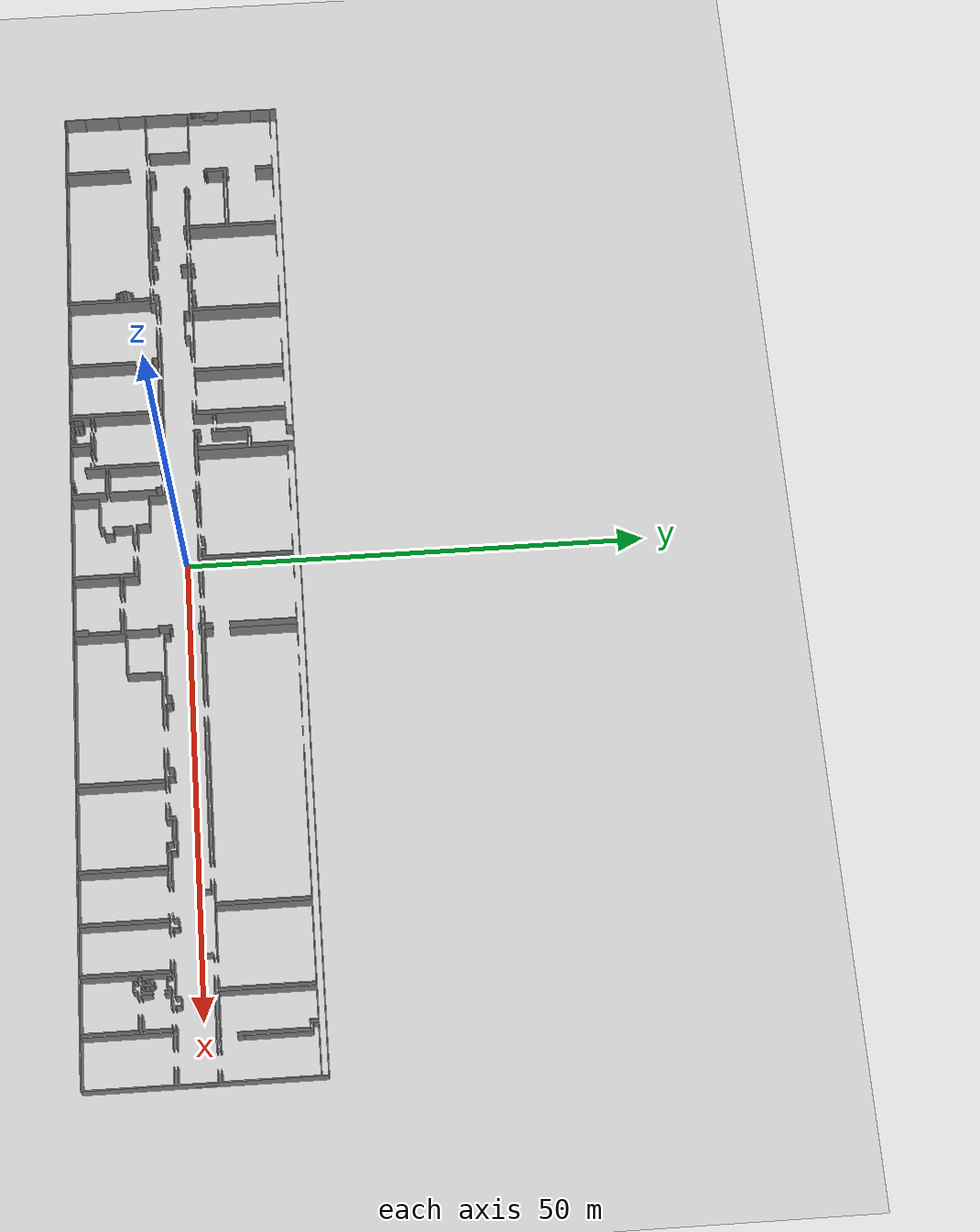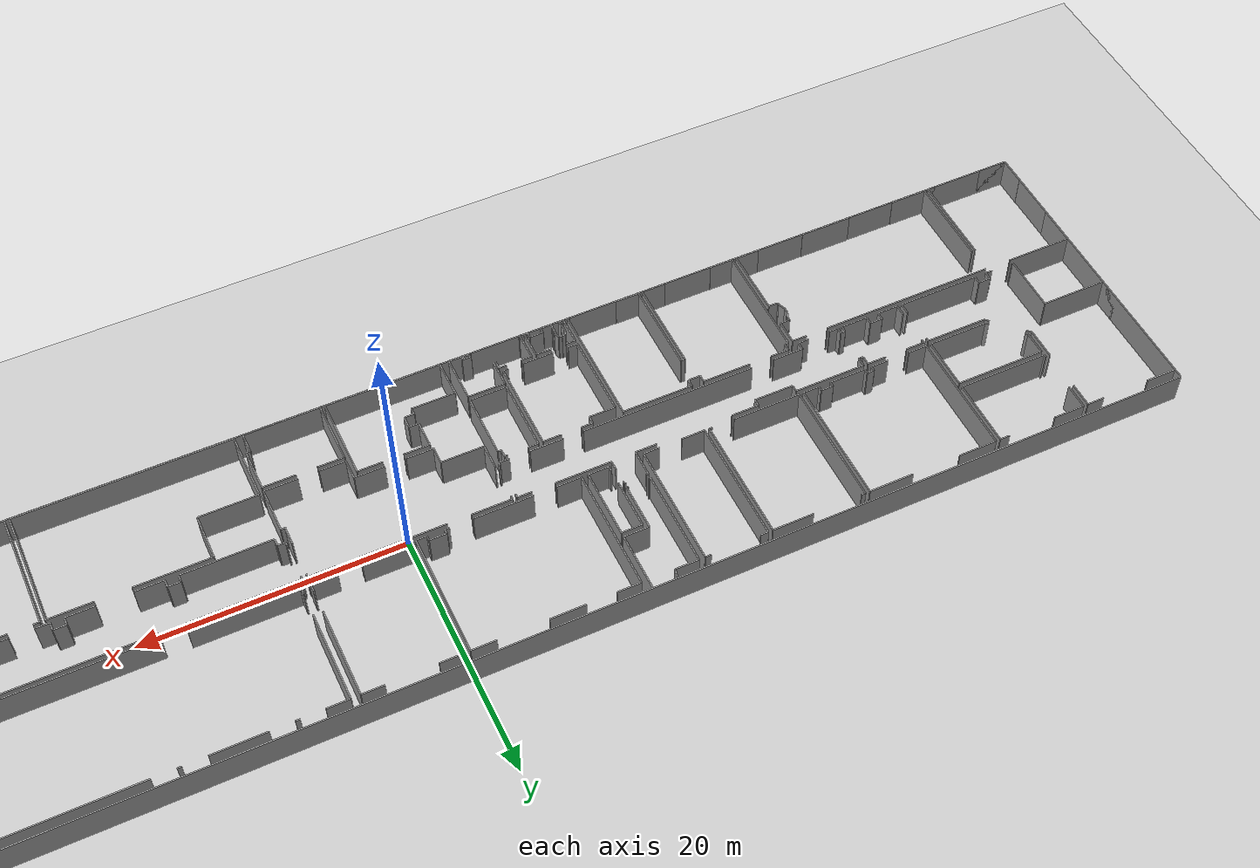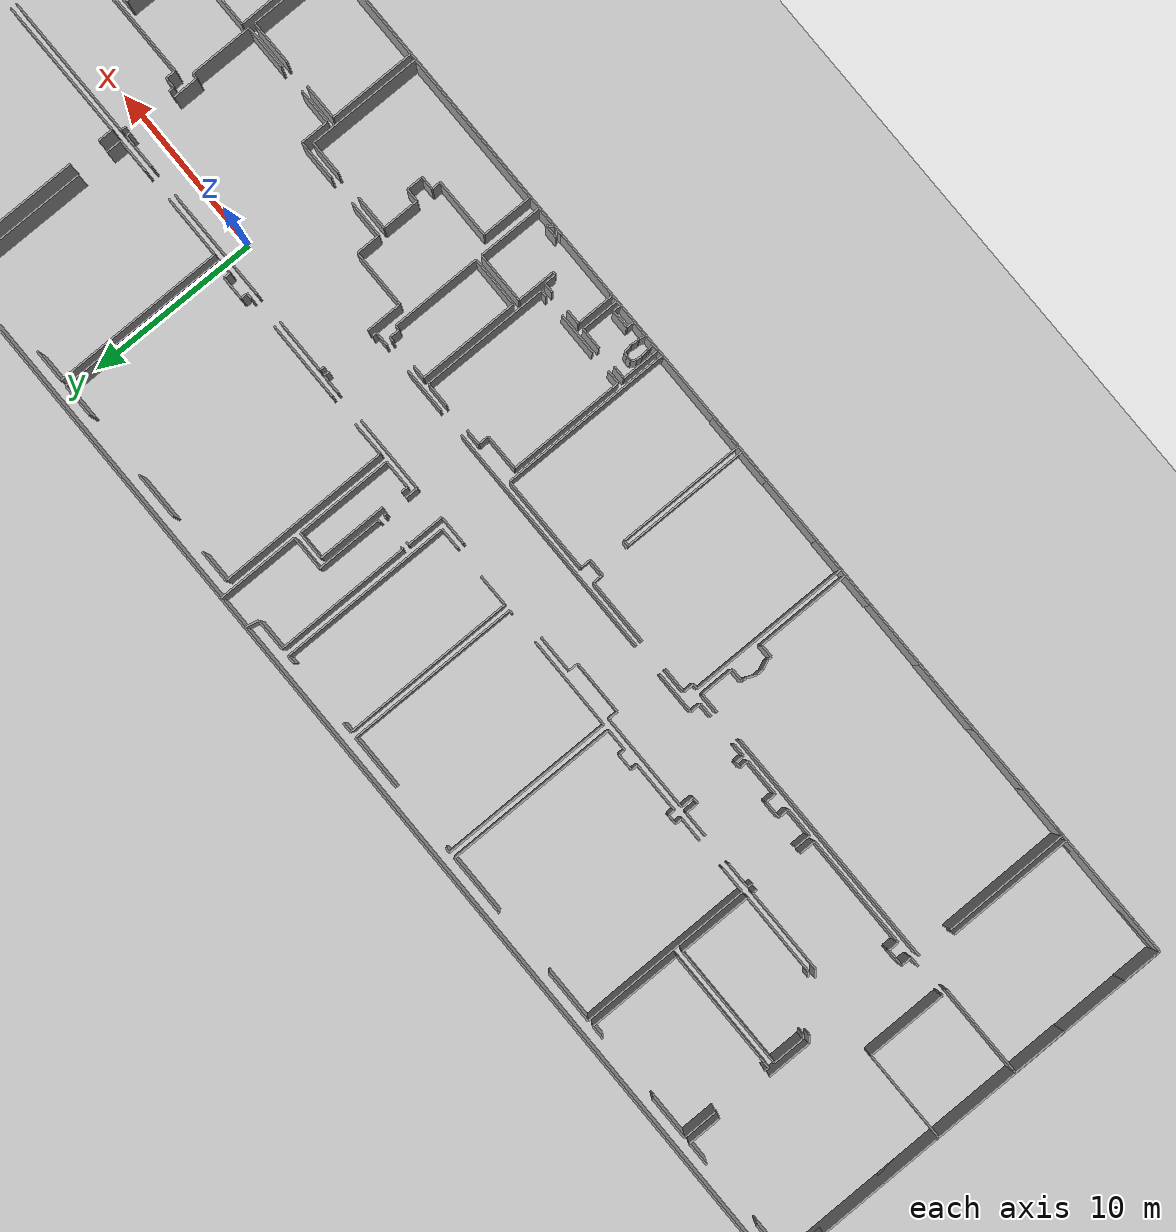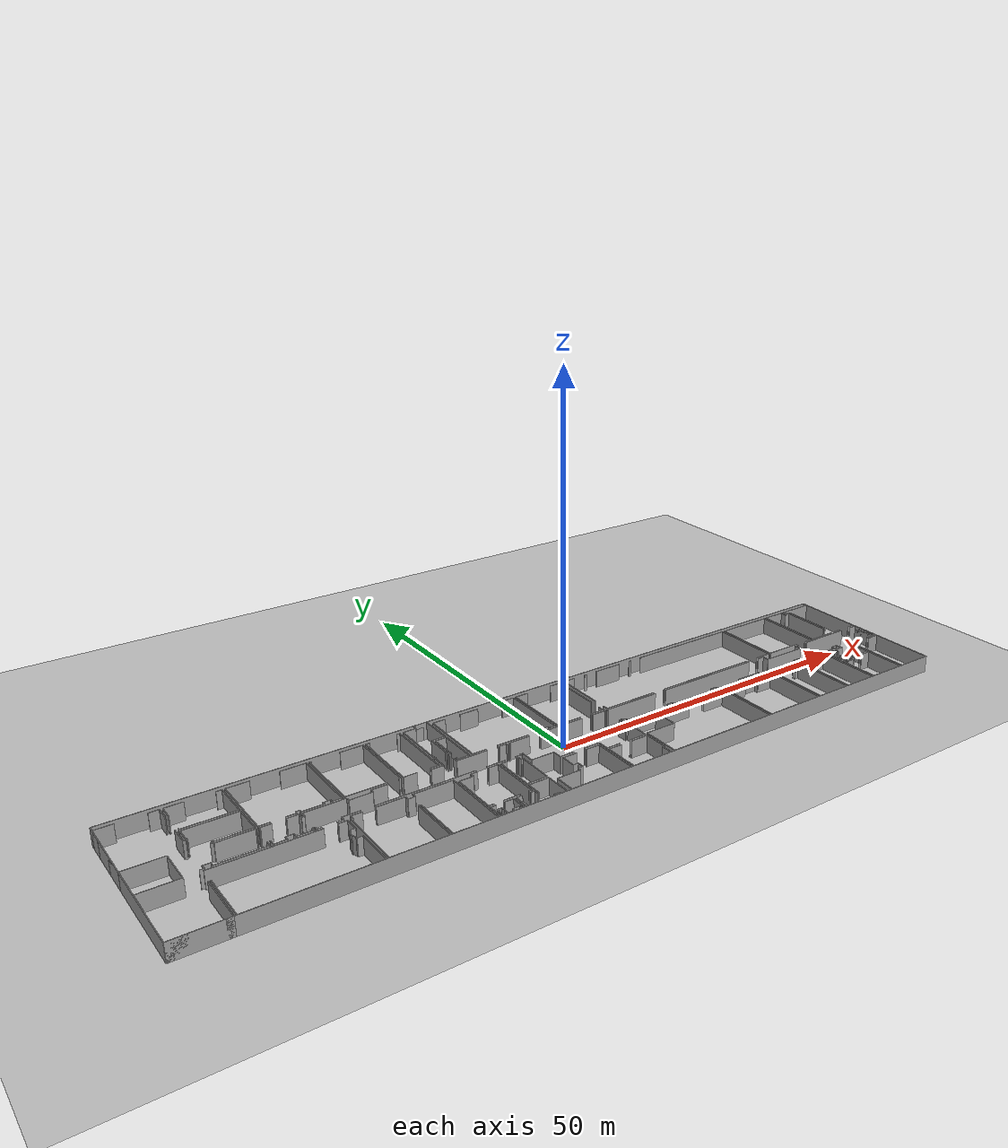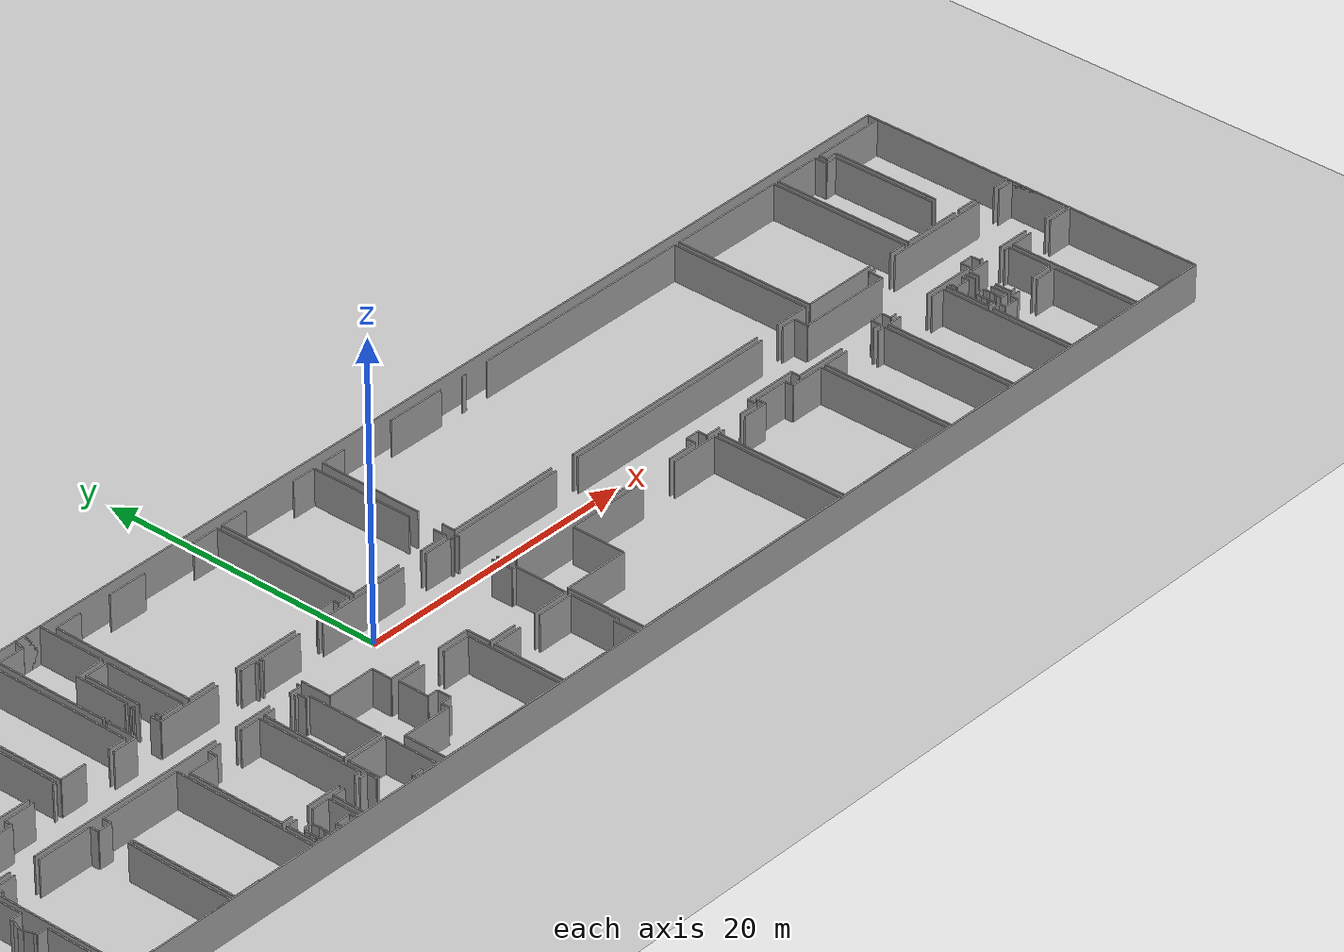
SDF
<sdf version="1.6">
  <world name="default">
    <light name="sun" type="directional">
      <cast_shadows>1</cast_shadows>
      <pose frame="">0 0 10 0 -0 0</pose>
      <diffuse>0.8 0.8 0.8 1</diffuse>
      <specular>0.1 0.1 0.1 1</specular>
      <attenuation>
        <range>1000</range>
        <constant>0.9</constant>
        <linear>0.01</linear>
        <quadratic>0.001</quadratic>
      </attenuation>
      <direction>-0.5 0.5 -1</direction>
    </light>
    <model name="ground_plane">
      <static>1</static>
      <link name="link">
        <collision name="collision">
          <geometry>
            <plane>
              <normal>0 0 1</normal>
              <size>100 100</size>
            </plane>
          </geometry>
          <surface>
            <friction>
              <ode>
                <mu>100</mu>
                <mu2>50</mu2>
              </ode>
              <torsional>
                <ode />
              </torsional>
            </friction>
            <contact>
              <ode />
            </contact>
            <bounce />
          </surface>
          <max_contacts>10</max_contacts>
        </collision>
        <visual name="visual">
          <cast_shadows>0</cast_shadows>
          <geometry>
            <plane>
              <normal>0 0 1</normal>
              <size>100 100</size>
            </plane>
          </geometry>
          <material>
            <script>
              <uri>file://media/materials/scripts/gazebo.material</uri>
              <name>Gazebo/Grey</name>
            </script>
          </material>
        </visual>
        <self_collide>0</self_collide>
        <kinematic>0</kinematic>
        <gravity>1</gravity>
      </link>
    </model>
    <gravity>0 0 -9.8</gravity>
    <magnetic_field>6e-06 2.3e-05 -4.2e-05</magnetic_field>
    <atmosphere type="adiabatic" />
    <physics default="0" name="default_physics" type="ode">
      <max_step_size>0.001</max_step_size>
      <real_time_factor>1</real_time_factor>
      <real_time_update_rate>1000</real_time_update_rate>
    </physics>
    <scene>
      <ambient>0.4 0.4 0.4 1</ambient>
      <background>0.7 0.7 0.7 1</background>
      <shadows>1</shadows>
    </scene>
    <spherical_coordinates>
      <surface_model>EARTH_WGS84</surface_model>
      <latitude_deg>0</latitude_deg>
      <longitude_deg>0</longitude_deg>
      <elevation>0</elevation>
      <heading_deg>0</heading_deg>
    </spherical_coordinates>
  <model name="0510034689_Layout1">
		<static>1</static>
		<link name="Wall_0">
			<collision name="Wall_0_Collision">
				<geometry>
					<box>
						<size>2.3799703281 0.1 2.5</size>
					</box>
				</geometry>
				<pose frame="">1.18998516405 0 1.25 0 0 0</pose>
			</collision>
			<visual name="Wall_0_Visual">
				<pose frame="">1.18998516405 0 1.25 0 0 0</pose>
				<geometry>
					<box>
						<size>2.3799703281 0.1 2.5</size>
					</box>
				</geometry>
				<material>
					<script>
						<uri>file://media/materials/scripts/gazebo.material</uri>
						<name>Gazebo/Grey</name>
					</script>
					<ambient>1 1 1 1</ambient>
				</material>
			</visual>
			<pose frame="">0.0145948161751 -24.6896063334 0 0 0 0.0</pose>
		</link>
		<link name="Wall_1">
			<collision name="Wall_1_Collision">
				<geometry>
					<box>
						<size>0.864520763347 0.1 2.5</size>
					</box>
				</geometry>
				<pose frame="">0.432260381673 0 1.25 0 0 0</pose>
			</collision>
			<visual name="Wall_1_Visual">
				<pose frame="">0.432260381673 0 1.25 0 0 0</pose>
				<geometry>
					<box>
						<size>0.864520763347 0.1 2.5</size>
					</box>
				</geometry>
				<material>
					<script>
						<uri>file://media/materials/scripts/gazebo.material</uri>
						<name>Gazebo/Grey</name>
					</script>
					<ambient>1 1 1 1</ambient>
				</material>
			</visual>
			<pose frame="">6.27551713241 -24.6896063334 0 0 0 0.0</pose>
		</link>
		<link name="Wall_2">
			<collision name="Wall_2_Collision">
				<geometry>
					<box>
						<size>7.27925975092 0.1 2.5</size>
					</box>
				</geometry>
				<pose frame="">3.63962987546 0 1.25 0 0 0</pose>
			</collision>
			<visual name="Wall_2_Visual">
				<pose frame="">3.63962987546 0 1.25 0 0 0</pose>
				<geometry>
					<box>
						<size>7.27925975092 0.1 2.5</size>
					</box>
				</geometry>
				<material>
					<script>
						<uri>file://media/materials/scripts/gazebo.material</uri>
						<name>Gazebo/Grey</name>
					</script>
					<ambient>1 1 1 1</ambient>
				</material>
			</visual>
			<pose frame="">7.14003789576 -24.6896063334 0 0 0 1.57079632679</pose>
		</link>
		<link name="Wall_3">
			<collision name="Wall_3_Collision">
				<geometry>
					<box>
						<size>5.24905736524 0.1 2.5</size>
					</box>
				</geometry>
				<pose frame="">2.62452868262 0 1.25 0 0 0</pose>
			</collision>
			<visual name="Wall_3_Visual">
				<pose frame="">2.62452868262 0 1.25 0 0 0</pose>
				<geometry>
					<box>
						<size>5.24905736524 0.1 2.5</size>
					</box>
				</geometry>
				<material>
					<script>
						<uri>file://media/materials/scripts/gazebo.material</uri>
						<name>Gazebo/Grey</name>
					</script>
					<ambient>1 1 1 1</ambient>
				</material>
			</visual>
			<pose frame="">5.26720570188 -15.3767175878 0 0 0 3.14159265359</pose>
		</link>
		<link name="Wall_4">
			<collision name="Wall_4_Collision">
				<geometry>
					<box>
						<size>3.13852003488 0.1 2.5</size>
					</box>
				</geometry>
				<pose frame="">1.56926001744 0 1.25 0 0 0</pose>
			</collision>
			<visual name="Wall_4_Visual">
				<pose frame="">1.56926001744 0 1.25 0 0 0</pose>
				<geometry>
					<box>
						<size>3.13852003488 0.1 2.5</size>
					</box>
				</geometry>
				<material>
					<script>
						<uri>file://media/materials/scripts/gazebo.material</uri>
						<name>Gazebo/Grey</name>
					</script>
					<ambient>1 1 1 1</ambient>
				</material>
			</visual>
			<pose frame="">0.0181483366352 -15.3767175878 0 0 0 -1.57079632679</pose>
		</link>
		<link name="Wall_5">
			<collision name="Wall_5_Collision">
				<geometry>
					<box>
						<size>2.27197146739 0.1 2.5</size>
					</box>
				</geometry>
				<pose frame="">1.13598573369 0 1.25 0 0 0</pose>
			</collision>
			<visual name="Wall_5_Visual">
				<pose frame="">1.13598573369 0 1.25 0 0 0</pose>
				<geometry>
					<box>
						<size>2.27197146739 0.1 2.5</size>
					</box>
				</geometry>
				<material>
					<script>
						<uri>file://media/materials/scripts/gazebo.material</uri>
						<name>Gazebo/Grey</name>
					</script>
					<ambient>1 1 1 1</ambient>
				</material>
			</visual>
			<pose frame="">0.0181483366352 -22.417637645 0 0 0 -1.57236039657</pose>
		</link>
		<link name="Wall_6">
			<collision name="Wall_6_Collision">
				<geometry>
					<box>
						<size>2.96807796424 0.1 2.5</size>
					</box>
				</geometry>
				<pose frame="">1.48403898212 0 1.25 0 0 0</pose>
			</collision>
			<visual name="Wall_6_Visual">
				<pose frame="">1.48403898212 0 1.25 0 0 0</pose>
				<geometry>
					<box>
						<size>2.96807796424 0.1 2.5</size>
					</box>
				</geometry>
				<material>
					<script>
						<uri>file://media/materials/scripts/gazebo.material</uri>
						<name>Gazebo/Grey</name>
					</script>
					<ambient>1 1 1 1</ambient>
				</material>
			</visual>
			<pose frame="">7.45224005046 -24.6649855131 0 0 0 0.0</pose>
		</link>
		<link name="Wall_7">
			<collision name="Wall_7_Collision">
				<geometry>
					<box>
						<size>4.15609600089 0.1 2.5</size>
					</box>
				</geometry>
				<pose frame="">2.07804800045 0 1.25 0 0 0</pose>
			</collision>
			<visual name="Wall_7_Visual">
				<pose frame="">2.07804800045 0 1.25 0 0 0</pose>
				<geometry>
					<box>
						<size>4.15609600089 0.1 2.5</size>
					</box>
				</geometry>
				<material>
					<script>
						<uri>file://media/materials/scripts/gazebo.material</uri>
						<name>Gazebo/Grey</name>
					</script>
					<ambient>1 1 1 1</ambient>
				</material>
			</visual>
			<pose frame="">14.2784259427 -24.6649855131 0 0 0 0.0</pose>
		</link>
		<link name="Wall_8">
			<collision name="Wall_8_Collision">
				<geometry>
					<box>
						<size>1.89593007687 0.1 2.5</size>
					</box>
				</geometry>
				<pose frame="">0.947965038435 0 1.25 0 0 0</pose>
			</collision>
			<visual name="Wall_8_Visual">
				<pose frame="">0.947965038435 0 1.25 0 0 0</pose>
				<geometry>
					<box>
						<size>1.89593007687 0.1 2.5</size>
					</box>
				</geometry>
				<material>
					<script>
						<uri>file://media/materials/scripts/gazebo.material</uri>
						<name>Gazebo/Grey</name>
					</script>
					<ambient>1 1 1 1</ambient>
				</material>
			</visual>
			<pose frame="">22.2949142777 -24.6649855131 0 0 0 0.0</pose>
		</link>
		<link name="Wall_9">
			<collision name="Wall_9_Collision">
				<geometry>
					<box>
						<size>5.42977926292 0.1 2.5</size>
					</box>
				</geometry>
				<pose frame="">2.71488963146 0 1.25 0 0 0</pose>
			</collision>
			<visual name="Wall_9_Visual">
				<pose frame="">2.71488963146 0 1.25 0 0 0</pose>
				<geometry>
					<box>
						<size>5.42977926292 0.1 2.5</size>
					</box>
				</geometry>
				<material>
					<script>
						<uri>file://media/materials/scripts/gazebo.material</uri>
						<name>Gazebo/Grey</name>
					</script>
					<ambient>1 1 1 1</ambient>
				</material>
			</visual>
			<pose frame="">24.1908443545 -24.6649855131 0 0 0 1.57079632679</pose>
		</link>
		<link name="Wall_10">
			<collision name="Wall_10_Collision">
				<geometry>
					<box>
						<size>0.755630743536 0.1 2.5</size>
					</box>
				</geometry>
				<pose frame="">0.377815371768 0 1.25 0 0 0</pose>
			</collision>
			<visual name="Wall_10_Visual">
				<pose frame="">0.377815371768 0 1.25 0 0 0</pose>
				<geometry>
					<box>
						<size>0.755630743536 0.1 2.5</size>
					</box>
				</geometry>
				<material>
					<script>
						<uri>file://media/materials/scripts/gazebo.material</uri>
						<name>Gazebo/Grey</name>
					</script>
					<ambient>1 1 1 1</ambient>
				</material>
			</visual>
			<pose frame="">24.1908443545 -19.2352062501 0 0 0 3.14159265359</pose>
		</link>
		<link name="Wall_11">
			<collision name="Wall_11_Collision">
				<geometry>
					<box>
						<size>0.221333560082 0.1 2.5</size>
					</box>
				</geometry>
				<pose frame="">0.110666780041 0 1.25 0 0 0</pose>
			</collision>
			<visual name="Wall_11_Visual">
				<pose frame="">0.110666780041 0 1.25 0 0 0</pose>
				<geometry>
					<box>
						<size>0.221333560082 0.1 2.5</size>
					</box>
				</geometry>
				<material>
					<script>
						<uri>file://media/materials/scripts/gazebo.material</uri>
						<name>Gazebo/Grey</name>
					</script>
					<ambient>1 1 1 1</ambient>
				</material>
			</visual>
			<pose frame="">23.435213611 -19.2352062501 0 0 0 1.57079632679</pose>
		</link>
		<link name="Wall_12">
			<collision name="Wall_12_Collision">
				<geometry>
					<box>
						<size>0.56188615846 0.1 2.5</size>
					</box>
				</geometry>
				<pose frame="">0.28094307923 0 1.25 0 0 0</pose>
			</collision>
			<visual name="Wall_12_Visual">
				<pose frame="">0.28094307923 0 1.25 0 0 0</pose>
				<geometry>
					<box>
						<size>0.56188615846 0.1 2.5</size>
					</box>
				</geometry>
				<material>
					<script>
						<uri>file://media/materials/scripts/gazebo.material</uri>
						<name>Gazebo/Grey</name>
					</script>
					<ambient>1 1 1 1</ambient>
				</material>
			</visual>
			<pose frame="">23.435213611 -19.0138726901 0 0 0 1.98331023317</pose>
		</link>
		<link name="Wall_13">
			<collision name="Wall_13_Collision">
				<geometry>
					<box>
						<size>0.396224868674 0.1 2.5</size>
					</box>
				</geometry>
				<pose frame="">0.198112434337 0 1.25 0 0 0</pose>
			</collision>
			<visual name="Wall_13_Visual">
				<pose frame="">0.198112434337 0 1.25 0 0 0</pose>
				<geometry>
					<box>
						<size>0.396224868674 0.1 2.5</size>
					</box>
				</geometry>
				<material>
					<script>
						<uri>file://media/materials/scripts/gazebo.material</uri>
						<name>Gazebo/Grey</name>
					</script>
					<ambient>1 1 1 1</ambient>
				</material>
			</visual>
			<pose frame="">23.2099457961 -18.4991198691 0 0 0 1.57688209407</pose>
		</link>
		<link name="Wall_14">
			<collision name="Wall_14_Collision">
				<geometry>
					<box>
						<size>0.553743081985 0.1 2.5</size>
					</box>
				</geometry>
				<pose frame="">0.276871540993 0 1.25 0 0 0</pose>
			</collision>
			<visual name="Wall_14_Visual">
				<pose frame="">0.276871540993 0 1.25 0 0 0</pose>
				<geometry>
					<box>
						<size>0.553743081985 0.1 2.5</size>
					</box>
				</geometry>
				<material>
					<script>
						<uri>file://media/materials/scripts/gazebo.material</uri>
						<name>Gazebo/Grey</name>
					</script>
					<ambient>1 1 1 1</ambient>
				</material>
			</visual>
			<pose frame="">23.2075344787 -18.1029023378 0 0 0 1.17032835829</pose>
		</link>
		<link name="Wall_15">
			<collision name="Wall_15_Collision">
				<geometry>
					<box>
						<size>0.246715849082 0.1 2.5</size>
					</box>
				</geometry>
				<pose frame="">0.123357924541 0 1.25 0 0 0</pose>
			</collision>
			<visual name="Wall_15_Visual">
				<pose frame="">0.123357924541 0 1.25 0 0 0</pose>
				<geometry>
					<box>
						<size>0.246715849082 0.1 2.5</size>
					</box>
				</geometry>
				<material>
					<script>
						<uri>file://media/materials/scripts/gazebo.material</uri>
						<name>Gazebo/Grey</name>
					</script>
					<ambient>1 1 1 1</ambient>
				</material>
			</visual>
			<pose frame="">23.4234108466 -17.5929721518 0 0 0 1.57079632679</pose>
		</link>
		<link name="Wall_16">
			<collision name="Wall_16_Collision">
				<geometry>
					<box>
						<size>0.766164393471 0.1 2.5</size>
					</box>
				</geometry>
				<pose frame="">0.383082196736 0 1.25 0 0 0</pose>
			</collision>
			<visual name="Wall_16_Visual">
				<pose frame="">0.383082196736 0 1.25 0 0 0</pose>
				<geometry>
					<box>
						<size>0.766164393471 0.1 2.5</size>
					</box>
				</geometry>
				<material>
					<script>
						<uri>file://media/materials/scripts/gazebo.material</uri>
						<name>Gazebo/Grey</name>
					</script>
					<ambient>1 1 1 1</ambient>
				</material>
			</visual>
			<pose frame="">23.4234108466 -17.3462563027 0 0 0 0.0</pose>
		</link>
		<link name="Wall_17">
			<collision name="Wall_17_Collision">
				<geometry>
					<box>
						<size>1.94580627476 0.1 2.5</size>
					</box>
				</geometry>
				<pose frame="">0.972903137378 0 1.25 0 0 0</pose>
			</collision>
			<visual name="Wall_17_Visual">
				<pose frame="">0.972903137378 0 1.25 0 0 0</pose>
				<geometry>
					<box>
						<size>1.94580627476 0.1 2.5</size>
					</box>
				</geometry>
				<material>
					<script>
						<uri>file://media/materials/scripts/gazebo.material</uri>
						<name>Gazebo/Grey</name>
					</script>
					<ambient>1 1 1 1</ambient>
				</material>
			</visual>
			<pose frame="">24.1895752401 -17.3462563027 0 0 0 1.57079632679</pose>
		</link>
		<link name="Wall_18">
			<collision name="Wall_18_Collision">
				<geometry>
					<box>
						<size>1.15311738928 0.1 2.5</size>
					</box>
				</geometry>
				<pose frame="">0.57655869464 0 1.25 0 0 0</pose>
			</collision>
			<visual name="Wall_18_Visual">
				<pose frame="">0.57655869464 0 1.25 0 0 0</pose>
				<geometry>
					<box>
						<size>1.15311738928 0.1 2.5</size>
					</box>
				</geometry>
				<material>
					<script>
						<uri>file://media/materials/scripts/gazebo.material</uri>
						<name>Gazebo/Grey</name>
					</script>
					<ambient>1 1 1 1</ambient>
				</material>
			</visual>
			<pose frame="">24.1895752401 -15.400450028 0 0 0 3.14159265359</pose>
		</link>
		<link name="Wall_19">
			<collision name="Wall_19_Collision">
				<geometry>
					<box>
						<size>13.8291594274 0.1 2.5</size>
					</box>
				</geometry>
				<pose frame="">6.91457971371 0 1.25 0 0 0</pose>
			</collision>
			<visual name="Wall_19_Visual">
				<pose frame="">6.91457971371 0 1.25 0 0 0</pose>
				<geometry>
					<box>
						<size>13.8291594274 0.1 2.5</size>
					</box>
				</geometry>
				<material>
					<script>
						<uri>file://media/materials/scripts/gazebo.material</uri>
						<name>Gazebo/Grey</name>
					</script>
					<ambient>1 1 1 1</ambient>
				</material>
			</visual>
			<pose frame="">21.2537327829 -15.400450028 0 0 0 3.14159265359</pose>
		</link>
		<link name="Wall_20">
			<collision name="Wall_20_Collision">
				<geometry>
					<box>
						<size>7.26598672262 0.1 2.5</size>
					</box>
				</geometry>
				<pose frame="">3.63299336131 0 1.25 0 0 0</pose>
			</collision>
			<visual name="Wall_20_Visual">
				<pose frame="">3.63299336131 0 1.25 0 0 0</pose>
				<geometry>
					<box>
						<size>7.26598672262 0.1 2.5</size>
					</box>
				</geometry>
				<material>
					<script>
						<uri>file://media/materials/scripts/gazebo.material</uri>
						<name>Gazebo/Grey</name>
					</script>
					<ambient>1 1 1 1</ambient>
				</material>
			</visual>
			<pose frame="">7.42457335545 -17.3990514639 0 0 0 -1.56698861796</pose>
		</link>
		<link name="Wall_21">
			<collision name="Wall_21_Collision">
				<geometry>
					<box>
						<size>3.52648832224 0.1 2.5</size>
					</box>
				</geometry>
				<pose frame="">1.76324416112 0 1.25 0 0 0</pose>
			</collision>
			<visual name="Wall_21_Visual">
				<pose frame="">1.76324416112 0 1.25 0 0 0</pose>
				<geometry>
					<box>
						<size>3.52648832224 0.1 2.5</size>
					</box>
				</geometry>
				<material>
					<script>
						<uri>file://media/materials/scripts/gazebo.material</uri>
						<name>Gazebo/Grey</name>
					</script>
					<ambient>1 1 1 1</ambient>
				</material>
			</visual>
			<pose frame="">0.0 -10.413845531 0 0 0 1.57079632679</pose>
		</link>
		<link name="Wall_22">
			<collision name="Wall_22_Collision">
				<geometry>
					<box>
						<size>2.25800842946 0.1 2.5</size>
					</box>
				</geometry>
				<pose frame="">1.12900421473 0 1.25 0 0 0</pose>
			</collision>
			<visual name="Wall_22_Visual">
				<pose frame="">1.12900421473 0 1.25 0 0 0</pose>
				<geometry>
					<box>
						<size>2.25800842946 0.1 2.5</size>
					</box>
				</geometry>
				<material>
					<script>
						<uri>file://media/materials/scripts/gazebo.material</uri>
						<name>Gazebo/Grey</name>
					</script>
					<ambient>1 1 1 1</ambient>
				</material>
			</visual>
			<pose frame="">0.0 -3.01148167843 0 0 0 1.57079632679</pose>
		</link>
		<link name="Wall_23">
			<collision name="Wall_23_Collision">
				<geometry>
					<box>
						<size>2.41398259536 0.1 2.5</size>
					</box>
				</geometry>
				<pose frame="">1.20699129768 0 1.25 0 0 0</pose>
			</collision>
			<visual name="Wall_23_Visual">
				<pose frame="">1.20699129768 0 1.25 0 0 0</pose>
				<geometry>
					<box>
						<size>2.41398259536 0.1 2.5</size>
					</box>
				</geometry>
				<material>
					<script>
						<uri>file://media/materials/scripts/gazebo.material</uri>
						<name>Gazebo/Grey</name>
					</script>
					<ambient>1 1 1 1</ambient>
				</material>
			</visual>
			<pose frame="">0.0 -0.753473248971 0 0 0 0.0</pose>
		</link>
		<link name="Wall_24">
			<collision name="Wall_24_Collision">
				<geometry>
					<box>
						<size>1.34983012903 0.1 2.5</size>
					</box>
				</geometry>
				<pose frame="">0.674915064515 0 1.25 0 0 0</pose>
			</collision>
			<visual name="Wall_24_Visual">
				<pose frame="">0.674915064515 0 1.25 0 0 0</pose>
				<geometry>
					<box>
						<size>1.34983012903 0.1 2.5</size>
					</box>
				</geometry>
				<material>
					<script>
						<uri>file://media/materials/scripts/gazebo.material</uri>
						<name>Gazebo/Grey</name>
					</script>
					<ambient>1 1 1 1</ambient>
				</material>
			</visual>
			<pose frame="">6.25229233798 -0.753473248971 0 0 0 0.0</pose>
		</link>
		<link name="Wall_25">
			<collision name="Wall_25_Collision">
				<geometry>
					<box>
						<size>1.94149128563 0.1 2.5</size>
					</box>
				</geometry>
				<pose frame="">0.970745642813 0 1.25 0 0 0</pose>
			</collision>
			<visual name="Wall_25_Visual">
				<pose frame="">0.970745642813 0 1.25 0 0 0</pose>
				<geometry>
					<box>
						<size>1.94149128563 0.1 2.5</size>
					</box>
				</geometry>
				<material>
					<script>
						<uri>file://media/materials/scripts/gazebo.material</uri>
						<name>Gazebo/Grey</name>
					</script>
					<ambient>1 1 1 1</ambient>
				</material>
			</visual>
			<pose frame="">7.60212246701 -0.753473248971 0 0 0 -1.57079632679</pose>
		</link>
		<link name="Wall_26">
			<collision name="Wall_26_Collision">
				<geometry>
					<box>
						<size>2.53822890002 0.1 2.5</size>
					</box>
				</geometry>
				<pose frame="">1.26911445001 0 1.25 0 0 0</pose>
			</collision>
			<visual name="Wall_26_Visual">
				<pose frame="">1.26911445001 0 1.25 0 0 0</pose>
				<geometry>
					<box>
						<size>2.53822890002 0.1 2.5</size>
					</box>
				</geometry>
				<material>
					<script>
						<uri>file://media/materials/scripts/gazebo.material</uri>
						<name>Gazebo/Grey</name>
					</script>
					<ambient>1 1 1 1</ambient>
				</material>
			</visual>
			<pose frame="">7.60212246701 -5.89224456851 0 0 0 -1.57079632679</pose>
		</link>
		<link name="Wall_27">
			<collision name="Wall_27_Collision">
				<geometry>
					<box>
						<size>0.430847309309 0.1 2.5</size>
					</box>
				</geometry>
				<pose frame="">0.215423654655 0 1.25 0 0 0</pose>
			</collision>
			<visual name="Wall_27_Visual">
				<pose frame="">0.215423654655 0 1.25 0 0 0</pose>
				<geometry>
					<box>
						<size>0.430847309309 0.1 2.5</size>
					</box>
				</geometry>
				<material>
					<script>
						<uri>file://media/materials/scripts/gazebo.material</uri>
						<name>Gazebo/Grey</name>
					</script>
					<ambient>1 1 1 1</ambient>
				</material>
			</visual>
			<pose frame="">7.60212246701 -8.43047346853 0 0 0 -0.780190961972</pose>
		</link>
		<link name="Wall_28">
			<collision name="Wall_28_Collision">
				<geometry>
					<box>
						<size>0.431828607498 0.1 2.5</size>
					</box>
				</geometry>
				<pose frame="">0.215914303749 0 1.25 0 0 0</pose>
			</collision>
			<visual name="Wall_28_Visual">
				<pose frame="">0.215914303749 0 1.25 0 0 0</pose>
				<geometry>
					<box>
						<size>0.431828607498 0.1 2.5</size>
					</box>
				</geometry>
				<material>
					<script>
						<uri>file://media/materials/scripts/gazebo.material</uri>
						<name>Gazebo/Grey</name>
					</script>
					<ambient>1 1 1 1</ambient>
				</material>
			</visual>
			<pose frame="">9.89553918962 -10.7301088519 0 0 0 -0.785398163397</pose>
		</link>
		<link name="Wall_29">
			<collision name="Wall_29_Collision">
				<geometry>
					<box>
						<size>4.85055542794 0.1 2.5</size>
					</box>
				</geometry>
				<pose frame="">2.42527771397 0 1.25 0 0 0</pose>
			</collision>
			<visual name="Wall_29_Visual">
				<pose frame="">2.42527771397 0 1.25 0 0 0</pose>
				<geometry>
					<box>
						<size>4.85055542794 0.1 2.5</size>
					</box>
				</geometry>
				<material>
					<script>
						<uri>file://media/materials/scripts/gazebo.material</uri>
						<name>Gazebo/Grey</name>
					</script>
					<ambient>1 1 1 1</ambient>
				</material>
			</visual>
			<pose frame="">10.2008881263 -11.0354577886 0 0 0 0.0</pose>
		</link>
		<link name="Wall_30">
			<collision name="Wall_30_Collision">
				<geometry>
					<box>
						<size>0.277555330217 0.1 2.5</size>
					</box>
				</geometry>
				<pose frame="">0.138777665109 0 1.25 0 0 0</pose>
			</collision>
			<visual name="Wall_30_Visual">
				<pose frame="">0.138777665109 0 1.25 0 0 0</pose>
				<geometry>
					<box>
						<size>0.277555330217 0.1 2.5</size>
					</box>
				</geometry>
				<material>
					<script>
						<uri>file://media/materials/scripts/gazebo.material</uri>
						<name>Gazebo/Grey</name>
					</script>
					<ambient>1 1 1 1</ambient>
				</material>
			</visual>
			<pose frame="">15.0514435542 -11.0354577886 0 0 0 -1.57079632679</pose>
		</link>
		<link name="Wall_31">
			<collision name="Wall_31_Collision">
				<geometry>
					<box>
						<size>0.915412252792 0.1 2.5</size>
					</box>
				</geometry>
				<pose frame="">0.457706126396 0 1.25 0 0 0</pose>
			</collision>
			<visual name="Wall_31_Visual">
				<pose frame="">0.457706126396 0 1.25 0 0 0</pose>
				<geometry>
					<box>
						<size>0.915412252792 0.1 2.5</size>
					</box>
				</geometry>
				<material>
					<script>
						<uri>file://media/materials/scripts/gazebo.material</uri>
						<name>Gazebo/Grey</name>
					</script>
					<ambient>1 1 1 1</ambient>
				</material>
			</visual>
			<pose frame="">15.0514435542 -14.1134410642 0 0 0 -1.57079632679</pose>
		</link>
		<link name="Wall_32">
			<collision name="Wall_32_Collision">
				<geometry>
					<box>
						<size>6.45674667587 0.1 2.5</size>
					</box>
				</geometry>
				<pose frame="">3.22837333794 0 1.25 0 0 0</pose>
			</collision>
			<visual name="Wall_32_Visual">
				<pose frame="">3.22837333794 0 1.25 0 0 0</pose>
				<geometry>
					<box>
						<size>6.45674667587 0.1 2.5</size>
					</box>
				</geometry>
				<material>
					<script>
						<uri>file://media/materials/scripts/gazebo.material</uri>
						<name>Gazebo/Grey</name>
					</script>
					<ambient>1 1 1 1</ambient>
				</material>
			</visual>
			<pose frame="">15.0514435542 -15.028853317 0 0 0 3.14159265359</pose>
		</link>
		<link name="Wall_33">
			<collision name="Wall_33_Collision">
				<geometry>
					<box>
						<size>0.605875238435 0.1 2.5</size>
					</box>
				</geometry>
				<pose frame="">0.302937619217 0 1.25 0 0 0</pose>
			</collision>
			<visual name="Wall_33_Visual">
				<pose frame="">0.302937619217 0 1.25 0 0 0</pose>
				<geometry>
					<box>
						<size>0.605875238435 0.1 2.5</size>
					</box>
				</geometry>
				<material>
					<script>
						<uri>file://media/materials/scripts/gazebo.material</uri>
						<name>Gazebo/Grey</name>
					</script>
					<ambient>1 1 1 1</ambient>
				</material>
			</visual>
			<pose frame="">8.59469687836 -15.028853317 0 0 0 1.57079632679</pose>
		</link>
		<link name="Wall_34">
			<collision name="Wall_34_Collision">
				<geometry>
					<box>
						<size>0.970872554258 0.1 2.5</size>
					</box>
				</geometry>
				<pose frame="">0.485436277129 0 1.25 0 0 0</pose>
			</collision>
			<visual name="Wall_34_Visual">
				<pose frame="">0.485436277129 0 1.25 0 0 0</pose>
				<geometry>
					<box>
						<size>0.970872554258 0.1 2.5</size>
					</box>
				</geometry>
				<material>
					<script>
						<uri>file://media/materials/scripts/gazebo.material</uri>
						<name>Gazebo/Grey</name>
					</script>
					<ambient>1 1 1 1</ambient>
				</material>
			</visual>
			<pose frame="">8.59469687836 -14.4229780786 0 0 0 3.14159265359</pose>
		</link>
		<link name="Wall_35">
			<collision name="Wall_35_Collision">
				<geometry>
					<box>
						<size>0.60574832699 0.1 2.5</size>
					</box>
				</geometry>
				<pose frame="">0.302874163495 0 1.25 0 0 0</pose>
			</collision>
			<visual name="Wall_35_Visual">
				<pose frame="">0.302874163495 0 1.25 0 0 0</pose>
				<geometry>
					<box>
						<size>0.60574832699 0.1 2.5</size>
					</box>
				</geometry>
				<material>
					<script>
						<uri>file://media/materials/scripts/gazebo.material</uri>
						<name>Gazebo/Grey</name>
					</script>
					<ambient>1 1 1 1</ambient>
				</material>
			</visual>
			<pose frame="">7.6238243241 -14.4229780786 0 0 0 -1.57079632679</pose>
		</link>
		<link name="Wall_36">
			<collision name="Wall_36_Collision">
				<geometry>
					<box>
						<size>0.547622885179 0.1 2.5</size>
					</box>
				</geometry>
				<pose frame="">0.27381144259 0 1.25 0 0 0</pose>
			</collision>
			<visual name="Wall_36_Visual">
				<pose frame="">0.27381144259 0 1.25 0 0 0</pose>
				<geometry>
					<box>
						<size>0.547622885179 0.1 2.5</size>
					</box>
				</geometry>
				<material>
					<script>
						<uri>file://media/materials/scripts/gazebo.material</uri>
						<name>Gazebo/Grey</name>
					</script>
					<ambient>1 1 1 1</ambient>
				</material>
			</visual>
			<pose frame="">7.6238243241 -15.0287264056 0 0 0 3.14159265359</pose>
		</link>
		<link name="Wall_37">
			<collision name="Wall_37_Collision">
				<geometry>
					<box>
						<size>0.0859190482657 0.1 2.5</size>
					</box>
				</geometry>
				<pose frame="">0.0429595241328 0 1.25 0 0 0</pose>
			</collision>
			<visual name="Wall_37_Visual">
				<pose frame="">0.0429595241328 0 1.25 0 0 0</pose>
				<geometry>
					<box>
						<size>0.0859190482657 0.1 2.5</size>
					</box>
				</geometry>
				<material>
					<script>
						<uri>file://media/materials/scripts/gazebo.material</uri>
						<name>Gazebo/Grey</name>
					</script>
					<ambient>1 1 1 1</ambient>
				</material>
			</visual>
			<pose frame="">5.29144578787 -15.0287264056 0 0 0 3.14159265359</pose>
		</link>
		<link name="Wall_38">
			<collision name="Wall_38_Collision">
				<geometry>
					<box>
						<size>4.61208882278 0.1 2.5</size>
					</box>
				</geometry>
				<pose frame="">2.30604441139 0 1.25 0 0 0</pose>
			</collision>
			<visual name="Wall_38_Visual">
				<pose frame="">2.30604441139 0 1.25 0 0 0</pose>
				<geometry>
					<box>
						<size>4.61208882278 0.1 2.5</size>
					</box>
				</geometry>
				<material>
					<script>
						<uri>file://media/materials/scripts/gazebo.material</uri>
						<name>Gazebo/Grey</name>
					</script>
					<ambient>1 1 1 1</ambient>
				</material>
			</visual>
			<pose frame="">5.20552673961 -15.0287264056 0 0 0 1.57079632679</pose>
		</link>
		<link name="Wall_39">
			<collision name="Wall_39_Collision">
				<geometry>
					<box>
						<size>5.20552748838 0.1 2.5</size>
					</box>
				</geometry>
				<pose frame="">2.60276374419 0 1.25 0 0 0</pose>
			</collision>
			<visual name="Wall_39_Visual">
				<pose frame="">2.60276374419 0 1.25 0 0 0</pose>
				<geometry>
					<box>
						<size>5.20552748838 0.1 2.5</size>
					</box>
				</geometry>
				<material>
					<script>
						<uri>file://media/materials/scripts/gazebo.material</uri>
						<name>Gazebo/Grey</name>
					</script>
					<ambient>1 1 1 1</ambient>
				</material>
			</visual>
			<pose frame="">5.20552673961 -10.4166375828 0 0 0 3.14105629067</pose>
		</link>
		<link name="Wall_40">
			<collision name="Wall_40_Collision">
				<geometry>
					<box>
						<size>7.09346139544 0.1 2.5</size>
					</box>
				</geometry>
				<pose frame="">3.54673069772 0 1.25 0 0 0</pose>
			</collision>
			<visual name="Wall_40_Visual">
				<pose frame="">3.54673069772 0 1.25 0 0 0</pose>
				<geometry>
					<box>
						<size>7.09346139544 0.1 2.5</size>
					</box>
				</geometry>
				<material>
					<script>
						<uri>file://media/materials/scripts/gazebo.material</uri>
						<name>Gazebo/Grey</name>
					</script>
					<ambient>1 1 1 1</ambient>
				</material>
			</visual>
			<pose frame="">7.9588705389 -6.13604145435 0 0 0 0.0</pose>
		</link>
		<link name="Wall_41">
			<collision name="Wall_41_Collision">
				<geometry>
					<box>
						<size>5.38218747105 0.1 2.5</size>
					</box>
				</geometry>
				<pose frame="">2.69109373552 0 1.25 0 0 0</pose>
			</collision>
			<visual name="Wall_41_Visual">
				<pose frame="">2.69109373552 0 1.25 0 0 0</pose>
				<geometry>
					<box>
						<size>5.38218747105 0.1 2.5</size>
					</box>
				</geometry>
				<material>
					<script>
						<uri>file://media/materials/scripts/gazebo.material</uri>
						<name>Gazebo/Grey</name>
					</script>
					<ambient>1 1 1 1</ambient>
				</material>
			</visual>
			<pose frame="">15.0523319343 -6.13604145435 0 0 0 1.57079632679</pose>
		</link>
		<link name="Wall_42">
			<collision name="Wall_42_Collision">
				<geometry>
					<box>
						<size>0.780759209646 0.1 2.5</size>
					</box>
				</geometry>
				<pose frame="">0.390379604823 0 1.25 0 0 0</pose>
			</collision>
			<visual name="Wall_42_Visual">
				<pose frame="">0.390379604823 0 1.25 0 0 0</pose>
				<geometry>
					<box>
						<size>0.780759209646 0.1 2.5</size>
					</box>
				</geometry>
				<material>
					<script>
						<uri>file://media/materials/scripts/gazebo.material</uri>
						<name>Gazebo/Grey</name>
					</script>
					<ambient>1 1 1 1</ambient>
				</material>
			</visual>
			<pose frame="">15.0523319343 -0.753853983306 0 0 0 3.14159265359</pose>
		</link>
		<link name="Wall_43">
			<collision name="Wall_43_Collision">
				<geometry>
					<box>
						<size>2.46779304804 0.1 2.5</size>
					</box>
				</geometry>
				<pose frame="">1.23389652402 0 1.25 0 0 0</pose>
			</collision>
			<visual name="Wall_43_Visual">
				<pose frame="">1.23389652402 0 1.25 0 0 0</pose>
				<geometry>
					<box>
						<size>2.46779304804 0.1 2.5</size>
					</box>
				</geometry>
				<material>
					<script>
						<uri>file://media/materials/scripts/gazebo.material</uri>
						<name>Gazebo/Grey</name>
					</script>
					<ambient>1 1 1 1</ambient>
				</material>
			</visual>
			<pose frame="">10.4411314917 -0.753853983306 0 0 0 3.14159265359</pose>
		</link>
		<link name="Wall_44">
			<collision name="Wall_44_Collision">
				<geometry>
					<box>
						<size>1.97563046433 0.1 2.5</size>
					</box>
				</geometry>
				<pose frame="">0.987815232165 0 1.25 0 0 0</pose>
			</collision>
			<visual name="Wall_44_Visual">
				<pose frame="">0.987815232165 0 1.25 0 0 0</pose>
				<geometry>
					<box>
						<size>1.97563046433 0.1 2.5</size>
					</box>
				</geometry>
				<material>
					<script>
						<uri>file://media/materials/scripts/gazebo.material</uri>
						<name>Gazebo/Grey</name>
					</script>
					<ambient>1 1 1 1</ambient>
				</material>
			</visual>
			<pose frame="">7.97333844363 -0.753853983306 0 0 0 -1.57079632679</pose>
		</link>
		<link name="Wall_45">
			<collision name="Wall_45_Collision">
				<geometry>
					<box>
						<size>0.250560510875 0.1 2.5</size>
					</box>
				</geometry>
				<pose frame="">0.125280255438 0 1.25 0 0 0</pose>
			</collision>
			<visual name="Wall_45_Visual">
				<pose frame="">0.125280255438 0 1.25 0 0 0</pose>
				<geometry>
					<box>
						<size>0.250560510875 0.1 2.5</size>
					</box>
				</geometry>
				<material>
					<script>
						<uri>file://media/materials/scripts/gazebo.material</uri>
						<name>Gazebo/Grey</name>
					</script>
					<ambient>1 1 1 1</ambient>
				</material>
			</visual>
			<pose frame="">7.97333844363 -5.88589899626 0 0 0 -1.62857062042</pose>
		</link>
		<link name="Wall_46">
			<collision name="Wall_46_Collision">
				<geometry>
					<box>
						<size>4.72605530039 0.1 2.5</size>
					</box>
				</geometry>
				<pose frame="">2.3630276502 0 1.25 0 0 0</pose>
			</collision>
			<visual name="Wall_46_Visual">
				<pose frame="">2.3630276502 0 1.25 0 0 0</pose>
				<geometry>
					<box>
						<size>4.72605530039 0.1 2.5</size>
					</box>
				</geometry>
				<material>
					<script>
						<uri>file://media/materials/scripts/gazebo.material</uri>
						<name>Gazebo/Grey</name>
					</script>
					<ambient>1 1 1 1</ambient>
				</material>
			</visual>
			<pose frame="">10.3303378002 -10.6905124811 0 0 0 0.0</pose>
		</link>
		<link name="Wall_47">
			<collision name="Wall_47_Collision">
				<geometry>
					<box>
						<size>4.18338196157 0.1 2.5</size>
					</box>
				</geometry>
				<pose frame="">2.09169098078 0 1.25 0 0 0</pose>
			</collision>
			<visual name="Wall_47_Visual">
				<pose frame="">2.09169098078 0 1.25 0 0 0</pose>
				<geometry>
					<box>
						<size>4.18338196157 0.1 2.5</size>
					</box>
				</geometry>
				<material>
					<script>
						<uri>file://media/materials/scripts/gazebo.material</uri>
						<name>Gazebo/Grey</name>
					</script>
					<ambient>1 1 1 1</ambient>
				</material>
			</visual>
			<pose frame="">15.0563931006 -10.6905124811 0 0 0 1.57079632679</pose>
		</link>
		<link name="Wall_48">
			<collision name="Wall_48_Collision">
				<geometry>
					<box>
						<size>7.08584670874 0.1 2.5</size>
					</box>
				</geometry>
				<pose frame="">3.54292335437 0 1.25 0 0 0</pose>
			</collision>
			<visual name="Wall_48_Visual">
				<pose frame="">3.54292335437 0 1.25 0 0 0</pose>
				<geometry>
					<box>
						<size>7.08584670874 0.1 2.5</size>
					</box>
				</geometry>
				<material>
					<script>
						<uri>file://media/materials/scripts/gazebo.material</uri>
						<name>Gazebo/Grey</name>
					</script>
					<ambient>1 1 1 1</ambient>
				</material>
			</visual>
			<pose frame="">15.0563931006 -6.50713051954 0 0 0 3.14159265359</pose>
		</link>
		<link name="Wall_49">
			<collision name="Wall_49_Collision">
				<geometry>
					<box>
						<size>1.82980921402 0.1 2.5</size>
					</box>
				</geometry>
				<pose frame="">0.914904607012 0 1.25 0 0 0</pose>
			</collision>
			<visual name="Wall_49_Visual">
				<pose frame="">0.914904607012 0 1.25 0 0 0</pose>
				<geometry>
					<box>
						<size>1.82980921402 0.1 2.5</size>
					</box>
				</geometry>
				<material>
					<script>
						<uri>file://media/materials/scripts/gazebo.material</uri>
						<name>Gazebo/Grey</name>
					</script>
					<ambient>1 1 1 1</ambient>
				</material>
			</visual>
			<pose frame="">7.97054639184 -6.50713051954 0 0 0 -1.57079632679</pose>
		</link>
		<link name="Wall_50">
			<collision name="Wall_50_Collision">
				<geometry>
					<box>
						<size>0.250670922915 0.1 2.5</size>
					</box>
				</geometry>
				<pose frame="">0.125335461458 0 1.25 0 0 0</pose>
			</collision>
			<visual name="Wall_50_Visual">
				<pose frame="">0.125335461458 0 1.25 0 0 0</pose>
				<geometry>
					<box>
						<size>0.250670922915 0.1 2.5</size>
					</box>
				</geometry>
				<material>
					<script>
						<uri>file://media/materials/scripts/gazebo.material</uri>
						<name>Gazebo/Grey</name>
					</script>
					<ambient>1 1 1 1</ambient>
				</material>
			</visual>
			<pose frame="">7.97054639184 -8.33693973356 0 0 0 -0.840916526856</pose>
		</link>
		<link name="Wall_51">
			<collision name="Wall_51_Collision">
				<geometry>
					<box>
						<size>0.294695398516 0.1 2.5</size>
					</box>
				</geometry>
				<pose frame="">0.147347699258 0 1.25 0 0 0</pose>
			</collision>
			<visual name="Wall_51_Visual">
				<pose frame="">0.147347699258 0 1.25 0 0 0</pose>
				<geometry>
					<box>
						<size>0.294695398516 0.1 2.5</size>
					</box>
				</geometry>
				<material>
					<script>
						<uri>file://media/materials/scripts/gazebo.material</uri>
						<name>Gazebo/Grey</name>
					</script>
					<ambient>1 1 1 1</ambient>
				</material>
			</visual>
			<pose frame="">10.1109079118 -10.4937997414 0 0 0 -0.730862479428</pose>
		</link>
		<link name="Wall_52">
			<collision name="Wall_52_Collision">
				<geometry>
					<box>
						<size>3.03013766084 0.1 2.5</size>
					</box>
				</geometry>
				<pose frame="">1.51506883042 0 1.25 0 0 0</pose>
			</collision>
			<visual name="Wall_52_Visual">
				<pose frame="">1.51506883042 0 1.25 0 0 0</pose>
				<geometry>
					<box>
						<size>3.03013766084 0.1 2.5</size>
					</box>
				</geometry>
				<material>
					<script>
						<uri>file://media/materials/scripts/gazebo.material</uri>
						<name>Gazebo/Grey</name>
					</script>
					<ambient>1 1 1 1</ambient>
				</material>
			</visual>
			<pose frame="">15.415298667 -0.748650614061 0 0 0 0.0</pose>
		</link>
		<link name="Wall_53">
			<collision name="Wall_53_Collision">
				<geometry>
					<box>
						<size>3.50148676758 0.1 2.5</size>
					</box>
				</geometry>
				<pose frame="">1.75074338379 0 1.25 0 0 0</pose>
			</collision>
			<visual name="Wall_53_Visual">
				<pose frame="">1.75074338379 0 1.25 0 0 0</pose>
				<geometry>
					<box>
						<size>3.50148676758 0.1 2.5</size>
					</box>
				</geometry>
				<material>
					<script>
						<uri>file://media/materials/scripts/gazebo.material</uri>
						<name>Gazebo/Grey</name>
					</script>
					<ambient>1 1 1 1</ambient>
				</material>
			</visual>
			<pose frame="">22.2826038675 -0.748650614061 0 0 0 0.0</pose>
		</link>
		<link name="Wall_54">
			<collision name="Wall_54_Collision">
				<geometry>
					<box>
						<size>9.92942454543 0.1 2.5</size>
					</box>
				</geometry>
				<pose frame="">4.96471227272 0 1.25 0 0 0</pose>
			</collision>
			<visual name="Wall_54_Visual">
				<pose frame="">4.96471227272 0 1.25 0 0 0</pose>
				<geometry>
					<box>
						<size>9.92942454543 0.1 2.5</size>
					</box>
				</geometry>
				<material>
					<script>
						<uri>file://media/materials/scripts/gazebo.material</uri>
						<name>Gazebo/Grey</name>
					</script>
					<ambient>1 1 1 1</ambient>
				</material>
			</visual>
			<pose frame="">25.7840906351 -0.748650614061 0 0 0 -1.57079632679</pose>
		</link>
		<link name="Wall_55">
			<collision name="Wall_55_Collision">
				<geometry>
					<box>
						<size>1.26632239822 0.1 2.5</size>
					</box>
				</geometry>
				<pose frame="">0.63316119911 0 1.25 0 0 0</pose>
			</collision>
			<visual name="Wall_55_Visual">
				<pose frame="">0.63316119911 0 1.25 0 0 0</pose>
				<geometry>
					<box>
						<size>1.26632239822 0.1 2.5</size>
					</box>
				</geometry>
				<material>
					<script>
						<uri>file://media/materials/scripts/gazebo.material</uri>
						<name>Gazebo/Grey</name>
					</script>
					<ambient>1 1 1 1</ambient>
				</material>
			</visual>
			<pose frame="">25.7840906351 -10.6780751595 0 0 0 3.14159265359</pose>
		</link>
		<link name="Wall_56">
			<collision name="Wall_56_Collision">
				<geometry>
					<box>
						<size>0.382384183788 0.1 2.5</size>
					</box>
				</geometry>
				<pose frame="">0.191192091894 0 1.25 0 0 0</pose>
			</collision>
			<visual name="Wall_56_Visual">
				<pose frame="">0.191192091894 0 1.25 0 0 0</pose>
				<geometry>
					<box>
						<size>0.382384183788 0.1 2.5</size>
					</box>
				</geometry>
				<material>
					<script>
						<uri>file://media/materials/scripts/gazebo.material</uri>
						<name>Gazebo/Grey</name>
					</script>
					<ambient>1 1 1 1</ambient>
				</material>
			</visual>
			<pose frame="">24.5177682369 -10.6780751595 0 0 0 1.57079632679</pose>
		</link>
		<link name="Wall_57">
			<collision name="Wall_57_Collision">
				<geometry>
					<box>
						<size>0.970364908478 0.1 2.5</size>
					</box>
				</geometry>
				<pose frame="">0.485182454239 0 1.25 0 0 0</pose>
			</collision>
			<visual name="Wall_57_Visual">
				<pose frame="">0.485182454239 0 1.25 0 0 0</pose>
				<geometry>
					<box>
						<size>0.970364908478 0.1 2.5</size>
					</box>
				</geometry>
				<material>
					<script>
						<uri>file://media/materials/scripts/gazebo.material</uri>
						<name>Gazebo/Grey</name>
					</script>
					<ambient>1 1 1 1</ambient>
				</material>
			</visual>
			<pose frame="">24.5177682369 -10.2956909757 0 0 0 3.14159265359</pose>
		</link>
		<link name="Wall_58">
			<collision name="Wall_58_Collision">
				<geometry>
					<box>
						<size>0.378830663328 0.1 2.5</size>
					</box>
				</geometry>
				<pose frame="">0.189415331664 0 1.25 0 0 0</pose>
			</collision>
			<visual name="Wall_58_Visual">
				<pose frame="">0.189415331664 0 1.25 0 0 0</pose>
				<geometry>
					<box>
						<size>0.378830663328 0.1 2.5</size>
					</box>
				</geometry>
				<material>
					<script>
						<uri>file://media/materials/scripts/gazebo.material</uri>
						<name>Gazebo/Grey</name>
					</script>
					<ambient>1 1 1 1</ambient>
				</material>
			</visual>
			<pose frame="">23.5474033284 -10.2956909757 0 0 0 -1.57079632679</pose>
		</link>
		<link name="Wall_59">
			<collision name="Wall_59_Collision">
				<geometry>
					<box>
						<size>2.88253965031 0.1 2.5</size>
					</box>
				</geometry>
				<pose frame="">1.44126982515 0 1.25 0 0 0</pose>
			</collision>
			<visual name="Wall_59_Visual">
				<pose frame="">1.44126982515 0 1.25 0 0 0</pose>
				<geometry>
					<box>
						<size>2.88253965031 0.1 2.5</size>
					</box>
				</geometry>
				<material>
					<script>
						<uri>file://media/materials/scripts/gazebo.material</uri>
						<name>Gazebo/Grey</name>
					</script>
					<ambient>1 1 1 1</ambient>
				</material>
			</visual>
			<pose frame="">23.5474033284 -10.674521639 0 0 0 3.14159265359</pose>
		</link>
		<link name="Wall_60">
			<collision name="Wall_60_Collision">
				<geometry>
					<box>
						<size>0.389618136153 0.1 2.5</size>
					</box>
				</geometry>
				<pose frame="">0.194809068077 0 1.25 0 0 0</pose>
			</collision>
			<visual name="Wall_60_Visual">
				<pose frame="">0.194809068077 0 1.25 0 0 0</pose>
				<geometry>
					<box>
						<size>0.389618136153 0.1 2.5</size>
					</box>
				</geometry>
				<material>
					<script>
						<uri>file://media/materials/scripts/gazebo.material</uri>
						<name>Gazebo/Grey</name>
					</script>
					<ambient>1 1 1 1</ambient>
				</material>
			</visual>
			<pose frame="">20.6648636781 -10.674521639 0 0 0 1.57079632679</pose>
		</link>
		<link name="Wall_61">
			<collision name="Wall_61_Collision">
				<geometry>
					<box>
						<size>0.559171826675 0.1 2.5</size>
					</box>
				</geometry>
				<pose frame="">0.279585913337 0 1.25 0 0 0</pose>
			</collision>
			<visual name="Wall_61_Visual">
				<pose frame="">0.279585913337 0 1.25 0 0 0</pose>
				<geometry>
					<box>
						<size>0.559171826675 0.1 2.5</size>
					</box>
				</geometry>
				<material>
					<script>
						<uri>file://media/materials/scripts/gazebo.material</uri>
						<name>Gazebo/Grey</name>
					</script>
					<ambient>1 1 1 1</ambient>
				</material>
			</visual>
			<pose frame="">20.6648636781 -10.2849035029 0 0 0 3.14159265359</pose>
		</link>
		<link name="Wall_62">
			<collision name="Wall_62_Collision">
				<geometry>
					<box>
						<size>0.393171656613 0.1 2.5</size>
					</box>
				</geometry>
				<pose frame="">0.196585828307 0 1.25 0 0 0</pose>
			</collision>
			<visual name="Wall_62_Visual">
				<pose frame="">0.196585828307 0 1.25 0 0 0</pose>
				<geometry>
					<box>
						<size>0.393171656613 0.1 2.5</size>
					</box>
				</geometry>
				<material>
					<script>
						<uri>file://media/materials/scripts/gazebo.material</uri>
						<name>Gazebo/Grey</name>
					</script>
					<ambient>1 1 1 1</ambient>
				</material>
			</visual>
			<pose frame="">20.1056918514 -10.2849035029 0 0 0 -1.57079632679</pose>
		</link>
		<link name="Wall_63">
			<collision name="Wall_63_Collision">
				<geometry>
					<box>
						<size>1.4027522016 0.1 2.5</size>
					</box>
				</geometry>
				<pose frame="">0.701376100798 0 1.25 0 0 0</pose>
			</collision>
			<visual name="Wall_63_Visual">
				<pose frame="">0.701376100798 0 1.25 0 0 0</pose>
				<geometry>
					<box>
						<size>1.4027522016 0.1 2.5</size>
					</box>
				</geometry>
				<material>
					<script>
						<uri>file://media/materials/scripts/gazebo.material</uri>
						<name>Gazebo/Grey</name>
					</script>
					<ambient>1 1 1 1</ambient>
				</material>
			</visual>
			<pose frame="">20.1056918514 -10.6780751595 0 0 0 3.14159265359</pose>
		</link>
		<link name="Wall_64">
			<collision name="Wall_64_Collision">
				<geometry>
					<box>
						<size>1.50237768592 0.1 2.5</size>
					</box>
				</geometry>
				<pose frame="">0.751188842961 0 1.25 0 0 0</pose>
			</collision>
			<visual name="Wall_64_Visual">
				<pose frame="">0.751188842961 0 1.25 0 0 0</pose>
				<geometry>
					<box>
						<size>1.50237768592 0.1 2.5</size>
					</box>
				</geometry>
				<material>
					<script>
						<uri>file://media/materials/scripts/gazebo.material</uri>
						<name>Gazebo/Grey</name>
					</script>
					<ambient>1 1 1 1</ambient>
				</material>
			</visual>
			<pose frame="">16.9280830915 -10.6780751595 0 0 0 3.14159265359</pose>
		</link>
		<link name="Wall_65">
			<collision name="Wall_65_Collision">
				<geometry>
					<box>
						<size>9.92942999893 0.1 2.5</size>
					</box>
				</geometry>
				<pose frame="">4.96471499947 0 1.25 0 0 0</pose>
			</collision>
			<visual name="Wall_65_Visual">
				<pose frame="">4.96471499947 0 1.25 0 0 0</pose>
				<geometry>
					<box>
						<size>9.92942999893 0.1 2.5</size>
					</box>
				</geometry>
				<material>
					<script>
						<uri>file://media/materials/scripts/gazebo.material</uri>
						<name>Gazebo/Grey</name>
					</script>
					<ambient>1 1 1 1</ambient>
				</material>
			</visual>
			<pose frame="">15.4257054055 -10.6780751595 0 0 0 1.57184439707</pose>
		</link>
		<link name="Wall_66">
			<collision name="Wall_66_Collision">
				<geometry>
					<box>
						<size>9.91990618706 0.1 2.5</size>
					</box>
				</geometry>
				<pose frame="">4.95995309353 0 1.25 0 0 0</pose>
			</collision>
			<visual name="Wall_66_Visual">
				<pose frame="">4.95995309353 0 1.25 0 0 0</pose>
				<geometry>
					<box>
						<size>9.91990618706 0.1 2.5</size>
					</box>
				</geometry>
				<material>
					<script>
						<uri>file://media/materials/scripts/gazebo.material</uri>
						<name>Gazebo/Grey</name>
					</script>
					<ambient>1 1 1 1</ambient>
				</material>
			</visual>
			<pose frame="">26.1546720545 -10.6724910559 0 0 0 1.57079632679</pose>
		</link>
		<link name="Wall_67">
			<collision name="Wall_67_Collision">
				<geometry>
					<box>
						<size>0.303445264997 0.1 2.5</size>
					</box>
				</geometry>
				<pose frame="">0.151722632499 0 1.25 0 0 0</pose>
			</collision>
			<visual name="Wall_67_Visual">
				<pose frame="">0.151722632499 0 1.25 0 0 0</pose>
				<geometry>
					<box>
						<size>0.303445264997 0.1 2.5</size>
					</box>
				</geometry>
				<material>
					<script>
						<uri>file://media/materials/scripts/gazebo.material</uri>
						<name>Gazebo/Grey</name>
					</script>
					<ambient>1 1 1 1</ambient>
				</material>
			</visual>
			<pose frame="">26.1546720545 -0.752584868856 0 0 0 0.0</pose>
		</link>
		<link name="Wall_68">
			<collision name="Wall_68_Collision">
				<geometry>
					<box>
						<size>3.20540236639 0.1 2.5</size>
					</box>
				</geometry>
				<pose frame="">1.6027011832 0 1.25 0 0 0</pose>
			</collision>
			<visual name="Wall_68_Visual">
				<pose frame="">1.6027011832 0 1.25 0 0 0</pose>
				<geometry>
					<box>
						<size>3.20540236639 0.1 2.5</size>
					</box>
				</geometry>
				<material>
					<script>
						<uri>file://media/materials/scripts/gazebo.material</uri>
						<name>Gazebo/Grey</name>
					</script>
					<ambient>1 1 1 1</ambient>
				</material>
			</visual>
			<pose frame="">30.306960712 -0.752584868856 0 0 0 0.0</pose>
		</link>
		<link name="Wall_69">
			<collision name="Wall_69_Collision">
				<geometry>
					<box>
						<size>9.92523646775 0.1 2.5</size>
					</box>
				</geometry>
				<pose frame="">4.96261823387 0 1.25 0 0 0</pose>
			</collision>
			<visual name="Wall_69_Visual">
				<pose frame="">4.96261823387 0 1.25 0 0 0</pose>
				<geometry>
					<box>
						<size>9.92523646775 0.1 2.5</size>
					</box>
				</geometry>
				<material>
					<script>
						<uri>file://media/materials/scripts/gazebo.material</uri>
						<name>Gazebo/Grey</name>
					</script>
					<ambient>1 1 1 1</ambient>
				</material>
			</visual>
			<pose frame="">33.5123630784 -0.752584868856 0 0 0 -1.57079632679</pose>
		</link>
		<link name="Wall_70">
			<collision name="Wall_70_Collision">
				<geometry>
					<box>
						<size>0.228440601002 0.1 2.5</size>
					</box>
				</geometry>
				<pose frame="">0.114220300501 0 1.25 0 0 0</pose>
			</collision>
			<visual name="Wall_70_Visual">
				<pose frame="">0.114220300501 0 1.25 0 0 0</pose>
				<geometry>
					<box>
						<size>0.228440601002 0.1 2.5</size>
					</box>
				</geometry>
				<material>
					<script>
						<uri>file://media/materials/scripts/gazebo.material</uri>
						<name>Gazebo/Grey</name>
					</script>
					<ambient>1 1 1 1</ambient>
				</material>
			</visual>
			<pose frame="">33.5123630784 -10.6778213366 0 0 0 3.14159265359</pose>
		</link>
		<link name="Wall_71">
			<collision name="Wall_71_Collision">
				<geometry>
					<box>
						<size>5.35668092261 0.1 2.5</size>
					</box>
				</geometry>
				<pose frame="">2.6783404613 0 1.25 0 0 0</pose>
			</collision>
			<visual name="Wall_71_Visual">
				<pose frame="">2.6783404613 0 1.25 0 0 0</pose>
				<geometry>
					<box>
						<size>5.35668092261 0.1 2.5</size>
					</box>
				</geometry>
				<material>
					<script>
						<uri>file://media/materials/scripts/gazebo.material</uri>
						<name>Gazebo/Grey</name>
					</script>
					<ambient>1 1 1 1</ambient>
				</material>
			</visual>
			<pose frame="">31.5113503251 -10.6778213366 0 0 0 3.14059758189</pose>
		</link>
		<link name="Wall_72">
			<collision name="Wall_72_Collision">
				<geometry>
					<box>
						<size>9.93602394057 0.1 2.5</size>
					</box>
				</geometry>
				<pose frame="">4.96801197029 0 1.25 0 0 0</pose>
			</collision>
			<visual name="Wall_72_Visual">
				<pose frame="">4.96801197029 0 1.25 0 0 0</pose>
				<geometry>
					<box>
						<size>9.93602394057 0.1 2.5</size>
					</box>
				</geometry>
				<material>
					<script>
						<uri>file://media/materials/scripts/gazebo.material</uri>
						<name>Gazebo/Grey</name>
					</script>
					<ambient>1 1 1 1</ambient>
				</material>
			</visual>
			<pose frame="">33.8772334828 -10.6931776215 0 0 0 1.57079632679</pose>
		</link>
		<link name="Wall_73">
			<collision name="Wall_73_Collision">
				<geometry>
					<box>
						<size>0.590392042145 0.1 2.5</size>
					</box>
				</geometry>
				<pose frame="">0.295196021072 0 1.25 0 0 0</pose>
			</collision>
			<visual name="Wall_73_Visual">
				<pose frame="">0.295196021072 0 1.25 0 0 0</pose>
				<geometry>
					<box>
						<size>0.590392042145 0.1 2.5</size>
					</box>
				</geometry>
				<material>
					<script>
						<uri>file://media/materials/scripts/gazebo.material</uri>
						<name>Gazebo/Grey</name>
					</script>
					<ambient>1 1 1 1</ambient>
				</material>
			</visual>
			<pose frame="">33.8772334828 -0.757153680876 0 0 0 0.0</pose>
		</link>
		<link name="Wall_74">
			<collision name="Wall_74_Collision">
				<geometry>
					<box>
						<size>0.461196191134 0.1 2.5</size>
					</box>
				</geometry>
				<pose frame="">0.230598095567 0 1.25 0 0 0</pose>
			</collision>
			<visual name="Wall_74_Visual">
				<pose frame="">0.230598095567 0 1.25 0 0 0</pose>
				<geometry>
					<box>
						<size>0.461196191134 0.1 2.5</size>
					</box>
				</geometry>
				<material>
					<script>
						<uri>file://media/materials/scripts/gazebo.material</uri>
						<name>Gazebo/Grey</name>
					</script>
					<ambient>1 1 1 1</ambient>
				</material>
			</visual>
			<pose frame="">38.3098695223 -0.757153680876 0 0 0 0.0</pose>
		</link>
		<link name="Wall_75">
			<collision name="Wall_75_Collision">
				<geometry>
					<box>
						<size>9.91800251538 0.1 2.5</size>
					</box>
				</geometry>
				<pose frame="">4.95900125769 0 1.25 0 0 0</pose>
			</collision>
			<visual name="Wall_75_Visual">
				<pose frame="">4.95900125769 0 1.25 0 0 0</pose>
				<geometry>
					<box>
						<size>9.91800251538 0.1 2.5</size>
					</box>
				</geometry>
				<material>
					<script>
						<uri>file://media/materials/scripts/gazebo.material</uri>
						<name>Gazebo/Grey</name>
					</script>
					<ambient>1 1 1 1</ambient>
				</material>
			</visual>
			<pose frame="">38.7710657135 -0.757153680876 0 0 0 -1.57079632679</pose>
		</link>
		<link name="Wall_76">
			<collision name="Wall_76_Collision">
				<geometry>
					<box>
						<size>1.24957008748 0.1 2.5</size>
					</box>
				</geometry>
				<pose frame="">0.62478504374 0 1.25 0 0 0</pose>
			</collision>
			<visual name="Wall_76_Visual">
				<pose frame="">0.62478504374 0 1.25 0 0 0</pose>
				<geometry>
					<box>
						<size>1.24957008748 0.1 2.5</size>
					</box>
				</geometry>
				<material>
					<script>
						<uri>file://media/materials/scripts/gazebo.material</uri>
						<name>Gazebo/Grey</name>
					</script>
					<ambient>1 1 1 1</ambient>
				</material>
			</visual>
			<pose frame="">38.7710657135 -10.6751561963 0 0 0 3.14159265359</pose>
		</link>
		<link name="Wall_77">
			<collision name="Wall_77_Collision">
				<geometry>
					<box>
						<size>1.85845166818 0.1 2.5</size>
					</box>
				</geometry>
				<pose frame="">0.929225834089 0 1.25 0 0 0</pose>
			</collision>
			<visual name="Wall_77_Visual">
				<pose frame="">0.929225834089 0 1.25 0 0 0</pose>
				<geometry>
					<box>
						<size>1.85845166818 0.1 2.5</size>
					</box>
				</geometry>
				<material>
					<script>
						<uri>file://media/materials/scripts/gazebo.material</uri>
						<name>Gazebo/Grey</name>
					</script>
					<ambient>1 1 1 1</ambient>
				</material>
			</visual>
			<pose frame="">35.7355977719 -10.6751561963 0 0 0 -3.13189549119</pose>
		</link>
		<link name="Wall_78">
			<collision name="Wall_78_Collision">
				<geometry>
					<box>
						<size>1.49539755645 0.1 2.5</size>
					</box>
				</geometry>
				<pose frame="">0.747698778224 0 1.25 0 0 0</pose>
			</collision>
			<visual name="Wall_78_Visual">
				<pose frame="">0.747698778224 0 1.25 0 0 0</pose>
				<geometry>
					<box>
						<size>1.49539755645 0.1 2.5</size>
					</box>
				</geometry>
				<material>
					<script>
						<uri>file://media/materials/scripts/gazebo.material</uri>
						<name>Gazebo/Grey</name>
					</script>
					<ambient>1 1 1 1</ambient>
				</material>
			</visual>
			<pose frame="">15.4160601357 -11.0374883717 0 0 0 0.0</pose>
		</link>
		<link name="Wall_79">
			<collision name="Wall_79_Collision">
				<geometry>
					<box>
						<size>1.48448317218 0.1 2.5</size>
					</box>
				</geometry>
				<pose frame="">0.742241586088 0 1.25 0 0 0</pose>
			</collision>
			<visual name="Wall_79_Visual">
				<pose frame="">0.742241586088 0 1.25 0 0 0</pose>
				<geometry>
					<box>
						<size>1.48448317218 0.1 2.5</size>
					</box>
				</geometry>
				<material>
					<script>
						<uri>file://media/materials/scripts/gazebo.material</uri>
						<name>Gazebo/Grey</name>
					</script>
					<ambient>1 1 1 1</ambient>
				</material>
			</visual>
			<pose frame="">18.7077622847 -11.0374883717 0 0 0 0.0</pose>
		</link>
		<link name="Wall_80">
			<collision name="Wall_80_Collision">
				<geometry>
					<box>
						<size>0.737355495456 0.1 2.5</size>
					</box>
				</geometry>
				<pose frame="">0.368677747728 0 1.25 0 0 0</pose>
			</collision>
			<visual name="Wall_80_Visual">
				<pose frame="">0.368677747728 0 1.25 0 0 0</pose>
				<geometry>
					<box>
						<size>0.737355495456 0.1 2.5</size>
					</box>
				</geometry>
				<material>
					<script>
						<uri>file://media/materials/scripts/gazebo.material</uri>
						<name>Gazebo/Grey</name>
					</script>
					<ambient>1 1 1 1</ambient>
				</material>
			</visual>
			<pose frame="">20.1922454569 -11.0374883717 0 0 0 -1.57079632679</pose>
		</link>
		<link name="Wall_81">
			<collision name="Wall_81_Collision">
				<geometry>
					<box>
						<size>0.368043190503 0.1 2.5</size>
					</box>
				</geometry>
				<pose frame="">0.184021595251 0 1.25 0 0 0</pose>
			</collision>
			<visual name="Wall_81_Visual">
				<pose frame="">0.184021595251 0 1.25 0 0 0</pose>
				<geometry>
					<box>
						<size>0.368043190503 0.1 2.5</size>
					</box>
				</geometry>
				<material>
					<script>
						<uri>file://media/materials/scripts/gazebo.material</uri>
						<name>Gazebo/Grey</name>
					</script>
					<ambient>1 1 1 1</ambient>
				</material>
			</visual>
			<pose frame="">20.1922454569 -11.7748438672 0 0 0 0.0</pose>
		</link>
		<link name="Wall_82">
			<collision name="Wall_82_Collision">
				<geometry>
					<box>
						<size>0.728725517196 0.1 2.5</size>
					</box>
				</geometry>
				<pose frame="">0.364362758598 0 1.25 0 0 0</pose>
			</collision>
			<visual name="Wall_82_Visual">
				<pose frame="">0.364362758598 0 1.25 0 0 0</pose>
				<geometry>
					<box>
						<size>0.728725517196 0.1 2.5</size>
					</box>
				</geometry>
				<material>
					<script>
						<uri>file://media/materials/scripts/gazebo.material</uri>
						<name>Gazebo/Grey</name>
					</script>
					<ambient>1 1 1 1</ambient>
				</material>
			</visual>
			<pose frame="">20.5602886474 -11.7748438672 0 0 0 1.57079632679</pose>
		</link>
		<link name="Wall_83">
			<collision name="Wall_83_Collision">
				<geometry>
					<box>
						<size>5.65085900012 0.1 2.5</size>
					</box>
				</geometry>
				<pose frame="">2.82542950006 0 1.25 0 0 0</pose>
			</collision>
			<visual name="Wall_83_Visual">
				<pose frame="">2.82542950006 0 1.25 0 0 0</pose>
				<geometry>
					<box>
						<size>5.65085900012 0.1 2.5</size>
					</box>
				</geometry>
				<material>
					<script>
						<uri>file://media/materials/scripts/gazebo.material</uri>
						<name>Gazebo/Grey</name>
					</script>
					<ambient>1 1 1 1</ambient>
				</material>
			</visual>
			<pose frame="">20.5602886474 -11.04611835 0 0 0 0.0</pose>
		</link>
		<link name="Wall_84">
			<collision name="Wall_84_Collision">
				<geometry>
					<box>
						<size>0.555745217659 0.1 2.5</size>
					</box>
				</geometry>
				<pose frame="">0.27787260883 0 1.25 0 0 0</pose>
			</collision>
			<visual name="Wall_84_Visual">
				<pose frame="">0.27787260883 0 1.25 0 0 0</pose>
				<geometry>
					<box>
						<size>0.555745217659 0.1 2.5</size>
					</box>
				</geometry>
				<material>
					<script>
						<uri>file://media/materials/scripts/gazebo.material</uri>
						<name>Gazebo/Grey</name>
					</script>
					<ambient>1 1 1 1</ambient>
				</material>
			</visual>
			<pose frame="">26.2111476475 -11.04611835 0 0 0 -1.57079632679</pose>
		</link>
		<link name="Wall_85">
			<collision name="Wall_85_Collision">
				<geometry>
					<box>
						<size>3.10742673085 0.1 2.5</size>
					</box>
				</geometry>
				<pose frame="">1.55371336543 0 1.25 0 0 0</pose>
			</collision>
			<visual name="Wall_85_Visual">
				<pose frame="">1.55371336543 0 1.25 0 0 0</pose>
				<geometry>
					<box>
						<size>3.10742673085 0.1 2.5</size>
					</box>
				</geometry>
				<material>
					<script>
						<uri>file://media/materials/scripts/gazebo.material</uri>
						<name>Gazebo/Grey</name>
					</script>
					<ambient>1 1 1 1</ambient>
				</material>
			</visual>
			<pose frame="">26.2111476475 -11.6018635677 0 0 0 0.0</pose>
		</link>
		<link name="Wall_86">
			<collision name="Wall_86_Collision">
				<geometry>
					<box>
						<size>0.556760509219 0.1 2.5</size>
					</box>
				</geometry>
				<pose frame="">0.27838025461 0 1.25 0 0 0</pose>
			</collision>
			<visual name="Wall_86_Visual">
				<pose frame="">0.27838025461 0 1.25 0 0 0</pose>
				<geometry>
					<box>
						<size>0.556760509219 0.1 2.5</size>
					</box>
				</geometry>
				<material>
					<script>
						<uri>file://media/materials/scripts/gazebo.material</uri>
						<name>Gazebo/Grey</name>
					</script>
					<ambient>1 1 1 1</ambient>
				</material>
			</visual>
			<pose frame="">29.3185743784 -11.6018635677 0 0 0 1.57079632679</pose>
		</link>
		<link name="Wall_87">
			<collision name="Wall_87_Collision">
				<geometry>
					<box>
						<size>2.17564290165 0.1 2.5</size>
					</box>
				</geometry>
				<pose frame="">1.08782145083 0 1.25 0 0 0</pose>
			</collision>
			<visual name="Wall_87_Visual">
				<pose frame="">1.08782145083 0 1.25 0 0 0</pose>
				<geometry>
					<box>
						<size>2.17564290165 0.1 2.5</size>
					</box>
				</geometry>
				<material>
					<script>
						<uri>file://media/materials/scripts/gazebo.material</uri>
						<name>Gazebo/Grey</name>
					</script>
					<ambient>1 1 1 1</ambient>
				</material>
			</visual>
			<pose frame="">29.3185743784 -11.0451030584 0 0 0 0.0</pose>
		</link>
		<link name="Wall_88">
			<collision name="Wall_88_Collision">
				<geometry>
					<box>
						<size>1.71736567375 0.1 2.5</size>
					</box>
				</geometry>
				<pose frame="">0.858682836877 0 1.25 0 0 0</pose>
			</collision>
			<visual name="Wall_88_Visual">
				<pose frame="">0.858682836877 0 1.25 0 0 0</pose>
				<geometry>
					<box>
						<size>1.71736567375 0.1 2.5</size>
					</box>
				</geometry>
				<material>
					<script>
						<uri>file://media/materials/scripts/gazebo.material</uri>
						<name>Gazebo/Grey</name>
					</script>
					<ambient>1 1 1 1</ambient>
				</material>
			</visual>
			<pose frame="">37.5193381314 -11.0451030584 0 0 0 0.0</pose>
		</link>
		<link name="Wall_89">
			<collision name="Wall_89_Collision">
				<geometry>
					<box>
						<size>2.1591444138 0.1 2.5</size>
					</box>
				</geometry>
				<pose frame="">1.0795722069 0 1.25 0 0 0</pose>
			</collision>
			<visual name="Wall_89_Visual">
				<pose frame="">1.0795722069 0 1.25 0 0 0</pose>
				<geometry>
					<box>
						<size>2.1591444138 0.1 2.5</size>
					</box>
				</geometry>
				<material>
					<script>
						<uri>file://media/materials/scripts/gazebo.material</uri>
						<name>Gazebo/Grey</name>
					</script>
					<ambient>1 1 1 1</ambient>
				</material>
			</visual>
			<pose frame="">39.2367038052 -11.0451030584 0 0 0 1.57079632679</pose>
		</link>
		<link name="Wall_90">
			<collision name="Wall_90_Collision">
				<geometry>
					<box>
						<size>0.170061336301 0.1 2.5</size>
					</box>
				</geometry>
				<pose frame="">0.0850306681507 0 1.25 0 0 0</pose>
			</collision>
			<visual name="Wall_90_Visual">
				<pose frame="">0.0850306681507 0 1.25 0 0 0</pose>
				<geometry>
					<box>
						<size>0.170061336301 0.1 2.5</size>
					</box>
				</geometry>
				<material>
					<script>
						<uri>file://media/materials/scripts/gazebo.material</uri>
						<name>Gazebo/Grey</name>
					</script>
					<ambient>1 1 1 1</ambient>
				</material>
			</visual>
			<pose frame="">39.2367038052 -8.88595864464 0 0 0 0.0</pose>
		</link>
		<link name="Wall_91">
			<collision name="Wall_91_Collision">
				<geometry>
					<box>
						<size>0.145186693081 0.1 2.5</size>
					</box>
				</geometry>
				<pose frame="">0.0725933465406 0 1.25 0 0 0</pose>
			</collision>
			<visual name="Wall_91_Visual">
				<pose frame="">0.0725933465406 0 1.25 0 0 0</pose>
				<geometry>
					<box>
						<size>0.145186693081 0.1 2.5</size>
					</box>
				</geometry>
				<material>
					<script>
						<uri>file://media/materials/scripts/gazebo.material</uri>
						<name>Gazebo/Grey</name>
					</script>
					<ambient>1 1 1 1</ambient>
				</material>
			</visual>
			<pose frame="">40.9882086576 -8.88595864464 0 0 0 0.0</pose>
		</link>
		<link name="Wall_92">
			<collision name="Wall_92_Collision">
				<geometry>
					<box>
						<size>0.189224964497 0.1 2.5</size>
					</box>
				</geometry>
				<pose frame="">0.0946124822483 0 1.25 0 0 0</pose>
			</collision>
			<visual name="Wall_92_Visual">
				<pose frame="">0.0946124822483 0 1.25 0 0 0</pose>
				<geometry>
					<box>
						<size>0.189224964497 0.1 2.5</size>
					</box>
				</geometry>
				<material>
					<script>
						<uri>file://media/materials/scripts/gazebo.material</uri>
						<name>Gazebo/Grey</name>
					</script>
					<ambient>1 1 1 1</ambient>
				</material>
			</visual>
			<pose frame="">41.1333953507 -8.88595864464 0 0 0 -1.57079632679</pose>
		</link>
		<link name="Wall_93">
			<collision name="Wall_93_Collision">
				<geometry>
					<box>
						<size>0.748904436951 0.1 2.5</size>
					</box>
				</geometry>
				<pose frame="">0.374452218476 0 1.25 0 0 0</pose>
			</collision>
			<visual name="Wall_93_Visual">
				<pose frame="">0.374452218476 0 1.25 0 0 0</pose>
				<geometry>
					<box>
						<size>0.748904436951 0.1 2.5</size>
					</box>
				</geometry>
				<material>
					<script>
						<uri>file://media/materials/scripts/gazebo.material</uri>
						<name>Gazebo/Grey</name>
					</script>
					<ambient>1 1 1 1</ambient>
				</material>
			</visual>
			<pose frame="">41.1333953507 -10.2720854469 0 0 0 -1.57079632679</pose>
		</link>
		<link name="Wall_94">
			<collision name="Wall_94_Collision">
				<geometry>
					<box>
						<size>4.41296476558 0.1 2.5</size>
					</box>
				</geometry>
				<pose frame="">2.20648238279 0 1.25 0 0 0</pose>
			</collision>
			<visual name="Wall_94_Visual">
				<pose frame="">2.20648238279 0 1.25 0 0 0</pose>
				<geometry>
					<box>
						<size>4.41296476558 0.1 2.5</size>
					</box>
				</geometry>
				<material>
					<script>
						<uri>file://media/materials/scripts/gazebo.material</uri>
						<name>Gazebo/Grey</name>
					</script>
					<ambient>1 1 1 1</ambient>
				</material>
			</visual>
			<pose frame="">41.1333953507 -11.0209898839 0 0 0 0.0</pose>
		</link>
		<link name="Wall_95">
			<collision name="Wall_95_Collision">
				<geometry>
					<box>
						<size>1.10209898839 0.1 2.5</size>
					</box>
				</geometry>
				<pose frame="">0.551049494194 0 1.25 0 0 0</pose>
			</collision>
			<visual name="Wall_95_Visual">
				<pose frame="">0.551049494194 0 1.25 0 0 0</pose>
				<geometry>
					<box>
						<size>1.10209898839 0.1 2.5</size>
					</box>
				</geometry>
				<material>
					<script>
						<uri>file://media/materials/scripts/gazebo.material</uri>
						<name>Gazebo/Grey</name>
					</script>
					<ambient>1 1 1 1</ambient>
				</material>
			</visual>
			<pose frame="">47.3388573655 -11.0209898839 0 0 0 0.0</pose>
		</link>
		<link name="Wall_96">
			<collision name="Wall_96_Collision">
				<geometry>
					<box>
						<size>0.319816841403 0.1 2.5</size>
					</box>
				</geometry>
				<pose frame="">0.159908420701 0 1.25 0 0 0</pose>
			</collision>
			<visual name="Wall_96_Visual">
				<pose frame="">0.159908420701 0 1.25 0 0 0</pose>
				<geometry>
					<box>
						<size>0.319816841403 0.1 2.5</size>
					</box>
				</geometry>
				<material>
					<script>
						<uri>file://media/materials/scripts/gazebo.material</uri>
						<name>Gazebo/Grey</name>
					</script>
					<ambient>1 1 1 1</ambient>
				</material>
			</visual>
			<pose frame="">48.4409563539 -11.0209898839 0 0 0 -1.57079632679</pose>
		</link>
		<link name="Wall_97">
			<collision name="Wall_97_Collision">
				<geometry>
					<box>
						<size>0.276666950102 0.1 2.5</size>
					</box>
				</geometry>
				<pose frame="">0.138333475051 0 1.25 0 0 0</pose>
			</collision>
			<visual name="Wall_97_Visual">
				<pose frame="">0.138333475051 0 1.25 0 0 0</pose>
				<geometry>
					<box>
						<size>0.276666950102 0.1 2.5</size>
					</box>
				</geometry>
				<material>
					<script>
						<uri>file://media/materials/scripts/gazebo.material</uri>
						<name>Gazebo/Grey</name>
					</script>
					<ambient>1 1 1 1</ambient>
				</material>
			</visual>
			<pose frame="">48.4409563539 -14.1319701352 0 0 0 -1.57079632679</pose>
		</link>
		<link name="Wall_98">
			<collision name="Wall_98_Collision">
				<geometry>
					<box>
						<size>0.834823485217 0.1 2.5</size>
					</box>
				</geometry>
				<pose frame="">0.417411742608 0 1.25 0 0 0</pose>
			</collision>
			<visual name="Wall_98_Visual">
				<pose frame="">0.417411742608 0 1.25 0 0 0</pose>
				<geometry>
					<box>
						<size>0.834823485217 0.1 2.5</size>
					</box>
				</geometry>
				<material>
					<script>
						<uri>file://media/materials/scripts/gazebo.material</uri>
						<name>Gazebo/Grey</name>
					</script>
					<ambient>1 1 1 1</ambient>
				</material>
			</visual>
			<pose frame="">48.4409563539 -14.4086370853 0 0 0 3.14159265359</pose>
		</link>
		<link name="Wall_99">
			<collision name="Wall_99_Collision">
				<geometry>
					<box>
						<size>2.60181153397 0.1 2.5</size>
					</box>
				</geometry>
				<pose frame="">1.30090576698 0 1.25 0 0 0</pose>
			</collision>
			<visual name="Wall_99_Visual">
				<pose frame="">1.30090576698 0 1.25 0 0 0</pose>
				<geometry>
					<box>
						<size>2.60181153397 0.1 2.5</size>
					</box>
				</geometry>
				<material>
					<script>
						<uri>file://media/materials/scripts/gazebo.material</uri>
						<name>Gazebo/Grey</name>
					</script>
					<ambient>1 1 1 1</ambient>
				</material>
			</visual>
			<pose frame="">46.0018452924 -14.4086370853 0 0 0 3.14159265359</pose>
		</link>
		<link name="Wall_100">
			<collision name="Wall_100_Collision">
				<geometry>
					<box>
						<size>13.6809268597 0.1 2.5</size>
					</box>
				</geometry>
				<pose frame="">6.84046342983 0 1.25 0 0 0</pose>
			</collision>
			<visual name="Wall_100_Visual">
				<pose frame="">6.84046342983 0 1.25 0 0 0</pose>
				<geometry>
					<box>
						<size>13.6809268597 0.1 2.5</size>
					</box>
				</geometry>
				<material>
					<script>
						<uri>file://media/materials/scripts/gazebo.material</uri>
						<name>Gazebo/Grey</name>
					</script>
					<ambient>1 1 1 1</ambient>
				</material>
			</visual>
			<pose frame="">41.799680437 -14.4086370853 0 0 0 3.14159265359</pose>
		</link>
		<link name="Wall_101">
			<collision name="Wall_101_Collision">
				<geometry>
					<box>
						<size>2.43314622356 0.1 2.5</size>
					</box>
				</geometry>
				<pose frame="">1.21657311178 0 1.25 0 0 0</pose>
			</collision>
			<visual name="Wall_101_Visual">
				<pose frame="">1.21657311178 0 1.25 0 0 0</pose>
				<geometry>
					<box>
						<size>2.43314622356 0.1 2.5</size>
					</box>
				</geometry>
				<material>
					<script>
						<uri>file://media/materials/scripts/gazebo.material</uri>
						<name>Gazebo/Grey</name>
					</script>
					<ambient>1 1 1 1</ambient>
				</material>
			</visual>
			<pose frame="">26.3174994384 -14.4086370853 0 0 0 3.14159265359</pose>
		</link>
		<link name="Wall_102">
			<collision name="Wall_102_Collision">
				<geometry>
					<box>
						<size>0.624404309405 0.1 2.5</size>
					</box>
				</geometry>
				<pose frame="">0.312202154703 0 1.25 0 0 0</pose>
			</collision>
			<visual name="Wall_102_Visual">
				<pose frame="">0.312202154703 0 1.25 0 0 0</pose>
				<geometry>
					<box>
						<size>0.624404309405 0.1 2.5</size>
					</box>
				</geometry>
				<material>
					<script>
						<uri>file://media/materials/scripts/gazebo.material</uri>
						<name>Gazebo/Grey</name>
					</script>
					<ambient>1 1 1 1</ambient>
				</material>
			</visual>
			<pose frame="">23.8843532149 -14.4086370853 0 0 0 -1.57079632679</pose>
		</link>
		<link name="Wall_103">
			<collision name="Wall_103_Collision">
				<geometry>
					<box>
						<size>0.826828064182 0.1 2.5</size>
					</box>
				</geometry>
				<pose frame="">0.413414032091 0 1.25 0 0 0</pose>
			</collision>
			<visual name="Wall_103_Visual">
				<pose frame="">0.413414032091 0 1.25 0 0 0</pose>
				<geometry>
					<box>
						<size>0.826828064182 0.1 2.5</size>
					</box>
				</geometry>
				<material>
					<script>
						<uri>file://media/materials/scripts/gazebo.material</uri>
						<name>Gazebo/Grey</name>
					</script>
					<ambient>1 1 1 1</ambient>
				</material>
			</visual>
			<pose frame="">23.8843532149 -15.0330413947 0 0 0 3.14159265359</pose>
		</link>
		<link name="Wall_104">
			<collision name="Wall_104_Collision">
				<geometry>
					<box>
						<size>0.705881457096 0.1 2.5</size>
					</box>
				</geometry>
				<pose frame="">0.352940728548 0 1.25 0 0 0</pose>
			</collision>
			<visual name="Wall_104_Visual">
				<pose frame="">0.352940728548 0 1.25 0 0 0</pose>
				<geometry>
					<box>
						<size>0.705881457096 0.1 2.5</size>
					</box>
				</geometry>
				<material>
					<script>
						<uri>file://media/materials/scripts/gazebo.material</uri>
						<name>Gazebo/Grey</name>
					</script>
					<ambient>1 1 1 1</ambient>
				</material>
			</visual>
			<pose frame="">21.2599514437 -15.0330413947 0 0 0 3.14159265359</pose>
		</link>
		<link name="Wall_105">
			<collision name="Wall_105_Collision">
				<geometry>
					<box>
						<size>0.501807853534 0.1 2.5</size>
					</box>
				</geometry>
				<pose frame="">0.250903926767 0 1.25 0 0 0</pose>
			</collision>
			<visual name="Wall_105_Visual">
				<pose frame="">0.250903926767 0 1.25 0 0 0</pose>
				<geometry>
					<box>
						<size>0.501807853534 0.1 2.5</size>
					</box>
				</geometry>
				<material>
					<script>
						<uri>file://media/materials/scripts/gazebo.material</uri>
						<name>Gazebo/Grey</name>
					</script>
					<ambient>1 1 1 1</ambient>
				</material>
			</visual>
			<pose frame="">20.5540699866 -15.0330413947 0 0 0 1.57079632679</pose>
		</link>
		<link name="Wall_106">
			<collision name="Wall_106_Collision">
				<geometry>
					<box>
						<size>0.351290879763 0.1 2.5</size>
					</box>
				</geometry>
				<pose frame="">0.175645439881 0 1.25 0 0 0</pose>
			</collision>
			<visual name="Wall_106_Visual">
				<pose frame="">0.175645439881 0 1.25 0 0 0</pose>
				<geometry>
					<box>
						<size>0.351290879763 0.1 2.5</size>
					</box>
				</geometry>
				<material>
					<script>
						<uri>file://media/materials/scripts/gazebo.material</uri>
						<name>Gazebo/Grey</name>
					</script>
					<ambient>1 1 1 1</ambient>
				</material>
			</visual>
			<pose frame="">20.5540699866 -14.5312335412 0 0 0 3.14159265359</pose>
		</link>
		<link name="Wall_107">
			<collision name="Wall_107_Collision">
				<geometry>
					<box>
						<size>0.498761978854 0.1 2.5</size>
					</box>
				</geometry>
				<pose frame="">0.249380989427 0 1.25 0 0 0</pose>
			</collision>
			<visual name="Wall_107_Visual">
				<pose frame="">0.249380989427 0 1.25 0 0 0</pose>
				<geometry>
					<box>
						<size>0.498761978854 0.1 2.5</size>
					</box>
				</geometry>
				<material>
					<script>
						<uri>file://media/materials/scripts/gazebo.material</uri>
						<name>Gazebo/Grey</name>
					</script>
					<ambient>1 1 1 1</ambient>
				</material>
			</visual>
			<pose frame="">20.2027791068 -14.5312335412 0 0 0 -1.57079632679</pose>
		</link>
		<link name="Wall_108">
			<collision name="Wall_108_Collision">
				<geometry>
					<box>
						<size>2.12297465198 0.1 2.5</size>
					</box>
				</geometry>
				<pose frame="">1.06148732599 0 1.25 0 0 0</pose>
			</collision>
			<visual name="Wall_108_Visual">
				<pose frame="">1.06148732599 0 1.25 0 0 0</pose>
				<geometry>
					<box>
						<size>2.12297465198 0.1 2.5</size>
					</box>
				</geometry>
				<material>
					<script>
						<uri>file://media/materials/scripts/gazebo.material</uri>
						<name>Gazebo/Grey</name>
					</script>
					<ambient>1 1 1 1</ambient>
				</material>
			</visual>
			<pose frame="">20.2027791068 -15.02999552 0 0 0 3.14159265359</pose>
		</link>
		<link name="Wall_109">
			<collision name="Wall_109_Collision">
				<geometry>
					<box>
						<size>0.60244862942 0.1 2.5</size>
					</box>
				</geometry>
				<pose frame="">0.30122431471 0 1.25 0 0 0</pose>
			</collision>
			<visual name="Wall_109_Visual">
				<pose frame="">0.30122431471 0 1.25 0 0 0</pose>
				<geometry>
					<box>
						<size>0.60244862942 0.1 2.5</size>
					</box>
				</geometry>
				<material>
					<script>
						<uri>file://media/materials/scripts/gazebo.material</uri>
						<name>Gazebo/Grey</name>
					</script>
					<ambient>1 1 1 1</ambient>
				</material>
			</visual>
			<pose frame="">18.0798044548 -15.02999552 0 0 0 1.57079632679</pose>
		</link>
		<link name="Wall_110">
			<collision name="Wall_110_Collision">
				<geometry>
					<box>
						<size>0.993082057133 0.1 2.5</size>
					</box>
				</geometry>
				<pose frame="">0.496541028566 0 1.25 0 0 0</pose>
			</collision>
			<visual name="Wall_110_Visual">
				<pose frame="">0.496541028566 0 1.25 0 0 0</pose>
				<geometry>
					<box>
						<size>0.993082057133 0.1 2.5</size>
					</box>
				</geometry>
				<material>
					<script>
						<uri>file://media/materials/scripts/gazebo.material</uri>
						<name>Gazebo/Grey</name>
					</script>
					<ambient>1 1 1 1</ambient>
				</material>
			</visual>
			<pose frame="">18.0798044548 -14.4275468906 0 0 0 3.14159265359</pose>
		</link>
		<link name="Wall_111">
			<collision name="Wall_111_Collision">
				<geometry>
					<box>
						<size>0.60346392098 0.1 2.5</size>
					</box>
				</geometry>
				<pose frame="">0.30173196049 0 1.25 0 0 0</pose>
			</collision>
			<visual name="Wall_111_Visual">
				<pose frame="">0.30173196049 0 1.25 0 0 0</pose>
				<geometry>
					<box>
						<size>0.60346392098 0.1 2.5</size>
					</box>
				</geometry>
				<material>
					<script>
						<uri>file://media/materials/scripts/gazebo.material</uri>
						<name>Gazebo/Grey</name>
					</script>
					<ambient>1 1 1 1</ambient>
				</material>
			</visual>
			<pose frame="">17.0867223977 -14.4275468906 0 0 0 -1.57079632679</pose>
		</link>
		<link name="Wall_112">
			<collision name="Wall_112_Collision">
				<geometry>
					<box>
						<size>1.66241301807 0.1 2.5</size>
					</box>
				</geometry>
				<pose frame="">0.831206509034 0 1.25 0 0 0</pose>
			</collision>
			<visual name="Wall_112_Visual">
				<pose frame="">0.831206509034 0 1.25 0 0 0</pose>
				<geometry>
					<box>
						<size>1.66241301807 0.1 2.5</size>
					</box>
				</geometry>
				<material>
					<script>
						<uri>file://media/materials/scripts/gazebo.material</uri>
						<name>Gazebo/Grey</name>
					</script>
					<ambient>1 1 1 1</ambient>
				</material>
			</visual>
			<pose frame="">17.0867223977 -15.0310108116 0 0 0 3.14159265359</pose>
		</link>
		<link name="Wall_113">
			<collision name="Wall_113_Collision">
				<geometry>
					<box>
						<size>0.906782274532 0.1 2.5</size>
					</box>
				</geometry>
				<pose frame="">0.453391137266 0 1.25 0 0 0</pose>
			</collision>
			<visual name="Wall_113_Visual">
				<pose frame="">0.453391137266 0 1.25 0 0 0</pose>
				<geometry>
					<box>
						<size>0.906782274532 0.1 2.5</size>
					</box>
				</geometry>
				<material>
					<script>
						<uri>file://media/materials/scripts/gazebo.material</uri>
						<name>Gazebo/Grey</name>
					</script>
					<ambient>1 1 1 1</ambient>
				</material>
			</visual>
			<pose frame="">15.4243093796 -15.0310108116 0 0 0 1.57079632679</pose>
		</link>
		<link name="Wall_114">
			<collision name="Wall_114_Collision">
				<geometry>
					<box>
						<size>0.312057385341 0.1 2.5</size>
					</box>
				</geometry>
				<pose frame="">0.156028692671 0 1.25 0 0 0</pose>
			</collision>
			<visual name="Wall_114_Visual">
				<pose frame="">0.156028692671 0 1.25 0 0 0</pose>
				<geometry>
					<box>
						<size>0.312057385341 0.1 2.5</size>
					</box>
				</geometry>
				<material>
					<script>
						<uri>file://media/materials/scripts/gazebo.material</uri>
						<name>Gazebo/Grey</name>
					</script>
					<ambient>1 1 1 1</ambient>
				</material>
			</visual>
			<pose frame="">15.4243093796 -11.3494367036 0 0 0 1.59723442886</pose>
		</link>
		<link name="Wall_115">
			<collision name="Wall_115_Collision">
				<geometry>
					<box>
						<size>1.90100653467 0.1 2.5</size>
					</box>
				</geometry>
				<pose frame="">0.950503267335 0 1.25 0 0 0</pose>
			</collision>
			<visual name="Wall_115_Visual">
				<pose frame="">0.950503267335 0 1.25 0 0 0</pose>
				<geometry>
					<box>
						<size>1.90100653467 0.1 2.5</size>
					</box>
				</geometry>
				<material>
					<script>
						<uri>file://media/materials/scripts/gazebo.material</uri>
						<name>Gazebo/Grey</name>
					</script>
					<ambient>1 1 1 1</ambient>
				</material>
			</visual>
			<pose frame="">24.5507652126 -24.6662546275 0 0 0 0.0</pose>
		</link>
		<link name="Wall_116">
			<collision name="Wall_116_Collision">
				<geometry>
					<box>
						<size>1.90963651293 0.1 2.5</size>
					</box>
				</geometry>
				<pose frame="">0.954818256465 0 1.25 0 0 0</pose>
			</collision>
			<visual name="Wall_116_Visual">
				<pose frame="">0.954818256465 0 1.25 0 0 0</pose>
				<geometry>
					<box>
						<size>1.90963651293 0.1 2.5</size>
					</box>
				</geometry>
				<material>
					<script>
						<uri>file://media/materials/scripts/gazebo.material</uri>
						<name>Gazebo/Grey</name>
					</script>
					<ambient>1 1 1 1</ambient>
				</material>
			</visual>
			<pose frame="">30.3117833469 -24.6662546275 0 0 0 0.0</pose>
		</link>
		<link name="Wall_117">
			<collision name="Wall_117_Collision">
				<geometry>
					<box>
						<size>7.37647391779 0.1 2.5</size>
					</box>
				</geometry>
				<pose frame="">3.6882369589 0 1.25 0 0 0</pose>
			</collision>
			<visual name="Wall_117_Visual">
				<pose frame="">3.6882369589 0 1.25 0 0 0</pose>
				<geometry>
					<box>
						<size>7.37647391779 0.1 2.5</size>
					</box>
				</geometry>
				<material>
					<script>
						<uri>file://media/materials/scripts/gazebo.material</uri>
						<name>Gazebo/Grey</name>
					</script>
					<ambient>1 1 1 1</ambient>
				</material>
			</visual>
			<pose frame="">32.2214198599 -24.6662546275 0 0 0 1.57079632679</pose>
		</link>
		<link name="Wall_118">
			<collision name="Wall_118_Collision">
				<geometry>
					<box>
						<size>0.326923882323 0.1 2.5</size>
					</box>
				</geometry>
				<pose frame="">0.163461941161 0 1.25 0 0 0</pose>
			</collision>
			<visual name="Wall_118_Visual">
				<pose frame="">0.163461941161 0 1.25 0 0 0</pose>
				<geometry>
					<box>
						<size>0.326923882323 0.1 2.5</size>
					</box>
				</geometry>
				<material>
					<script>
						<uri>file://media/materials/scripts/gazebo.material</uri>
						<name>Gazebo/Grey</name>
					</script>
					<ambient>1 1 1 1</ambient>
				</material>
			</visual>
			<pose frame="">32.2214198599 -17.2897807097 0 0 0 0.0</pose>
		</link>
		<link name="Wall_119">
			<collision name="Wall_119_Collision">
				<geometry>
					<box>
						<size>7.3584524926 0.1 2.5</size>
					</box>
				</geometry>
				<pose frame="">3.6792262463 0 1.25 0 0 0</pose>
			</collision>
			<visual name="Wall_119_Visual">
				<pose frame="">3.6792262463 0 1.25 0 0 0</pose>
				<geometry>
					<box>
						<size>7.3584524926 0.1 2.5</size>
					</box>
				</geometry>
				<material>
					<script>
						<uri>file://media/materials/scripts/gazebo.material</uri>
						<name>Gazebo/Grey</name>
					</script>
					<ambient>1 1 1 1</ambient>
				</material>
			</visual>
			<pose frame="">32.5483437422 -17.2897807097 0 0 0 -1.57079632679</pose>
		</link>
		<link name="Wall_120">
			<collision name="Wall_120_Collision">
				<geometry>
					<box>
						<size>1.90989033582 0.1 2.5</size>
					</box>
				</geometry>
				<pose frame="">0.95494516791 0 1.25 0 0 0</pose>
			</collision>
			<visual name="Wall_120_Visual">
				<pose frame="">0.95494516791 0 1.25 0 0 0</pose>
				<geometry>
					<box>
						<size>1.90989033582 0.1 2.5</size>
					</box>
				</geometry>
				<material>
					<script>
						<uri>file://media/materials/scripts/gazebo.material</uri>
						<name>Gazebo/Grey</name>
					</script>
					<ambient>1 1 1 1</ambient>
				</material>
			</visual>
			<pose frame="">32.5483437422 -24.6482332023 0 0 0 0.0</pose>
		</link>
		<link name="Wall_121">
			<collision name="Wall_121_Collision">
				<geometry>
					<box>
						<size>0.122977190206 0.1 2.5</size>
					</box>
				</geometry>
				<pose frame="">0.061488595103 0 1.25 0 0 0</pose>
			</collision>
			<visual name="Wall_121_Visual">
				<pose frame="">0.061488595103 0 1.25 0 0 0</pose>
				<geometry>
					<box>
						<size>0.122977190206 0.1 2.5</size>
					</box>
				</geometry>
				<material>
					<script>
						<uri>file://media/materials/scripts/gazebo.material</uri>
						<name>Gazebo/Grey</name>
					</script>
					<ambient>1 1 1 1</ambient>
				</material>
			</visual>
			<pose frame="">38.3313175565 -24.6482332023 0 0 0 0.0</pose>
		</link>
		<link name="Wall_122">
			<collision name="Wall_122_Collision">
				<geometry>
					<box>
						<size>9.8692685205 0.1 2.5</size>
					</box>
				</geometry>
				<pose frame="">4.93463426025 0 1.25 0 0 0</pose>
			</collision>
			<visual name="Wall_122_Visual">
				<pose frame="">4.93463426025 0 1.25 0 0 0</pose>
				<geometry>
					<box>
						<size>9.8692685205 0.1 2.5</size>
					</box>
				</geometry>
				<material>
					<script>
						<uri>file://media/materials/scripts/gazebo.material</uri>
						<name>Gazebo/Grey</name>
					</script>
					<ambient>1 1 1 1</ambient>
				</material>
			</visual>
			<pose frame="">38.4542947468 -24.6482332023 0 0 0 1.57079632679</pose>
		</link>
		<link name="Wall_123">
			<collision name="Wall_123_Collision">
				<geometry>
					<box>
						<size>5.56798582653 0.1 2.5</size>
					</box>
				</geometry>
				<pose frame="">2.78399291326 0 1.25 0 0 0</pose>
			</collision>
			<visual name="Wall_123_Visual">
				<pose frame="">2.78399291326 0 1.25 0 0 0</pose>
				<geometry>
					<box>
						<size>5.56798582653 0.1 2.5</size>
					</box>
				</geometry>
				<material>
					<script>
						<uri>file://media/materials/scripts/gazebo.material</uri>
						<name>Gazebo/Grey</name>
					</script>
					<ambient>1 1 1 1</ambient>
				</material>
			</visual>
			<pose frame="">38.4542947468 -14.7789646818 0 0 0 3.14159265359</pose>
		</link>
		<link name="Wall_124">
			<collision name="Wall_124_Collision">
				<geometry>
					<box>
						<size>0.59914893185 0.1 2.5</size>
					</box>
				</geometry>
				<pose frame="">0.299574465925 0 1.25 0 0 0</pose>
			</collision>
			<visual name="Wall_124_Visual">
				<pose frame="">0.299574465925 0 1.25 0 0 0</pose>
				<geometry>
					<box>
						<size>0.59914893185 0.1 2.5</size>
					</box>
				</geometry>
				<material>
					<script>
						<uri>file://media/materials/scripts/gazebo.material</uri>
						<name>Gazebo/Grey</name>
					</script>
					<ambient>1 1 1 1</ambient>
				</material>
			</visual>
			<pose frame="">32.8863089202 -14.7789646818 0 0 0 -1.57079632679</pose>
		</link>
		<link name="Wall_125">
			<collision name="Wall_125_Collision">
				<geometry>
					<box>
						<size>0.972903137378 0.1 2.5</size>
					</box>
				</geometry>
				<pose frame="">0.486451568689 0 1.25 0 0 0</pose>
			</collision>
			<visual name="Wall_125_Visual">
				<pose frame="">0.486451568689 0 1.25 0 0 0</pose>
				<geometry>
					<box>
						<size>0.972903137378 0.1 2.5</size>
					</box>
				</geometry>
				<material>
					<script>
						<uri>file://media/materials/scripts/gazebo.material</uri>
						<name>Gazebo/Grey</name>
					</script>
					<ambient>1 1 1 1</ambient>
				</material>
			</visual>
			<pose frame="">32.8863089202 -15.3781136137 0 0 0 3.14159265359</pose>
		</link>
		<link name="Wall_126">
			<collision name="Wall_126_Collision">
				<geometry>
					<box>
						<size>0.595976145725 0.1 2.5</size>
					</box>
				</geometry>
				<pose frame="">0.297988072862 0 1.25 0 0 0</pose>
			</collision>
			<visual name="Wall_126_Visual">
				<pose frame="">0.297988072862 0 1.25 0 0 0</pose>
				<geometry>
					<box>
						<size>0.595976145725 0.1 2.5</size>
					</box>
				</geometry>
				<material>
					<script>
						<uri>file://media/materials/scripts/gazebo.material</uri>
						<name>Gazebo/Grey</name>
					</script>
					<ambient>1 1 1 1</ambient>
				</material>
			</visual>
			<pose frame="">31.9134057828 -15.3781136137 0 0 0 1.57079632679</pose>
		</link>
		<link name="Wall_127">
			<collision name="Wall_127_Collision">
				<geometry>
					<box>
						<size>3.81939993731 0.1 2.5</size>
					</box>
				</geometry>
				<pose frame="">1.90969996865 0 1.25 0 0 0</pose>
			</collision>
			<visual name="Wall_127_Visual">
				<pose frame="">1.90969996865 0 1.25 0 0 0</pose>
				<geometry>
					<box>
						<size>3.81939993731 0.1 2.5</size>
					</box>
				</geometry>
				<material>
					<script>
						<uri>file://media/materials/scripts/gazebo.material</uri>
						<name>Gazebo/Grey</name>
					</script>
					<ambient>1 1 1 1</ambient>
				</material>
			</visual>
			<pose frame="">31.9134057828 -14.7821374679 0 0 0 3.14159265359</pose>
		</link>
		<link name="Wall_128">
			<collision name="Wall_128_Collision">
				<geometry>
					<box>
						<size>1.46125837774 0.1 2.5</size>
					</box>
				</geometry>
				<pose frame="">0.730629188871 0 1.25 0 0 0</pose>
			</collision>
			<visual name="Wall_128_Visual">
				<pose frame="">0.730629188871 0 1.25 0 0 0</pose>
				<geometry>
					<box>
						<size>1.46125837774 0.1 2.5</size>
					</box>
				</geometry>
				<material>
					<script>
						<uri>file://media/materials/scripts/gazebo.material</uri>
						<name>Gazebo/Grey</name>
					</script>
					<ambient>1 1 1 1</ambient>
				</material>
			</visual>
			<pose frame="">26.3244795679 -14.7821374679 0 0 0 3.14159265359</pose>
		</link>
		<link name="Wall_129">
			<collision name="Wall_129_Collision">
				<geometry>
					<box>
						<size>0.598006728845 0.1 2.5</size>
					</box>
				</geometry>
				<pose frame="">0.299003364422 0 1.25 0 0 0</pose>
			</collision>
			<visual name="Wall_129_Visual">
				<pose frame="">0.299003364422 0 1.25 0 0 0</pose>
				<geometry>
					<box>
						<size>0.598006728845 0.1 2.5</size>
					</box>
				</geometry>
				<material>
					<script>
						<uri>file://media/materials/scripts/gazebo.material</uri>
						<name>Gazebo/Grey</name>
					</script>
					<ambient>1 1 1 1</ambient>
				</material>
			</visual>
			<pose frame="">24.8632211902 -14.7821374679 0 0 0 -1.57079632679</pose>
		</link>
		<link name="Wall_130">
			<collision name="Wall_130_Collision">
				<geometry>
					<box>
						<size>0.303064530662 0.1 2.5</size>
					</box>
				</geometry>
				<pose frame="">0.151532265331 0 1.25 0 0 0</pose>
			</collision>
			<visual name="Wall_130_Visual">
				<pose frame="">0.151532265331 0 1.25 0 0 0</pose>
				<geometry>
					<box>
						<size>0.303064530662 0.1 2.5</size>
					</box>
				</geometry>
				<material>
					<script>
						<uri>file://media/materials/scripts/gazebo.material</uri>
						<name>Gazebo/Grey</name>
					</script>
					<ambient>1 1 1 1</ambient>
				</material>
			</visual>
			<pose frame="">24.8632211902 -15.3801441968 0 0 0 3.14159265359</pose>
		</link>
		<link name="Wall_131">
			<collision name="Wall_131_Collision">
				<geometry>
					<box>
						<size>9.28611517971 0.1 2.5</size>
					</box>
				</geometry>
				<pose frame="">4.64305758986 0 1.25 0 0 0</pose>
			</collision>
			<visual name="Wall_131_Visual">
				<pose frame="">4.64305758986 0 1.25 0 0 0</pose>
				<geometry>
					<box>
						<size>9.28611517971 0.1 2.5</size>
					</box>
				</geometry>
				<material>
					<script>
						<uri>file://media/materials/scripts/gazebo.material</uri>
						<name>Gazebo/Grey</name>
					</script>
					<ambient>1 1 1 1</ambient>
				</material>
			</visual>
			<pose frame="">24.5601566595 -15.3801441968 0 0 0 -1.5718076699</pose>
		</link>
		<link name="Wall_132">
			<collision name="Wall_132_Collision">
				<geometry>
					<box>
						<size>7.7862709737 0.1 2.5</size>
					</box>
				</geometry>
				<pose frame="">3.89313548685 0 1.25 0 0 0</pose>
			</collision>
			<visual name="Wall_132_Visual">
				<pose frame="">3.89313548685 0 1.25 0 0 0</pose>
				<geometry>
					<box>
						<size>7.7862709737 0.1 2.5</size>
					</box>
				</geometry>
				<material>
					<script>
						<uri>file://media/materials/scripts/gazebo.material</uri>
						<name>Gazebo/Grey</name>
					</script>
					<ambient>1 1 1 1</ambient>
				</material>
			</visual>
			<pose frame="">39.2476181895 -8.53479467632 0 0 0 1.57079632679</pose>
		</link>
		<link name="Wall_133">
			<collision name="Wall_133_Collision">
				<geometry>
					<box>
						<size>1.83704316639 0.1 2.5</size>
					</box>
				</geometry>
				<pose frame="">0.918521583195 0 1.25 0 0 0</pose>
			</collision>
			<visual name="Wall_133_Visual">
				<pose frame="">0.918521583195 0 1.25 0 0 0</pose>
				<geometry>
					<box>
						<size>1.83704316639 0.1 2.5</size>
					</box>
				</geometry>
				<material>
					<script>
						<uri>file://media/materials/scripts/gazebo.material</uri>
						<name>Gazebo/Grey</name>
					</script>
					<ambient>1 1 1 1</ambient>
				</material>
			</visual>
			<pose frame="">39.2476181895 -0.748523702616 0 0 0 0.0</pose>
		</link>
		<link name="Wall_134">
			<collision name="Wall_134_Collision">
				<geometry>
					<box>
						<size>0.76679223961 0.1 2.5</size>
					</box>
				</geometry>
				<pose frame="">0.383396119805 0 1.25 0 0 0</pose>
			</collision>
			<visual name="Wall_134_Visual">
				<pose frame="">0.383396119805 0 1.25 0 0 0</pose>
				<geometry>
					<box>
						<size>0.76679223961 0.1 2.5</size>
					</box>
				</geometry>
				<material>
					<script>
						<uri>file://media/materials/scripts/gazebo.material</uri>
						<name>Gazebo/Grey</name>
					</script>
					<ambient>1 1 1 1</ambient>
				</material>
			</visual>
			<pose frame="">41.0846613558 -0.748523702616 0 0 0 1.35207352482</pose>
		</link>
		<link name="Wall_135">
			<collision name="Wall_135_Collision">
				<geometry>
					<box>
						<size>1.873720574 0.1 2.5</size>
					</box>
				</geometry>
				<pose frame="">0.936860286998 0 1.25 0 0 0</pose>
			</collision>
			<visual name="Wall_135_Visual">
				<pose frame="">0.936860286998 0 1.25 0 0 0</pose>
				<geometry>
					<box>
						<size>1.873720574 0.1 2.5</size>
					</box>
				</geometry>
				<material>
					<script>
						<uri>file://media/materials/scripts/gazebo.material</uri>
						<name>Gazebo/Grey</name>
					</script>
					<ambient>1 1 1 1</ambient>
				</material>
			</visual>
			<pose frame="">41.2510422602 -0.0 0 0 0 0.0</pose>
		</link>
		<link name="Wall_136">
			<collision name="Wall_136_Collision">
				<geometry>
					<box>
						<size>4.73113175819 0.1 2.5</size>
					</box>
				</geometry>
				<pose frame="">2.3655658791 0 1.25 0 0 0</pose>
			</collision>
			<visual name="Wall_136_Visual">
				<pose frame="">2.3655658791 0 1.25 0 0 0</pose>
				<geometry>
					<box>
						<size>4.73113175819 0.1 2.5</size>
					</box>
				</geometry>
				<material>
					<script>
						<uri>file://media/materials/scripts/gazebo.material</uri>
						<name>Gazebo/Grey</name>
					</script>
					<ambient>1 1 1 1</ambient>
				</material>
			</visual>
			<pose frame="">43.1247628342 -0.0 0 0 0 -1.57079632679</pose>
		</link>
		<link name="Wall_137">
			<collision name="Wall_137_Collision">
				<geometry>
					<box>
						<size>1.98426044259 0.1 2.5</size>
					</box>
				</geometry>
				<pose frame="">0.992130221295 0 1.25 0 0 0</pose>
			</collision>
			<visual name="Wall_137_Visual">
				<pose frame="">0.992130221295 0 1.25 0 0 0</pose>
				<geometry>
					<box>
						<size>1.98426044259 0.1 2.5</size>
					</box>
				</geometry>
				<material>
					<script>
						<uri>file://media/materials/scripts/gazebo.material</uri>
						<name>Gazebo/Grey</name>
					</script>
					<ambient>1 1 1 1</ambient>
				</material>
			</visual>
			<pose frame="">43.1247628342 -4.73113175819 0 0 0 3.14159265359</pose>
		</link>
		<link name="Wall_138">
			<collision name="Wall_138_Collision">
				<geometry>
					<box>
						<size>3.78716443028 0.1 2.5</size>
					</box>
				</geometry>
				<pose frame="">1.89358221514 0 1.25 0 0 0</pose>
			</collision>
			<visual name="Wall_138_Visual">
				<pose frame="">1.89358221514 0 1.25 0 0 0</pose>
				<geometry>
					<box>
						<size>3.78716443028 0.1 2.5</size>
					</box>
				</geometry>
				<material>
					<script>
						<uri>file://media/materials/scripts/gazebo.material</uri>
						<name>Gazebo/Grey</name>
					</script>
					<ambient>1 1 1 1</ambient>
				</material>
			</visual>
			<pose frame="">41.1405023916 -4.73113175819 0 0 0 -1.57079632679</pose>
		</link>
		<link name="Wall_139">
			<collision name="Wall_139_Collision">
				<geometry>
					<box>
						<size>0.153562848451 0.1 2.5</size>
					</box>
				</geometry>
				<pose frame="">0.0767814242256 0 1.25 0 0 0</pose>
			</collision>
			<visual name="Wall_139_Visual">
				<pose frame="">0.0767814242256 0 1.25 0 0 0</pose>
				<geometry>
					<box>
						<size>0.153562848451 0.1 2.5</size>
					</box>
				</geometry>
				<material>
					<script>
						<uri>file://media/materials/scripts/gazebo.material</uri>
						<name>Gazebo/Grey</name>
					</script>
					<ambient>1 1 1 1</ambient>
				</material>
			</visual>
			<pose frame="">41.1405023916 -8.51829618847 0 0 0 3.14159265359</pose>
		</link>
		<link name="Wall_140">
			<collision name="Wall_140_Collision">
				<geometry>
					<box>
						<size>0.158863780693 0.1 2.5</size>
					</box>
				</geometry>
				<pose frame="">0.0794318903467 0 1.25 0 0 0</pose>
			</collision>
			<visual name="Wall_140_Visual">
				<pose frame="">0.0794318903467 0 1.25 0 0 0</pose>
				<geometry>
					<box>
						<size>0.158863780693 0.1 2.5</size>
					</box>
				</geometry>
				<material>
					<script>
						<uri>file://media/materials/scripts/gazebo.material</uri>
						<name>Gazebo/Grey</name>
					</script>
					<ambient>1 1 1 1</ambient>
				</material>
			</visual>
			<pose frame="">39.4056229385 -8.51829618847 0 0 0 -3.03755200988</pose>
		</link>
		<link name="Wall_141">
			<collision name="Wall_141_Collision">
				<geometry>
					<box>
						<size>1.63461941161 0.1 2.5</size>
					</box>
				</geometry>
				<pose frame="">0.817309705807 0 1.25 0 0 0</pose>
			</collision>
			<visual name="Wall_141_Visual">
				<pose frame="">0.817309705807 0 1.25 0 0 0</pose>
				<geometry>
					<box>
						<size>1.63461941161 0.1 2.5</size>
					</box>
				</geometry>
				<material>
					<script>
						<uri>file://media/materials/scripts/gazebo.material</uri>
						<name>Gazebo/Grey</name>
					</script>
					<ambient>1 1 1 1</ambient>
				</material>
			</visual>
			<pose frame="">41.4901434226 -10.6849283775 0 0 0 0.0</pose>
		</link>
		<link name="Wall_142">
			<collision name="Wall_142_Collision">
				<geometry>
					<box>
						<size>5.57598124756 0.1 2.5</size>
					</box>
				</geometry>
				<pose frame="">2.78799062378 0 1.25 0 0 0</pose>
			</collision>
			<visual name="Wall_142_Visual">
				<pose frame="">2.78799062378 0 1.25 0 0 0</pose>
				<geometry>
					<box>
						<size>5.57598124756 0.1 2.5</size>
					</box>
				</geometry>
				<material>
					<script>
						<uri>file://media/materials/scripts/gazebo.material</uri>
						<name>Gazebo/Grey</name>
					</script>
					<ambient>1 1 1 1</ambient>
				</material>
			</visual>
			<pose frame="">43.1247628342 -10.6849283775 0 0 0 1.57079632679</pose>
		</link>
		<link name="Wall_143">
			<collision name="Wall_143_Collision">
				<geometry>
					<box>
						<size>1.62624325624 0.1 2.5</size>
					</box>
				</geometry>
				<pose frame="">0.813121628122 0 1.25 0 0 0</pose>
			</collision>
			<visual name="Wall_143_Visual">
				<pose frame="">0.813121628122 0 1.25 0 0 0</pose>
				<geometry>
					<box>
						<size>1.62624325624 0.1 2.5</size>
					</box>
				</geometry>
				<material>
					<script>
						<uri>file://media/materials/scripts/gazebo.material</uri>
						<name>Gazebo/Grey</name>
					</script>
					<ambient>1 1 1 1</ambient>
				</material>
			</visual>
			<pose frame="">43.1247628342 -5.10894712996 0 0 0 3.14159265359</pose>
		</link>
		<link name="Wall_144">
			<collision name="Wall_144_Collision">
				<geometry>
					<box>
						<size>3.98540010737 0.1 2.5</size>
					</box>
				</geometry>
				<pose frame="">1.99270005368 0 1.25 0 0 0</pose>
			</collision>
			<visual name="Wall_144_Visual">
				<pose frame="">1.99270005368 0 1.25 0 0 0</pose>
				<geometry>
					<box>
						<size>3.98540010737 0.1 2.5</size>
					</box>
				</geometry>
				<material>
					<script>
						<uri>file://media/materials/scripts/gazebo.material</uri>
						<name>Gazebo/Grey</name>
					</script>
					<ambient>1 1 1 1</ambient>
				</material>
			</visual>
			<pose frame="">41.498519578 -5.10894712996 0 0 0 -1.57079632679</pose>
		</link>
		<link name="Wall_145">
			<collision name="Wall_145_Collision">
				<geometry>
					<box>
						<size>0.401762048257 0.1 2.5</size>
					</box>
				</geometry>
				<pose frame="">0.200881024129 0 1.25 0 0 0</pose>
			</collision>
			<visual name="Wall_145_Visual">
				<pose frame="">0.200881024129 0 1.25 0 0 0</pose>
				<geometry>
					<box>
						<size>0.401762048257 0.1 2.5</size>
					</box>
				</geometry>
				<material>
					<script>
						<uri>file://media/materials/scripts/gazebo.material</uri>
						<name>Gazebo/Grey</name>
					</script>
					<ambient>1 1 1 1</ambient>
				</material>
			</visual>
			<pose frame="">41.498519578 -10.2832536541 0 0 0 -1.59164638549</pose>
		</link>
		<link name="Wall_146">
			<collision name="Wall_146_Collision">
				<geometry>
					<box>
						<size>6.7072698683 0.1 2.5</size>
					</box>
				</geometry>
				<pose frame="">3.35363493415 0 1.25 0 0 0</pose>
			</collision>
			<visual name="Wall_146_Visual">
				<pose frame="">3.35363493415 0 1.25 0 0 0</pose>
				<geometry>
					<box>
						<size>6.7072698683 0.1 2.5</size>
					</box>
				</geometry>
				<material>
					<script>
						<uri>file://media/materials/scripts/gazebo.material</uri>
						<name>Gazebo/Grey</name>
					</script>
					<ambient>1 1 1 1</ambient>
				</material>
			</visual>
			<pose frame="">38.8062201837 -22.1035318186 0 0 0 1.57079632679</pose>
		</link>
		<link name="Wall_147">
			<collision name="Wall_147_Collision">
				<geometry>
					<box>
						<size>2.07259080831 0.1 2.5</size>
					</box>
				</geometry>
				<pose frame="">1.03629540416 0 1.25 0 0 0</pose>
			</collision>
			<visual name="Wall_147_Visual">
				<pose frame="">1.03629540416 0 1.25 0 0 0</pose>
				<geometry>
					<box>
						<size>2.07259080831 0.1 2.5</size>
					</box>
				</geometry>
				<material>
					<script>
						<uri>file://media/materials/scripts/gazebo.material</uri>
						<name>Gazebo/Grey</name>
					</script>
					<ambient>1 1 1 1</ambient>
				</material>
			</visual>
			<pose frame="">38.8062201837 -15.3962619503 0 0 0 0.0</pose>
		</link>
		<link name="Wall_148">
			<collision name="Wall_148_Collision">
				<geometry>
					<box>
						<size>0.615520508255 0.1 2.5</size>
					</box>
				</geometry>
				<pose frame="">0.307760254127 0 1.25 0 0 0</pose>
			</collision>
			<visual name="Wall_148_Visual">
				<pose frame="">0.307760254127 0 1.25 0 0 0</pose>
				<geometry>
					<box>
						<size>0.615520508255 0.1 2.5</size>
					</box>
				</geometry>
				<material>
					<script>
						<uri>file://media/materials/scripts/gazebo.material</uri>
						<name>Gazebo/Grey</name>
					</script>
					<ambient>1 1 1 1</ambient>
				</material>
			</visual>
			<pose frame="">40.8788109921 -15.3962619503 0 0 0 1.57079632679</pose>
		</link>
		<link name="Wall_149">
			<collision name="Wall_149_Collision">
				<geometry>
					<box>
						<size>0.917315924467 0.1 2.5</size>
					</box>
				</geometry>
				<pose frame="">0.458657962234 0 1.25 0 0 0</pose>
			</collision>
			<visual name="Wall_149_Visual">
				<pose frame="">0.458657962234 0 1.25 0 0 0</pose>
				<geometry>
					<box>
						<size>0.917315924467 0.1 2.5</size>
					</box>
				</geometry>
				<material>
					<script>
						<uri>file://media/materials/scripts/gazebo.material</uri>
						<name>Gazebo/Grey</name>
					</script>
					<ambient>1 1 1 1</ambient>
				</material>
			</visual>
			<pose frame="">40.8788109921 -14.780741442 0 0 0 0.0</pose>
		</link>
		<link name="Wall_150">
			<collision name="Wall_150_Collision">
				<geometry>
					<box>
						<size>1.44640973868 0.1 2.5</size>
					</box>
				</geometry>
				<pose frame="">0.723204869338 0 1.25 0 0 0</pose>
			</collision>
			<visual name="Wall_150_Visual">
				<pose frame="">0.723204869338 0 1.25 0 0 0</pose>
				<geometry>
					<box>
						<size>1.44640973868 0.1 2.5</size>
					</box>
				</geometry>
				<material>
					<script>
						<uri>file://media/materials/scripts/gazebo.material</uri>
						<name>Gazebo/Grey</name>
					</script>
					<ambient>1 1 1 1</ambient>
				</material>
			</visual>
			<pose frame="">43.37909337 -14.780741442 0 0 0 0.0</pose>
		</link>
		<link name="Wall_151">
			<collision name="Wall_151_Collision">
				<geometry>
					<box>
						<size>7.3141603983 0.1 2.5</size>
					</box>
				</geometry>
				<pose frame="">3.65708019915 0 1.25 0 0 0</pose>
			</collision>
			<visual name="Wall_151_Visual">
				<pose frame="">3.65708019915 0 1.25 0 0 0</pose>
				<geometry>
					<box>
						<size>7.3141603983 0.1 2.5</size>
					</box>
				</geometry>
				<material>
					<script>
						<uri>file://media/materials/scripts/gazebo.material</uri>
						<name>Gazebo/Grey</name>
					</script>
					<ambient>1 1 1 1</ambient>
				</material>
			</visual>
			<pose frame="">44.8255031087 -14.780741442 0 0 0 -1.57079632679</pose>
		</link>
		<link name="Wall_152">
			<collision name="Wall_152_Collision">
				<geometry>
					<box>
						<size>0.406497358338 0.1 2.5</size>
					</box>
				</geometry>
				<pose frame="">0.203248679169 0 1.25 0 0 0</pose>
			</collision>
			<visual name="Wall_152_Visual">
				<pose frame="">0.203248679169 0 1.25 0 0 0</pose>
				<geometry>
					<box>
						<size>0.406497358338 0.1 2.5</size>
					</box>
				</geometry>
				<material>
					<script>
						<uri>file://media/materials/scripts/gazebo.material</uri>
						<name>Gazebo/Grey</name>
					</script>
					<ambient>1 1 1 1</ambient>
				</material>
			</visual>
			<pose frame="">44.8255031087 -22.0949018403 0 0 0 3.14159265359</pose>
		</link>
		<link name="Wall_153">
			<collision name="Wall_153_Collision">
				<geometry>
					<box>
						<size>2.42984652599 0.1 2.5</size>
					</box>
				</geometry>
				<pose frame="">1.21492326299 0 1.25 0 0 0</pose>
			</collision>
			<visual name="Wall_153_Visual">
				<pose frame="">1.21492326299 0 1.25 0 0 0</pose>
				<geometry>
					<box>
						<size>2.42984652599 0.1 2.5</size>
					</box>
				</geometry>
				<material>
					<script>
						<uri>file://media/materials/scripts/gazebo.material</uri>
						<name>Gazebo/Grey</name>
					</script>
					<ambient>1 1 1 1</ambient>
				</material>
			</visual>
			<pose frame="">43.2166467204 -22.0949018403 0 0 0 3.14159265359</pose>
		</link>
		<link name="Wall_154">
			<collision name="Wall_154_Collision">
				<geometry>
					<box>
						<size>0.765197768345 0.1 2.5</size>
					</box>
				</geometry>
				<pose frame="">0.382598884173 0 1.25 0 0 0</pose>
			</collision>
			<visual name="Wall_154_Visual">
				<pose frame="">0.382598884173 0 1.25 0 0 0</pose>
				<geometry>
					<box>
						<size>0.765197768345 0.1 2.5</size>
					</box>
				</geometry>
				<material>
					<script>
						<uri>file://media/materials/scripts/gazebo.material</uri>
						<name>Gazebo/Grey</name>
					</script>
					<ambient>1 1 1 1</ambient>
				</material>
			</visual>
			<pose frame="">39.5713692857 -22.0949018403 0 0 0 -3.13031431278</pose>
		</link>
		<link name="Wall_155">
			<collision name="Wall_155_Collision">
				<geometry>
					<box>
						<size>2.18630346303 0.1 2.5</size>
					</box>
				</geometry>
				<pose frame="">1.09315173152 0 1.25 0 0 0</pose>
			</collision>
			<visual name="Wall_155_Visual">
				<pose frame="">1.09315173152 0 1.25 0 0 0</pose>
				<geometry>
					<box>
						<size>2.18630346303 0.1 2.5</size>
					</box>
				</geometry>
				<material>
					<script>
						<uri>file://media/materials/scripts/gazebo.material</uri>
						<name>Gazebo/Grey</name>
					</script>
					<ambient>1 1 1 1</ambient>
				</material>
			</visual>
			<pose frame="">38.8017782832 -24.6580053836 0 0 0 1.57079632679</pose>
		</link>
		<link name="Wall_156">
			<collision name="Wall_156_Collision">
				<geometry>
					<box>
						<size>0.765022190466 0.1 2.5</size>
					</box>
				</geometry>
				<pose frame="">0.382511095233 0 1.25 0 0 0</pose>
			</collision>
			<visual name="Wall_156_Visual">
				<pose frame="">0.382511095233 0 1.25 0 0 0</pose>
				<geometry>
					<box>
						<size>0.765022190466 0.1 2.5</size>
					</box>
				</geometry>
				<material>
					<script>
						<uri>file://media/materials/scripts/gazebo.material</uri>
						<name>Gazebo/Grey</name>
					</script>
					<ambient>1 1 1 1</ambient>
				</material>
			</visual>
			<pose frame="">38.8017782832 -22.4717019206 0 0 0 0.0</pose>
		</link>
		<link name="Wall_157">
			<collision name="Wall_157_Collision">
				<geometry>
					<box>
						<size>1.2555349254 0.1 2.5</size>
					</box>
				</geometry>
				<pose frame="">0.627767462698 0 1.25 0 0 0</pose>
			</collision>
			<visual name="Wall_157_Visual">
				<pose frame="">0.627767462698 0 1.25 0 0 0</pose>
				<geometry>
					<box>
						<size>1.2555349254 0.1 2.5</size>
					</box>
				</geometry>
				<material>
					<script>
						<uri>file://media/materials/scripts/gazebo.material</uri>
						<name>Gazebo/Grey</name>
					</script>
					<ambient>1 1 1 1</ambient>
				</material>
			</visual>
			<pose frame="">40.7520264585 -22.4717019206 0 0 0 0.0</pose>
		</link>
		<link name="Wall_158">
			<collision name="Wall_158_Collision">
				<geometry>
					<box>
						<size>2.17868877633 0.1 2.5</size>
					</box>
				</geometry>
				<pose frame="">1.08934438817 0 1.25 0 0 0</pose>
			</collision>
			<visual name="Wall_158_Visual">
				<pose frame="">1.08934438817 0 1.25 0 0 0</pose>
				<geometry>
					<box>
						<size>2.17868877633 0.1 2.5</size>
					</box>
				</geometry>
				<material>
					<script>
						<uri>file://media/materials/scripts/gazebo.material</uri>
						<name>Gazebo/Grey</name>
					</script>
					<ambient>1 1 1 1</ambient>
				</material>
			</visual>
			<pose frame="">42.0075613839 -22.4717019206 0 0 0 -1.57079632679</pose>
		</link>
		<link name="Wall_159">
			<collision name="Wall_159_Collision">
				<geometry>
					<box>
						<size>0.276540038657 0.1 2.5</size>
					</box>
				</geometry>
				<pose frame="">0.138270019329 0 1.25 0 0 0</pose>
			</collision>
			<visual name="Wall_159_Visual">
				<pose frame="">0.138270019329 0 1.25 0 0 0</pose>
				<geometry>
					<box>
						<size>0.276540038657 0.1 2.5</size>
					</box>
				</geometry>
				<material>
					<script>
						<uri>file://media/materials/scripts/gazebo.material</uri>
						<name>Gazebo/Grey</name>
					</script>
					<ambient>1 1 1 1</ambient>
				</material>
			</visual>
			<pose frame="">42.0075613839 -24.6503906969 0 0 0 3.14159265359</pose>
		</link>
		<link name="Wall_160">
			<collision name="Wall_160_Collision">
				<geometry>
					<box>
						<size>0.434671699129 0.1 2.5</size>
					</box>
				</geometry>
				<pose frame="">0.217335849564 0 1.25 0 0 0</pose>
			</collision>
			<visual name="Wall_160_Visual">
				<pose frame="">0.217335849564 0 1.25 0 0 0</pose>
				<geometry>
					<box>
						<size>0.434671699129 0.1 2.5</size>
					</box>
				</geometry>
				<material>
					<script>
						<uri>file://media/materials/scripts/gazebo.material</uri>
						<name>Gazebo/Grey</name>
					</script>
					<ambient>1 1 1 1</ambient>
				</material>
			</visual>
			<pose frame="">41.7310213452 -24.6503906969 0 0 0 1.57079632679</pose>
		</link>
		<link name="Wall_161">
			<collision name="Wall_161_Collision">
				<geometry>
					<box>
						<size>1.06275644044 0.1 2.5</size>
					</box>
				</geometry>
				<pose frame="">0.531378220219 0 1.25 0 0 0</pose>
			</collision>
			<visual name="Wall_161_Visual">
				<pose frame="">0.531378220219 0 1.25 0 0 0</pose>
				<geometry>
					<box>
						<size>1.06275644044 0.1 2.5</size>
					</box>
				</geometry>
				<material>
					<script>
						<uri>file://media/materials/scripts/gazebo.material</uri>
						<name>Gazebo/Grey</name>
					</script>
					<ambient>1 1 1 1</ambient>
				</material>
			</visual>
			<pose frame="">41.7310213452 -24.2157189978 0 0 0 3.14159265359</pose>
		</link>
		<link name="Wall_162">
			<collision name="Wall_162_Collision">
				<geometry>
					<box>
						<size>0.434164053348 0.1 2.5</size>
					</box>
				</geometry>
				<pose frame="">0.217082026674 0 1.25 0 0 0</pose>
			</collision>
			<visual name="Wall_162_Visual">
				<pose frame="">0.217082026674 0 1.25 0 0 0</pose>
				<geometry>
					<box>
						<size>0.434164053348 0.1 2.5</size>
					</box>
				</geometry>
				<material>
					<script>
						<uri>file://media/materials/scripts/gazebo.material</uri>
						<name>Gazebo/Grey</name>
					</script>
					<ambient>1 1 1 1</ambient>
				</material>
			</visual>
			<pose frame="">40.6682649048 -24.2157189978 0 0 0 -1.57079632679</pose>
		</link>
		<link name="Wall_163">
			<collision name="Wall_163_Collision">
				<geometry>
					<box>
						<size>0.917950481692 0.1 2.5</size>
					</box>
				</geometry>
				<pose frame="">0.458975240846 0 1.25 0 0 0</pose>
			</collision>
			<visual name="Wall_163_Visual">
				<pose frame="">0.458975240846 0 1.25 0 0 0</pose>
				<geometry>
					<box>
						<size>0.917950481692 0.1 2.5</size>
					</box>
				</geometry>
				<material>
					<script>
						<uri>file://media/materials/scripts/gazebo.material</uri>
						<name>Gazebo/Grey</name>
					</script>
					<ambient>1 1 1 1</ambient>
				</material>
			</visual>
			<pose frame="">40.6682649048 -24.6498830511 0 0 0 3.14159265359</pose>
		</link>
		<link name="Wall_164">
			<collision name="Wall_164_Collision">
				<geometry>
					<box>
						<size>0.342252308572 0.1 2.5</size>
					</box>
				</geometry>
				<pose frame="">0.171126154286 0 1.25 0 0 0</pose>
			</collision>
			<visual name="Wall_164_Visual">
				<pose frame="">0.171126154286 0 1.25 0 0 0</pose>
				<geometry>
					<box>
						<size>0.342252308572 0.1 2.5</size>
					</box>
				</geometry>
				<material>
					<script>
						<uri>file://media/materials/scripts/gazebo.material</uri>
						<name>Gazebo/Grey</name>
					</script>
					<ambient>1 1 1 1</ambient>
				</material>
			</visual>
			<pose frame="">39.7503144231 -24.6498830511 0 0 0 1.27543260849</pose>
		</link>
		<link name="Wall_165">
			<collision name="Wall_165_Collision">
				<geometry>
					<box>
						<size>0.121439399208 0.1 2.5</size>
					</box>
				</geometry>
				<pose frame="">0.0607196996038 0 1.25 0 0 0</pose>
			</collision>
			<visual name="Wall_165_Visual">
				<pose frame="">0.0607196996038 0 1.25 0 0 0</pose>
				<geometry>
					<box>
						<size>0.121439399208 0.1 2.5</size>
					</box>
				</geometry>
				<material>
					<script>
						<uri>file://media/materials/scripts/gazebo.material</uri>
						<name>Gazebo/Grey</name>
					</script>
					<ambient>1 1 1 1</ambient>
				</material>
			</visual>
			<pose frame="">39.8499399074 -24.322451523 0 0 0 1.86775857115</pose>
		</link>
		<link name="Wall_166">
			<collision name="Wall_166_Collision">
				<geometry>
					<box>
						<size>0.376443092883 0.1 2.5</size>
					</box>
				</geometry>
				<pose frame="">0.188221546441 0 1.25 0 0 0</pose>
			</collision>
			<visual name="Wall_166_Visual">
				<pose frame="">0.188221546441 0 1.25 0 0 0</pose>
				<geometry>
					<box>
						<size>0.376443092883 0.1 2.5</size>
					</box>
				</geometry>
				<material>
					<script>
						<uri>file://media/materials/scripts/gazebo.material</uri>
						<name>Gazebo/Grey</name>
					</script>
					<ambient>1 1 1 1</ambient>
				</material>
			</visual>
			<pose frame="">39.8144047028 -24.2063275508 0 0 0 1.42565717427</pose>
		</link>
		<link name="Wall_167">
			<collision name="Wall_167_Collision">
				<geometry>
					<box>
						<size>0.503839012071 0.1 2.5</size>
					</box>
				</geometry>
				<pose frame="">0.251919506035 0 1.25 0 0 0</pose>
			</collision>
			<visual name="Wall_167_Visual">
				<pose frame="">0.251919506035 0 1.25 0 0 0</pose>
				<geometry>
					<box>
						<size>0.503839012071 0.1 2.5</size>
					</box>
				</geometry>
				<material>
					<script>
						<uri>file://media/materials/scripts/gazebo.material</uri>
						<name>Gazebo/Grey</name>
					</script>
					<ambient>1 1 1 1</ambient>
				</material>
			</visual>
			<pose frame="">39.8688497127 -23.8338424597 0 0 0 1.75060476733</pose>
		</link>
		<link name="Wall_168">
			<collision name="Wall_168_Collision">
				<geometry>
					<box>
						<size>0.25086210092 0.1 2.5</size>
					</box>
				</geometry>
				<pose frame="">0.12543105046 0 1.25 0 0 0</pose>
			</collision>
			<visual name="Wall_168_Visual">
				<pose frame="">0.12543105046 0 1.25 0 0 0</pose>
				<geometry>
					<box>
						<size>0.25086210092 0.1 2.5</size>
					</box>
				</geometry>
				<material>
					<script>
						<uri>file://media/materials/scripts/gazebo.material</uri>
						<name>Gazebo/Grey</name>
					</script>
					<ambient>1 1 1 1</ambient>
				</material>
			</visual>
			<pose frame="">39.7787425868 -23.3381263556 0 0 0 2.91244283156</pose>
		</link>
		<link name="Wall_169">
			<collision name="Wall_169_Collision">
				<geometry>
					<box>
						<size>0.268712141257 0.1 2.5</size>
					</box>
				</geometry>
				<pose frame="">0.134356070629 0 1.25 0 0 0</pose>
			</collision>
			<visual name="Wall_169_Visual">
				<pose frame="">0.134356070629 0 1.25 0 0 0</pose>
				<geometry>
					<box>
						<size>0.268712141257 0.1 2.5</size>
					</box>
				</geometry>
				<material>
					<script>
						<uri>file://media/materials/scripts/gazebo.material</uri>
						<name>Gazebo/Grey</name>
					</script>
					<ambient>1 1 1 1</ambient>
				</material>
			</visual>
			<pose frame="">39.5344380552 -23.2811431168 0 0 0 -3.07068898446</pose>
		</link>
		<link name="Wall_170">
			<collision name="Wall_170_Collision">
				<geometry>
					<box>
						<size>0.283930855846 0.1 2.5</size>
					</box>
				</geometry>
				<pose frame="">0.141965427923 0 1.25 0 0 0</pose>
			</collision>
			<visual name="Wall_170_Visual">
				<pose frame="">0.141965427923 0 1.25 0 0 0</pose>
				<geometry>
					<box>
						<size>0.283930855846 0.1 2.5</size>
					</box>
				</geometry>
				<material>
					<script>
						<uri>file://media/materials/scripts/gazebo.material</uri>
						<name>Gazebo/Grey</name>
					</script>
					<ambient>1 1 1 1</ambient>
				</material>
			</visual>
			<pose frame="">39.2664010833 -23.3001798335 0 0 0 -2.10546656117</pose>
		</link>
		<link name="Wall_171">
			<collision name="Wall_171_Collision">
				<geometry>
					<box>
						<size>0.318859846984 0.1 2.5</size>
					</box>
				</geometry>
				<pose frame="">0.159429923492 0 1.25 0 0 0</pose>
			</collision>
			<visual name="Wall_171_Visual">
				<pose frame="">0.159429923492 0 1.25 0 0 0</pose>
				<geometry>
					<box>
						<size>0.318859846984 0.1 2.5</size>
					</box>
				</geometry>
				<material>
					<script>
						<uri>file://media/materials/scripts/gazebo.material</uri>
						<name>Gazebo/Grey</name>
					</script>
					<ambient>1 1 1 1</ambient>
				</material>
			</visual>
			<pose frame="">39.121722036 -23.5444843651 0 0 0 -1.6528798477</pose>
		</link>
		<link name="Wall_172">
			<collision name="Wall_172_Collision">
				<geometry>
					<box>
						<size>0.362807059847 0.1 2.5</size>
					</box>
				</geometry>
				<pose frame="">0.181403529923 0 1.25 0 0 0</pose>
			</collision>
			<visual name="Wall_172_Visual">
				<pose frame="">0.181403529923 0 1.25 0 0 0</pose>
				<geometry>
					<box>
						<size>0.362807059847 0.1 2.5</size>
					</box>
				</geometry>
				<material>
					<script>
						<uri>file://media/materials/scripts/gazebo.material</uri>
						<name>Gazebo/Grey</name>
					</script>
					<ambient>1 1 1 1</ambient>
				</material>
			</visual>
			<pose frame="">39.0955782783 -23.8622706234 0 0 0 -1.45932788781</pose>
		</link>
		<link name="Wall_173">
			<collision name="Wall_173_Collision">
				<geometry>
					<box>
						<size>0.131828251712 0.1 2.5</size>
					</box>
				</geometry>
				<pose frame="">0.065914125856 0 1.25 0 0 0</pose>
			</collision>
			<visual name="Wall_173_Visual">
				<pose frame="">0.065914125856 0 1.25 0 0 0</pose>
				<geometry>
					<box>
						<size>0.131828251712 0.1 2.5</size>
					</box>
				</geometry>
				<material>
					<script>
						<uri>file://media/materials/scripts/gazebo.material</uri>
						<name>Gazebo/Grey</name>
					</script>
					<ambient>1 1 1 1</ambient>
				</material>
			</visual>
			<pose frame="">39.1359361179 -24.2228260387 0 0 0 -1.71473558414</pose>
		</link>
		<link name="Wall_174">
			<collision name="Wall_174_Collision">
				<geometry>
					<box>
						<size>0.309827203223 0.1 2.5</size>
					</box>
				</geometry>
				<pose frame="">0.154913601611 0 1.25 0 0 0</pose>
			</collision>
			<visual name="Wall_174_Visual">
				<pose frame="">0.154913601611 0 1.25 0 0 0</pose>
				<geometry>
					<box>
						<size>0.309827203223 0.1 2.5</size>
					</box>
				</geometry>
				<material>
					<script>
						<uri>file://media/materials/scripts/gazebo.material</uri>
						<name>Gazebo/Grey</name>
					</script>
					<ambient>1 1 1 1</ambient>
				</material>
			</visual>
			<pose frame="">39.1170263125 -24.3532910041 0 0 0 -1.25163644018</pose>
		</link>
		<link name="Wall_175">
			<collision name="Wall_175_Collision">
				<geometry>
					<box>
						<size>0.412596680936 0.1 2.5</size>
					</box>
				</geometry>
				<pose frame="">0.206298340468 0 1.25 0 0 0</pose>
			</collision>
			<visual name="Wall_175_Visual">
				<pose frame="">0.206298340468 0 1.25 0 0 0</pose>
				<geometry>
					<box>
						<size>0.412596680936 0.1 2.5</size>
					</box>
				</geometry>
				<material>
					<script>
						<uri>file://media/materials/scripts/gazebo.material</uri>
						<name>Gazebo/Grey</name>
					</script>
					<ambient>1 1 1 1</ambient>
				</material>
			</visual>
			<pose frame="">39.2142404794 -24.6474717336 0 0 0 -3.11605974205</pose>
		</link>
		<link name="Wall_176">
			<collision name="Wall_176_Collision">
				<geometry>
					<box>
						<size>2.19023771783 0.1 2.5</size>
					</box>
				</geometry>
				<pose frame="">1.09511885891 0 1.25 0 0 0</pose>
			</collision>
			<visual name="Wall_176_Visual">
				<pose frame="">1.09511885891 0 1.25 0 0 0</pose>
				<geometry>
					<box>
						<size>2.19023771783 0.1 2.5</size>
					</box>
				</geometry>
				<material>
					<script>
						<uri>file://media/materials/scripts/gazebo.material</uri>
						<name>Gazebo/Grey</name>
					</script>
					<ambient>1 1 1 1</ambient>
				</material>
			</visual>
			<pose frame="">42.3682437106 -24.6576246492 0 0 0 1.57079632679</pose>
		</link>
		<link name="Wall_177">
			<collision name="Wall_177_Collision">
				<geometry>
					<box>
						<size>0.856144607977 0.1 2.5</size>
					</box>
				</geometry>
				<pose frame="">0.428072303988 0 1.25 0 0 0</pose>
			</collision>
			<visual name="Wall_177_Visual">
				<pose frame="">0.428072303988 0 1.25 0 0 0</pose>
				<geometry>
					<box>
						<size>0.856144607977 0.1 2.5</size>
					</box>
				</geometry>
				<material>
					<script>
						<uri>file://media/materials/scripts/gazebo.material</uri>
						<name>Gazebo/Grey</name>
					</script>
					<ambient>1 1 1 1</ambient>
				</material>
			</visual>
			<pose frame="">42.3682437106 -22.4673869314 0 0 0 0.0</pose>
		</link>
		<link name="Wall_178">
			<collision name="Wall_178_Collision">
				<geometry>
					<box>
						<size>0.586838521685 0.1 2.5</size>
					</box>
				</geometry>
				<pose frame="">0.293419260842 0 1.25 0 0 0</pose>
			</collision>
			<visual name="Wall_178_Visual">
				<pose frame="">0.293419260842 0 1.25 0 0 0</pose>
				<geometry>
					<box>
						<size>0.586838521685 0.1 2.5</size>
					</box>
				</geometry>
				<material>
					<script>
						<uri>file://media/materials/scripts/gazebo.material</uri>
						<name>Gazebo/Grey</name>
					</script>
					<ambient>1 1 1 1</ambient>
				</material>
			</visual>
			<pose frame="">44.4046647571 -22.4673869314 0 0 0 0.0</pose>
		</link>
		<link name="Wall_179">
			<collision name="Wall_179_Collision">
				<geometry>
					<box>
						<size>0.672376835615 0.1 2.5</size>
					</box>
				</geometry>
				<pose frame="">0.336188417808 0 1.25 0 0 0</pose>
			</collision>
			<visual name="Wall_179_Visual">
				<pose frame="">0.336188417808 0 1.25 0 0 0</pose>
				<geometry>
					<box>
						<size>0.672376835615 0.1 2.5</size>
					</box>
				</geometry>
				<material>
					<script>
						<uri>file://media/materials/scripts/gazebo.material</uri>
						<name>Gazebo/Grey</name>
					</script>
					<ambient>1 1 1 1</ambient>
				</material>
			</visual>
			<pose frame="">44.9915032788 -22.4673869314 0 0 0 -1.57079632679</pose>
		</link>
		<link name="Wall_180">
			<collision name="Wall_180_Collision">
				<geometry>
					<box>
						<size>0.167015461621 0.1 2.5</size>
					</box>
				</geometry>
				<pose frame="">0.0835077308107 0 1.25 0 0 0</pose>
			</collision>
			<visual name="Wall_180_Visual">
				<pose frame="">0.0835077308107 0 1.25 0 0 0</pose>
				<geometry>
					<box>
						<size>0.167015461621 0.1 2.5</size>
					</box>
				</geometry>
				<material>
					<script>
						<uri>file://media/materials/scripts/gazebo.material</uri>
						<name>Gazebo/Grey</name>
					</script>
					<ambient>1 1 1 1</ambient>
				</material>
			</visual>
			<pose frame="">44.9915032788 -23.139763767 0 0 0 0.0</pose>
		</link>
		<link name="Wall_181">
			<collision name="Wall_181_Collision">
				<geometry>
					<box>
						<size>2.20902061169 0.1 2.5</size>
					</box>
				</geometry>
				<pose frame="">1.10451030584 0 1.25 0 0 0</pose>
			</collision>
			<visual name="Wall_181_Visual">
				<pose frame="">1.10451030584 0 1.25 0 0 0</pose>
				<geometry>
					<box>
						<size>2.20902061169 0.1 2.5</size>
					</box>
				</geometry>
				<material>
					<script>
						<uri>file://media/materials/scripts/gazebo.material</uri>
						<name>Gazebo/Grey</name>
					</script>
					<ambient>1 1 1 1</ambient>
				</material>
			</visual>
			<pose frame="">45.1585187404 -23.139763767 0 0 0 1.57079632679</pose>
		</link>
		<link name="Wall_182">
			<collision name="Wall_182_Collision">
				<geometry>
					<box>
						<size>2.93228893675 0.1 2.5</size>
					</box>
				</geometry>
				<pose frame="">1.46614446837 0 1.25 0 0 0</pose>
			</collision>
			<visual name="Wall_182_Visual">
				<pose frame="">1.46614446837 0 1.25 0 0 0</pose>
				<geometry>
					<box>
						<size>2.93228893675 0.1 2.5</size>
					</box>
				</geometry>
				<material>
					<script>
						<uri>file://media/materials/scripts/gazebo.material</uri>
						<name>Gazebo/Grey</name>
					</script>
					<ambient>1 1 1 1</ambient>
				</material>
			</visual>
			<pose frame="">45.1585187404 -20.9307431553 0 0 0 0.0</pose>
		</link>
		<link name="Wall_183">
			<collision name="Wall_183_Collision">
				<geometry>
					<box>
						<size>3.72142430176 0.1 2.5</size>
					</box>
				</geometry>
				<pose frame="">1.86071215088 0 1.25 0 0 0</pose>
			</collision>
			<visual name="Wall_183_Visual">
				<pose frame="">1.86071215088 0 1.25 0 0 0</pose>
				<geometry>
					<box>
						<size>3.72142430176 0.1 2.5</size>
					</box>
				</geometry>
				<material>
					<script>
						<uri>file://media/materials/scripts/gazebo.material</uri>
						<name>Gazebo/Grey</name>
					</script>
					<ambient>1 1 1 1</ambient>
				</material>
			</visual>
			<pose frame="">48.0908076771 -20.9307431553 0 0 0 -1.57079632679</pose>
		</link>
		<link name="Wall_184">
			<collision name="Wall_184_Collision">
				<geometry>
					<box>
						<size>1.19563272335 0.1 2.5</size>
					</box>
				</geometry>
				<pose frame="">0.597816361677 0 1.25 0 0 0</pose>
			</collision>
			<visual name="Wall_184_Visual">
				<pose frame="">0.597816361677 0 1.25 0 0 0</pose>
				<geometry>
					<box>
						<size>1.19563272335 0.1 2.5</size>
					</box>
				</geometry>
				<material>
					<script>
						<uri>file://media/materials/scripts/gazebo.material</uri>
						<name>Gazebo/Grey</name>
					</script>
					<ambient>1 1 1 1</ambient>
				</material>
			</visual>
			<pose frame="">48.0908076771 -24.6521674571 0 0 0 3.14159265359</pose>
		</link>
		<link name="Wall_185">
			<collision name="Wall_185_Collision">
				<geometry>
					<box>
						<size>0.388050499173 0.1 2.5</size>
					</box>
				</geometry>
				<pose frame="">0.194025249587 0 1.25 0 0 0</pose>
			</collision>
			<visual name="Wall_185_Visual">
				<pose frame="">0.194025249587 0 1.25 0 0 0</pose>
				<geometry>
					<box>
						<size>0.388050499173 0.1 2.5</size>
					</box>
				</geometry>
				<material>
					<script>
						<uri>file://media/materials/scripts/gazebo.material</uri>
						<name>Gazebo/Grey</name>
					</script>
					<ambient>1 1 1 1</ambient>
				</material>
			</visual>
			<pose frame="">46.8951749538 -24.6521674571 0 0 0 0.794186096278</pose>
		</link>
		<link name="Wall_186">
			<collision name="Wall_186_Collision">
				<geometry>
					<box>
						<size>0.729994631646 0.1 2.5</size>
					</box>
				</geometry>
				<pose frame="">0.364997315823 0 1.25 0 0 0</pose>
			</collision>
			<visual name="Wall_186_Visual">
				<pose frame="">0.364997315823 0 1.25 0 0 0</pose>
				<geometry>
					<box>
						<size>0.729994631646 0.1 2.5</size>
					</box>
				</geometry>
				<material>
					<script>
						<uri>file://media/materials/scripts/gazebo.material</uri>
						<name>Gazebo/Grey</name>
					</script>
					<ambient>1 1 1 1</ambient>
				</material>
			</visual>
			<pose frame="">47.1671461804 -24.3753735956 0 0 0 3.14159265359</pose>
		</link>
		<link name="Wall_187">
			<collision name="Wall_187_Collision">
				<geometry>
					<box>
						<size>0.394896233706 0.1 2.5</size>
					</box>
				</geometry>
				<pose frame="">0.197448116853 0 1.25 0 0 0</pose>
			</collision>
			<visual name="Wall_187_Visual">
				<pose frame="">0.197448116853 0 1.25 0 0 0</pose>
				<geometry>
					<box>
						<size>0.394896233706 0.1 2.5</size>
					</box>
				</geometry>
				<material>
					<script>
						<uri>file://media/materials/scripts/gazebo.material</uri>
						<name>Gazebo/Grey</name>
					</script>
					<ambient>1 1 1 1</ambient>
				</material>
			</visual>
			<pose frame="">46.4371515488 -24.3753735956 0 0 0 -0.81108017187</pose>
		</link>
		<link name="Wall_188">
			<collision name="Wall_188_Collision">
				<geometry>
					<box>
						<size>0.348245005083 0.1 2.5</size>
					</box>
				</geometry>
				<pose frame="">0.174122502541 0 1.25 0 0 0</pose>
			</collision>
			<visual name="Wall_188_Visual">
				<pose frame="">0.174122502541 0 1.25 0 0 0</pose>
				<geometry>
					<box>
						<size>0.348245005083 0.1 2.5</size>
					</box>
				</geometry>
				<material>
					<script>
						<uri>file://media/materials/scripts/gazebo.material</uri>
						<name>Gazebo/Grey</name>
					</script>
					<ambient>1 1 1 1</ambient>
				</material>
			</visual>
			<pose frame="">46.7091227754 -24.6616858155 0 0 0 3.14159265359</pose>
		</link>
		<link name="Wall_189">
			<collision name="Wall_189_Collision">
				<geometry>
					<box>
						<size>0.120761091533 0.1 2.5</size>
					</box>
				</geometry>
				<pose frame="">0.0603805457664 0 1.25 0 0 0</pose>
			</collision>
			<visual name="Wall_189_Visual">
				<pose frame="">0.0603805457664 0 1.25 0 0 0</pose>
				<geometry>
					<box>
						<size>0.120761091533 0.1 2.5</size>
					</box>
				</geometry>
				<material>
					<script>
						<uri>file://media/materials/scripts/gazebo.material</uri>
						<name>Gazebo/Grey</name>
					</script>
					<ambient>1 1 1 1</ambient>
				</material>
			</visual>
			<pose frame="">42.4889364948 -24.6616858155 0 0 0 3.10795655374</pose>
		</link>
		<link name="Wall_190">
			<collision name="Wall_190_Collision">
				<geometry>
					<box>
						<size>5.80404111423 0.1 2.5</size>
					</box>
				</geometry>
				<pose frame="">2.90202055712 0 1.25 0 0 0</pose>
			</collision>
			<visual name="Wall_190_Visual">
				<pose frame="">2.90202055712 0 1.25 0 0 0</pose>
				<geometry>
					<box>
						<size>5.80404111423 0.1 2.5</size>
					</box>
				</geometry>
				<material>
					<script>
						<uri>file://media/materials/scripts/gazebo.material</uri>
						<name>Gazebo/Grey</name>
					</script>
					<ambient>1 1 1 1</ambient>
				</material>
			</visual>
			<pose frame="">45.1916426275 -20.5797060985 0 0 0 1.57079632679</pose>
		</link>
		<link name="Wall_191">
			<collision name="Wall_191_Collision">
				<geometry>
					<box>
						<size>0.799922837841 0.1 2.5</size>
					</box>
				</geometry>
				<pose frame="">0.399961418921 0 1.25 0 0 0</pose>
			</collision>
			<visual name="Wall_191_Visual">
				<pose frame="">0.399961418921 0 1.25 0 0 0</pose>
				<geometry>
					<box>
						<size>0.799922837841 0.1 2.5</size>
					</box>
				</geometry>
				<material>
					<script>
						<uri>file://media/materials/scripts/gazebo.material</uri>
						<name>Gazebo/Grey</name>
					</script>
					<ambient>1 1 1 1</ambient>
				</material>
			</visual>
			<pose frame="">45.1916426275 -14.7756649842 0 0 0 0.0</pose>
		</link>
		<link name="Wall_192">
			<collision name="Wall_192_Collision">
				<geometry>
					<box>
						<size>0.239481896717 0.1 2.5</size>
					</box>
				</geometry>
				<pose frame="">0.119740948358 0 1.25 0 0 0</pose>
			</collision>
			<visual name="Wall_192_Visual">
				<pose frame="">0.119740948358 0 1.25 0 0 0</pose>
				<geometry>
					<box>
						<size>0.239481896717 0.1 2.5</size>
					</box>
				</geometry>
				<material>
					<script>
						<uri>file://media/materials/scripts/gazebo.material</uri>
						<name>Gazebo/Grey</name>
					</script>
					<ambient>1 1 1 1</ambient>
				</material>
			</visual>
			<pose frame="">47.5862077718 -14.7756649842 0 0 0 0.0</pose>
		</link>
		<link name="Wall_193">
			<collision name="Wall_193_Collision">
				<geometry>
					<box>
						<size>0.59407247405 0.1 2.5</size>
					</box>
				</geometry>
				<pose frame="">0.297036237025 0 1.25 0 0 0</pose>
			</collision>
			<visual name="Wall_193_Visual">
				<pose frame="">0.297036237025 0 1.25 0 0 0</pose>
				<geometry>
					<box>
						<size>0.59407247405 0.1 2.5</size>
					</box>
				</geometry>
				<material>
					<script>
						<uri>file://media/materials/scripts/gazebo.material</uri>
						<name>Gazebo/Grey</name>
					</script>
					<ambient>1 1 1 1</ambient>
				</material>
			</visual>
			<pose frame="">47.8256896685 -14.7756649842 0 0 0 -1.57079632679</pose>
		</link>
		<link name="Wall_194">
			<collision name="Wall_194_Collision">
				<geometry>
					<box>
						<size>0.275778569987 0.1 2.5</size>
					</box>
				</geometry>
				<pose frame="">0.137889284994 0 1.25 0 0 0</pose>
			</collision>
			<visual name="Wall_194_Visual">
				<pose frame="">0.137889284994 0 1.25 0 0 0</pose>
				<geometry>
					<box>
						<size>0.275778569987 0.1 2.5</size>
					</box>
				</geometry>
				<material>
					<script>
						<uri>file://media/materials/scripts/gazebo.material</uri>
						<name>Gazebo/Grey</name>
					</script>
					<ambient>1 1 1 1</ambient>
				</material>
			</visual>
			<pose frame="">47.8256896685 -15.3697374583 0 0 0 0.0</pose>
		</link>
		<link name="Wall_195">
			<collision name="Wall_195_Collision">
				<geometry>
					<box>
						<size>5.20793805706 0.1 2.5</size>
					</box>
				</geometry>
				<pose frame="">2.60396902853 0 1.25 0 0 0</pose>
			</collision>
			<visual name="Wall_195_Visual">
				<pose frame="">2.60396902853 0 1.25 0 0 0</pose>
				<geometry>
					<box>
						<size>5.20793805706 0.1 2.5</size>
					</box>
				</geometry>
				<material>
					<script>
						<uri>file://media/materials/scripts/gazebo.material</uri>
						<name>Gazebo/Grey</name>
					</script>
					<ambient>1 1 1 1</ambient>
				</material>
			</visual>
			<pose frame="">48.1014682385 -15.3697374583 0 0 0 -1.57079632679</pose>
		</link>
		<link name="Wall_196">
			<collision name="Wall_196_Collision">
				<geometry>
					<box>
						<size>2.90982631949 0.1 2.5</size>
					</box>
				</geometry>
				<pose frame="">1.45491315975 0 1.25 0 0 0</pose>
			</collision>
			<visual name="Wall_196_Visual">
				<pose frame="">1.45491315975 0 1.25 0 0 0</pose>
				<geometry>
					<box>
						<size>2.90982631949 0.1 2.5</size>
					</box>
				</geometry>
				<material>
					<script>
						<uri>file://media/materials/scripts/gazebo.material</uri>
						<name>Gazebo/Grey</name>
					</script>
					<ambient>1 1 1 1</ambient>
				</material>
			</visual>
			<pose frame="">48.1014682385 -20.5776755154 0 0 0 -3.140894817</pose>
		</link>
		<link name="Wall_197">
			<collision name="Wall_197_Collision">
				<geometry>
					<box>
						<size>9.94490774173 0.1 2.5</size>
					</box>
				</geometry>
				<pose frame="">4.97245387086 0 1.25 0 0 0</pose>
			</collision>
			<visual name="Wall_197_Visual">
				<pose frame="">4.97245387086 0 1.25 0 0 0</pose>
				<geometry>
					<box>
						<size>9.94490774173 0.1 2.5</size>
					</box>
				</geometry>
				<material>
					<script>
						<uri>file://media/materials/scripts/gazebo.material</uri>
						<name>Gazebo/Grey</name>
					</script>
					<ambient>1 1 1 1</ambient>
				</material>
			</visual>
			<pose frame="">43.634058463 -10.7039650943 0 0 0 1.57079632679</pose>
		</link>
		<link name="Wall_198">
			<collision name="Wall_198_Collision">
				<geometry>
					<box>
						<size>1.86344074695 0.1 2.5</size>
					</box>
				</geometry>
				<pose frame="">0.931720373475 0 1.25 0 0 0</pose>
			</collision>
			<visual name="Wall_198_Visual">
				<pose frame="">0.931720373475 0 1.25 0 0 0</pose>
				<geometry>
					<box>
						<size>1.86344074695 0.1 2.5</size>
					</box>
				</geometry>
				<material>
					<script>
						<uri>file://media/materials/scripts/gazebo.material</uri>
						<name>Gazebo/Grey</name>
					</script>
					<ambient>1 1 1 1</ambient>
				</material>
			</visual>
			<pose frame="">43.634058463 -0.759057352551 0 0 0 0.0</pose>
		</link>
		<link name="Wall_199">
			<collision name="Wall_199_Collision">
				<geometry>
					<box>
						<size>2.73214958798 0.1 2.5</size>
					</box>
				</geometry>
				<pose frame="">1.36607479399 0 1.25 0 0 0</pose>
			</collision>
			<visual name="Wall_199_Visual">
				<pose frame="">1.36607479399 0 1.25 0 0 0</pose>
				<geometry>
					<box>
						<size>2.73214958798 0.1 2.5</size>
					</box>
				</geometry>
				<material>
					<script>
						<uri>file://media/materials/scripts/gazebo.material</uri>
						<name>Gazebo/Grey</name>
					</script>
					<ambient>1 1 1 1</ambient>
				</material>
			</visual>
			<pose frame="">47.7723868616 -0.759057352551 0 0 0 0.0</pose>
		</link>
		<link name="Wall_200">
			<collision name="Wall_200_Collision">
				<geometry>
					<box>
						<size>1.91369767917 0.1 2.5</size>
					</box>
				</geometry>
				<pose frame="">0.956848839585 0 1.25 0 0 0</pose>
			</collision>
			<visual name="Wall_200_Visual">
				<pose frame="">0.956848839585 0 1.25 0 0 0</pose>
				<geometry>
					<box>
						<size>1.91369767917 0.1 2.5</size>
					</box>
				</geometry>
				<material>
					<script>
						<uri>file://media/materials/scripts/gazebo.material</uri>
						<name>Gazebo/Grey</name>
					</script>
					<ambient>1 1 1 1</ambient>
				</material>
			</visual>
			<pose frame="">54.3471611813 -0.759057352551 0 0 0 0.0</pose>
		</link>
		<link name="Wall_201">
			<collision name="Wall_201_Collision">
				<geometry>
					<box>
						<size>9.91876398405 0.1 2.5</size>
					</box>
				</geometry>
				<pose frame="">4.95938199203 0 1.25 0 0 0</pose>
			</collision>
			<visual name="Wall_201_Visual">
				<pose frame="">4.95938199203 0 1.25 0 0 0</pose>
				<geometry>
					<box>
						<size>9.91876398405 0.1 2.5</size>
					</box>
				</geometry>
				<material>
					<script>
						<uri>file://media/materials/scripts/gazebo.material</uri>
						<name>Gazebo/Grey</name>
					</script>
					<ambient>1 1 1 1</ambient>
				</material>
			</visual>
			<pose frame="">56.2608588605 -0.759057352551 0 0 0 -1.57079632679</pose>
		</link>
		<link name="Wall_202">
			<collision name="Wall_202_Collision">
				<geometry>
					<box>
						<size>0.841042146022 0.1 2.5</size>
					</box>
				</geometry>
				<pose frame="">0.420521073011 0 1.25 0 0 0</pose>
			</collision>
			<visual name="Wall_202_Visual">
				<pose frame="">0.420521073011 0 1.25 0 0 0</pose>
				<geometry>
					<box>
						<size>0.841042146022 0.1 2.5</size>
					</box>
				</geometry>
				<material>
					<script>
						<uri>file://media/materials/scripts/gazebo.material</uri>
						<name>Gazebo/Grey</name>
					</script>
					<ambient>1 1 1 1</ambient>
				</material>
			</visual>
			<pose frame="">56.2608588605 -10.6778213366 0 0 0 3.14159265359</pose>
		</link>
		<link name="Wall_203">
			<collision name="Wall_203_Collision">
				<geometry>
					<box>
						<size>0.384795501243 0.1 2.5</size>
					</box>
				</geometry>
				<pose frame="">0.192397750622 0 1.25 0 0 0</pose>
			</collision>
			<visual name="Wall_203_Visual">
				<pose frame="">0.192397750622 0 1.25 0 0 0</pose>
				<geometry>
					<box>
						<size>0.384795501243 0.1 2.5</size>
					</box>
				</geometry>
				<material>
					<script>
						<uri>file://media/materials/scripts/gazebo.material</uri>
						<name>Gazebo/Grey</name>
					</script>
					<ambient>1 1 1 1</ambient>
				</material>
			</visual>
			<pose frame="">55.4198167145 -10.6778213366 0 0 0 1.57079632679</pose>
		</link>
		<link name="Wall_204">
			<collision name="Wall_204_Collision">
				<geometry>
					<box>
						<size>1.33142796951 0.1 2.5</size>
					</box>
				</geometry>
				<pose frame="">0.665713984753 0 1.25 0 0 0</pose>
			</collision>
			<visual name="Wall_204_Visual">
				<pose frame="">0.665713984753 0 1.25 0 0 0</pose>
				<geometry>
					<box>
						<size>1.33142796951 0.1 2.5</size>
					</box>
				</geometry>
				<material>
					<script>
						<uri>file://media/materials/scripts/gazebo.material</uri>
						<name>Gazebo/Grey</name>
					</script>
					<ambient>1 1 1 1</ambient>
				</material>
			</visual>
			<pose frame="">55.4198167145 -10.2930258354 0 0 0 3.14159265359</pose>
		</link>
		<link name="Wall_205">
			<collision name="Wall_205_Collision">
				<geometry>
					<box>
						<size>0.384795501243 0.1 2.5</size>
					</box>
				</geometry>
				<pose frame="">0.192397750622 0 1.25 0 0 0</pose>
			</collision>
			<visual name="Wall_205_Visual">
				<pose frame="">0.192397750622 0 1.25 0 0 0</pose>
				<geometry>
					<box>
						<size>0.384795501243 0.1 2.5</size>
					</box>
				</geometry>
				<material>
					<script>
						<uri>file://media/materials/scripts/gazebo.material</uri>
						<name>Gazebo/Grey</name>
					</script>
					<ambient>1 1 1 1</ambient>
				</material>
			</visual>
			<pose frame="">54.088388745 -10.2930258354 0 0 0 -1.57079632679</pose>
		</link>
		<link name="Wall_206">
			<collision name="Wall_206_Collision">
				<geometry>
					<box>
						<size>0.340630318383 0.1 2.5</size>
					</box>
				</geometry>
				<pose frame="">0.170315159191 0 1.25 0 0 0</pose>
			</collision>
			<visual name="Wall_206_Visual">
				<pose frame="">0.170315159191 0 1.25 0 0 0</pose>
				<geometry>
					<box>
						<size>0.340630318383 0.1 2.5</size>
					</box>
				</geometry>
				<material>
					<script>
						<uri>file://media/materials/scripts/gazebo.material</uri>
						<name>Gazebo/Grey</name>
					</script>
					<ambient>1 1 1 1</ambient>
				</material>
			</visual>
			<pose frame="">54.088388745 -10.6778213366 0 0 0 3.14159265359</pose>
		</link>
		<link name="Wall_207">
			<collision name="Wall_207_Collision">
				<geometry>
					<box>
						<size>4.62224173838 0.1 2.5</size>
					</box>
				</geometry>
				<pose frame="">2.31112086919 0 1.25 0 0 0</pose>
			</collision>
			<visual name="Wall_207_Visual">
				<pose frame="">2.31112086919 0 1.25 0 0 0</pose>
				<geometry>
					<box>
						<size>4.62224173838 0.1 2.5</size>
					</box>
				</geometry>
				<material>
					<script>
						<uri>file://media/materials/scripts/gazebo.material</uri>
						<name>Gazebo/Grey</name>
					</script>
					<ambient>1 1 1 1</ambient>
				</material>
			</visual>
			<pose frame="">51.9683330562 -10.6778213366 0 0 0 3.14159265359</pose>
		</link>
		<link name="Wall_208">
			<collision name="Wall_208_Collision">
				<geometry>
					<box>
						<size>1.94268250069 0.1 2.5</size>
					</box>
				</geometry>
				<pose frame="">0.971341250343 0 1.25 0 0 0</pose>
			</collision>
			<visual name="Wall_208_Visual">
				<pose frame="">0.971341250343 0 1.25 0 0 0</pose>
				<geometry>
					<box>
						<size>1.94268250069 0.1 2.5</size>
					</box>
				</geometry>
				<material>
					<script>
						<uri>file://media/materials/scripts/gazebo.material</uri>
						<name>Gazebo/Grey</name>
					</script>
					<ambient>1 1 1 1</ambient>
				</material>
			</visual>
			<pose frame="">45.5765650402 -10.6778213366 0 0 0 -3.1281346918</pose>
		</link>
		<link name="Wall_209">
			<collision name="Wall_209_Collision">
				<geometry>
					<box>
						<size>9.91952545272 0.1 2.5</size>
					</box>
				</geometry>
				<pose frame="">4.95976272636 0 1.25 0 0 0</pose>
			</collision>
			<visual name="Wall_209_Visual">
				<pose frame="">4.95976272636 0 1.25 0 0 0</pose>
				<geometry>
					<box>
						<size>9.91952545272 0.1 2.5</size>
					</box>
				</geometry>
				<material>
					<script>
						<uri>file://media/materials/scripts/gazebo.material</uri>
						<name>Gazebo/Grey</name>
					</script>
					<ambient>1 1 1 1</ambient>
				</material>
			</visual>
			<pose frame="">56.6297904311 -10.6785828053 0 0 0 1.57079632679</pose>
		</link>
		<link name="Wall_210">
			<collision name="Wall_210_Collision">
				<geometry>
					<box>
						<size>1.89377258231 0.1 2.5</size>
					</box>
				</geometry>
				<pose frame="">0.946886291153 0 1.25 0 0 0</pose>
			</collision>
			<visual name="Wall_210_Visual">
				<pose frame="">0.946886291153 0 1.25 0 0 0</pose>
				<geometry>
					<box>
						<size>1.89377258231 0.1 2.5</size>
					</box>
				</geometry>
				<material>
					<script>
						<uri>file://media/materials/scripts/gazebo.material</uri>
						<name>Gazebo/Grey</name>
					</script>
					<ambient>1 1 1 1</ambient>
				</material>
			</visual>
			<pose frame="">56.6297904311 -0.759057352551 0 0 0 0.0</pose>
		</link>
		<link name="Wall_211">
			<collision name="Wall_211_Collision">
				<geometry>
					<box>
						<size>1.7022632118 0.1 2.5</size>
					</box>
				</geometry>
				<pose frame="">0.851131605899 0 1.25 0 0 0</pose>
			</collision>
			<visual name="Wall_211_Visual">
				<pose frame="">0.851131605899 0 1.25 0 0 0</pose>
				<geometry>
					<box>
						<size>1.7022632118 0.1 2.5</size>
					</box>
				</geometry>
				<material>
					<script>
						<uri>file://media/materials/scripts/gazebo.material</uri>
						<name>Gazebo/Grey</name>
					</script>
					<ambient>1 1 1 1</ambient>
				</material>
			</visual>
			<pose frame="">62.3703758229 -0.759057352551 0 0 0 0.0</pose>
		</link>
		<link name="Wall_212">
			<collision name="Wall_212_Collision">
				<geometry>
					<box>
						<size>7.20146303514 0.1 2.5</size>
					</box>
				</geometry>
				<pose frame="">3.60073151757 0 1.25 0 0 0</pose>
			</collision>
			<visual name="Wall_212_Visual">
				<pose frame="">3.60073151757 0 1.25 0 0 0</pose>
				<geometry>
					<box>
						<size>7.20146303514 0.1 2.5</size>
					</box>
				</geometry>
				<material>
					<script>
						<uri>file://media/materials/scripts/gazebo.material</uri>
						<name>Gazebo/Grey</name>
					</script>
					<ambient>1 1 1 1</ambient>
				</material>
			</visual>
			<pose frame="">64.0726390347 -0.759057352551 0 0 0 -1.57079632679</pose>
		</link>
		<link name="Wall_213">
			<collision name="Wall_213_Collision">
				<geometry>
					<box>
						<size>0.903228754072 0.1 2.5</size>
					</box>
				</geometry>
				<pose frame="">0.451614377036 0 1.25 0 0 0</pose>
			</collision>
			<visual name="Wall_213_Visual">
				<pose frame="">0.451614377036 0 1.25 0 0 0</pose>
				<geometry>
					<box>
						<size>0.903228754072 0.1 2.5</size>
					</box>
				</geometry>
				<material>
					<script>
						<uri>file://media/materials/scripts/gazebo.material</uri>
						<name>Gazebo/Grey</name>
					</script>
					<ambient>1 1 1 1</ambient>
				</material>
			</visual>
			<pose frame="">64.0726390347 -9.77129288496 0 0 0 -1.57079632679</pose>
		</link>
		<link name="Wall_214">
			<collision name="Wall_214_Collision">
				<geometry>
					<box>
						<size>2.01395772072 0.1 2.5</size>
					</box>
				</geometry>
				<pose frame="">1.00697886036 0 1.25 0 0 0</pose>
			</collision>
			<visual name="Wall_214_Visual">
				<pose frame="">1.00697886036 0 1.25 0 0 0</pose>
				<geometry>
					<box>
						<size>2.01395772072 0.1 2.5</size>
					</box>
				</geometry>
				<material>
					<script>
						<uri>file://media/materials/scripts/gazebo.material</uri>
						<name>Gazebo/Grey</name>
					</script>
					<ambient>1 1 1 1</ambient>
				</material>
			</visual>
			<pose frame="">64.0726390347 -10.674521639 0 0 0 3.14159265359</pose>
		</link>
		<link name="Wall_215">
			<collision name="Wall_215_Collision">
				<geometry>
					<box>
						<size>3.6547980495 0.1 2.5</size>
					</box>
				</geometry>
				<pose frame="">1.82739902475 0 1.25 0 0 0</pose>
			</collision>
			<visual name="Wall_215_Visual">
				<pose frame="">1.82739902475 0 1.25 0 0 0</pose>
				<geometry>
					<box>
						<size>3.6547980495 0.1 2.5</size>
					</box>
				</geometry>
				<material>
					<script>
						<uri>file://media/materials/scripts/gazebo.material</uri>
						<name>Gazebo/Grey</name>
					</script>
					<ambient>1 1 1 1</ambient>
				</material>
			</visual>
			<pose frame="">60.2845862243 -10.674521639 0 0 0 -3.14048146577</pose>
		</link>
		<link name="Wall_216">
			<collision name="Wall_216_Collision">
				<geometry>
					<box>
						<size>1.38181181317 0.1 2.5</size>
					</box>
				</geometry>
				<pose frame="">0.690905906586 0 1.25 0 0 0</pose>
			</collision>
			<visual name="Wall_216_Visual">
				<pose frame="">0.690905906586 0 1.25 0 0 0</pose>
				<geometry>
					<box>
						<size>1.38181181317 0.1 2.5</size>
					</box>
				</geometry>
				<material>
					<script>
						<uri>file://media/materials/scripts/gazebo.material</uri>
						<name>Gazebo/Grey</name>
					</script>
					<ambient>1 1 1 1</ambient>
				</material>
			</visual>
			<pose frame="">52.1448668762 -17.606424765 0 0 0 1.57079632679</pose>
		</link>
		<link name="Wall_217">
			<collision name="Wall_217_Collision">
				<geometry>
					<box>
						<size>3.34906612213 0.1 2.5</size>
					</box>
				</geometry>
				<pose frame="">1.67453306107 0 1.25 0 0 0</pose>
			</collision>
			<visual name="Wall_217_Visual">
				<pose frame="">1.67453306107 0 1.25 0 0 0</pose>
				<geometry>
					<box>
						<size>3.34906612213 0.1 2.5</size>
					</box>
				</geometry>
				<material>
					<script>
						<uri>file://media/materials/scripts/gazebo.material</uri>
						<name>Gazebo/Grey</name>
					</script>
					<ambient>1 1 1 1</ambient>
				</material>
			</visual>
			<pose frame="">52.1448668762 -16.2246129518 0 0 0 3.14159265359</pose>
		</link>
		<link name="Wall_218">
			<collision name="Wall_218_Collision">
				<geometry>
					<box>
						<size>2.08109387513 0.1 2.5</size>
					</box>
				</geometry>
				<pose frame="">1.04054693756 0 1.25 0 0 0</pose>
			</collision>
			<visual name="Wall_218_Visual">
				<pose frame="">1.04054693756 0 1.25 0 0 0</pose>
				<geometry>
					<box>
						<size>2.08109387513 0.1 2.5</size>
					</box>
				</geometry>
				<material>
					<script>
						<uri>file://media/materials/scripts/gazebo.material</uri>
						<name>Gazebo/Grey</name>
					</script>
					<ambient>1 1 1 1</ambient>
				</material>
			</visual>
			<pose frame="">48.7958007541 -16.2246129518 0 0 0 1.57079632679</pose>
		</link>
		<link name="Wall_219">
			<collision name="Wall_219_Collision">
				<geometry>
					<box>
						<size>0.278316798887 0.1 2.5</size>
					</box>
				</geometry>
				<pose frame="">0.139158399444 0 1.25 0 0 0</pose>
			</collision>
			<visual name="Wall_219_Visual">
				<pose frame="">0.139158399444 0 1.25 0 0 0</pose>
				<geometry>
					<box>
						<size>0.278316798887 0.1 2.5</size>
					</box>
				</geometry>
				<material>
					<script>
						<uri>file://media/materials/scripts/gazebo.material</uri>
						<name>Gazebo/Grey</name>
					</script>
					<ambient>1 1 1 1</ambient>
				</material>
			</visual>
			<pose frame="">48.7958007541 -11.3208816284 0 0 0 1.57079632679</pose>
		</link>
		<link name="Wall_220">
			<collision name="Wall_220_Collision">
				<geometry>
					<box>
						<size>3.1507035336 0.1 2.5</size>
					</box>
				</geometry>
				<pose frame="">1.5753517668 0 1.25 0 0 0</pose>
			</collision>
			<visual name="Wall_220_Visual">
				<pose frame="">1.5753517668 0 1.25 0 0 0</pose>
				<geometry>
					<box>
						<size>3.1507035336 0.1 2.5</size>
					</box>
				</geometry>
				<material>
					<script>
						<uri>file://media/materials/scripts/gazebo.material</uri>
						<name>Gazebo/Grey</name>
					</script>
					<ambient>1 1 1 1</ambient>
				</material>
			</visual>
			<pose frame="">48.7958007541 -11.0425648295 0 0 0 0.0</pose>
		</link>
		<link name="Wall_221">
			<collision name="Wall_221_Collision">
				<geometry>
					<box>
						<size>6.50878036832 0.1 2.5</size>
					</box>
				</geometry>
				<pose frame="">3.25439018416 0 1.25 0 0 0</pose>
			</collision>
			<visual name="Wall_221_Visual">
				<pose frame="">3.25439018416 0 1.25 0 0 0</pose>
				<geometry>
					<box>
						<size>6.50878036832 0.1 2.5</size>
					</box>
				</geometry>
				<material>
					<script>
						<uri>file://media/materials/scripts/gazebo.material</uri>
						<name>Gazebo/Grey</name>
					</script>
					<ambient>1 1 1 1</ambient>
				</material>
			</visual>
			<pose frame="">53.7475046037 -11.0425648295 0 0 0 0.0</pose>
		</link>
		<link name="Wall_222">
			<collision name="Wall_222_Collision">
				<geometry>
					<box>
						<size>2.01522683517 0.1 2.5</size>
					</box>
				</geometry>
				<pose frame="">1.00761341759 0 1.25 0 0 0</pose>
			</collision>
			<visual name="Wall_222_Visual">
				<pose frame="">1.00761341759 0 1.25 0 0 0</pose>
				<geometry>
					<box>
						<size>2.01522683517 0.1 2.5</size>
					</box>
				</geometry>
				<material>
					<script>
						<uri>file://media/materials/scripts/gazebo.material</uri>
						<name>Gazebo/Grey</name>
					</script>
					<ambient>1 1 1 1</ambient>
				</material>
			</visual>
			<pose frame="">62.0579198453 -11.0425648295 0 0 0 0.0</pose>
		</link>
		<link name="Wall_223">
			<collision name="Wall_223_Collision">
				<geometry>
					<box>
						<size>0.278316798887 0.1 2.5</size>
					</box>
				</geometry>
				<pose frame="">0.139158399444 0 1.25 0 0 0</pose>
			</collision>
			<visual name="Wall_223_Visual">
				<pose frame="">0.139158399444 0 1.25 0 0 0</pose>
				<geometry>
					<box>
						<size>0.278316798887 0.1 2.5</size>
					</box>
				</geometry>
				<material>
					<script>
						<uri>file://media/materials/scripts/gazebo.material</uri>
						<name>Gazebo/Grey</name>
					</script>
					<ambient>1 1 1 1</ambient>
				</material>
			</visual>
			<pose frame="">64.0731466804 -11.0425648295 0 0 0 -1.57079632679</pose>
		</link>
		<link name="Wall_224">
			<collision name="Wall_224_Collision">
				<geometry>
					<box>
						<size>1.47877215715 0.1 2.5</size>
					</box>
				</geometry>
				<pose frame="">0.739386078576 0 1.25 0 0 0</pose>
			</collision>
			<visual name="Wall_224_Visual">
				<pose frame="">0.739386078576 0 1.25 0 0 0</pose>
				<geometry>
					<box>
						<size>1.47877215715 0.1 2.5</size>
					</box>
				</geometry>
				<material>
					<script>
						<uri>file://media/materials/scripts/gazebo.material</uri>
						<name>Gazebo/Grey</name>
					</script>
					<ambient>1 1 1 1</ambient>
				</material>
			</visual>
			<pose frame="">64.0731466804 -14.1239747142 0 0 0 -1.57079632679</pose>
		</link>
		<link name="Wall_225">
			<collision name="Wall_225_Collision">
				<geometry>
					<box>
						<size>0.325654767873 0.1 2.5</size>
					</box>
				</geometry>
				<pose frame="">0.162827383936 0 1.25 0 0 0</pose>
			</collision>
			<visual name="Wall_225_Visual">
				<pose frame="">0.162827383936 0 1.25 0 0 0</pose>
				<geometry>
					<box>
						<size>0.325654767873 0.1 2.5</size>
					</box>
				</geometry>
				<material>
					<script>
						<uri>file://media/materials/scripts/gazebo.material</uri>
						<name>Gazebo/Grey</name>
					</script>
					<ambient>1 1 1 1</ambient>
				</material>
			</visual>
			<pose frame="">64.0731466804 -15.6027468713 0 0 0 0.0</pose>
		</link>
		<link name="Wall_226">
			<collision name="Wall_226_Collision">
				<geometry>
					<box>
						<size>3.65860313649 0.1 2.5</size>
					</box>
				</geometry>
				<pose frame="">1.82930156824 0 1.25 0 0 0</pose>
			</collision>
			<visual name="Wall_226_Visual">
				<pose frame="">1.82930156824 0 1.25 0 0 0</pose>
				<geometry>
					<box>
						<size>3.65860313649 0.1 2.5</size>
					</box>
				</geometry>
				<material>
					<script>
						<uri>file://media/materials/scripts/gazebo.material</uri>
						<name>Gazebo/Grey</name>
					</script>
					<ambient>1 1 1 1</ambient>
				</material>
			</visual>
			<pose frame="">64.3988014483 -15.6027468713 0 0 0 -1.57079632679</pose>
		</link>
		<link name="Wall_227">
			<collision name="Wall_227_Collision">
				<geometry>
					<box>
						<size>2.55891546556 0.1 2.5</size>
					</box>
				</geometry>
				<pose frame="">1.27945773278 0 1.25 0 0 0</pose>
			</collision>
			<visual name="Wall_227_Visual">
				<pose frame="">1.27945773278 0 1.25 0 0 0</pose>
				<geometry>
					<box>
						<size>2.55891546556 0.1 2.5</size>
					</box>
				</geometry>
				<material>
					<script>
						<uri>file://media/materials/scripts/gazebo.material</uri>
						<name>Gazebo/Grey</name>
					</script>
					<ambient>1 1 1 1</ambient>
				</material>
			</visual>
			<pose frame="">64.3988014483 -19.2613500078 0 0 0 3.14159265359</pose>
		</link>
		<link name="Wall_228">
			<collision name="Wall_228_Collision">
				<geometry>
					<box>
						<size>2.03845162961 0.1 2.5</size>
					</box>
				</geometry>
				<pose frame="">1.0192258148 0 1.25 0 0 0</pose>
			</collision>
			<visual name="Wall_228_Visual">
				<pose frame="">1.0192258148 0 1.25 0 0 0</pose>
				<geometry>
					<box>
						<size>2.03845162961 0.1 2.5</size>
					</box>
				</geometry>
				<material>
					<script>
						<uri>file://media/materials/scripts/gazebo.material</uri>
						<name>Gazebo/Grey</name>
					</script>
					<ambient>1 1 1 1</ambient>
				</material>
			</visual>
			<pose frame="">60.248289551 -19.2613500078 0 0 0 3.14159265359</pose>
		</link>
		<link name="Wall_229">
			<collision name="Wall_229_Collision">
				<geometry>
					<box>
						<size>1.64210718687 0.1 2.5</size>
					</box>
				</geometry>
				<pose frame="">0.821053593434 0 1.25 0 0 0</pose>
			</collision>
			<visual name="Wall_229_Visual">
				<pose frame="">0.821053593434 0 1.25 0 0 0</pose>
				<geometry>
					<box>
						<size>1.64210718687 0.1 2.5</size>
					</box>
				</geometry>
				<material>
					<script>
						<uri>file://media/materials/scripts/gazebo.material</uri>
						<name>Gazebo/Grey</name>
					</script>
					<ambient>1 1 1 1</ambient>
				</material>
			</visual>
			<pose frame="">58.2098379214 -19.2613500078 0 0 0 1.57079632679</pose>
		</link>
		<link name="Wall_230">
			<collision name="Wall_230_Collision">
				<geometry>
					<box>
						<size>2.32971339588 0.1 2.5</size>
					</box>
				</geometry>
				<pose frame="">1.16485669794 0 1.25 0 0 0</pose>
			</collision>
			<visual name="Wall_230_Visual">
				<pose frame="">1.16485669794 0 1.25 0 0 0</pose>
				<geometry>
					<box>
						<size>2.32971339588 0.1 2.5</size>
					</box>
				</geometry>
				<material>
					<script>
						<uri>file://media/materials/scripts/gazebo.material</uri>
						<name>Gazebo/Grey</name>
					</script>
					<ambient>1 1 1 1</ambient>
				</material>
			</visual>
			<pose frame="">58.2098379214 -17.6192428209 0 0 0 3.14159265359</pose>
		</link>
		<link name="Wall_231">
			<collision name="Wall_231_Collision">
				<geometry>
					<box>
						<size>2.12352098446 0.1 2.5</size>
					</box>
				</geometry>
				<pose frame="">1.06176049223 0 1.25 0 0 0</pose>
			</collision>
			<visual name="Wall_231_Visual">
				<pose frame="">1.06176049223 0 1.25 0 0 0</pose>
				<geometry>
					<box>
						<size>2.12352098446 0.1 2.5</size>
					</box>
				</geometry>
				<material>
					<script>
						<uri>file://media/materials/scripts/gazebo.material</uri>
						<name>Gazebo/Grey</name>
					</script>
					<ambient>1 1 1 1</ambient>
				</material>
			</visual>
			<pose frame="">54.268349174 -17.6192428209 0 0 0 3.13555638935</pose>
		</link>
		<link name="Wall_232">
			<collision name="Wall_232_Collision">
				<geometry>
					<box>
						<size>2.9803883744 0.1 2.5</size>
					</box>
				</geometry>
				<pose frame="">1.4901941872 0 1.25 0 0 0</pose>
			</collision>
			<visual name="Wall_232_Visual">
				<pose frame="">1.4901941872 0 1.25 0 0 0</pose>
				<geometry>
					<box>
						<size>2.9803883744 0.1 2.5</size>
					</box>
				</geometry>
				<material>
					<script>
						<uri>file://media/materials/scripts/gazebo.material</uri>
						<name>Gazebo/Grey</name>
					</script>
					<ambient>1 1 1 1</ambient>
				</material>
			</visual>
			<pose frame="">48.8048114667 -24.6630818414 0 0 0 1.57079632679</pose>
		</link>
		<link name="Wall_233">
			<collision name="Wall_233_Collision">
				<geometry>
					<box>
						<size>3.44095000831 0.1 2.5</size>
					</box>
				</geometry>
				<pose frame="">1.72047500416 0 1.25 0 0 0</pose>
			</collision>
			<visual name="Wall_233_Visual">
				<pose frame="">1.72047500416 0 1.25 0 0 0</pose>
				<geometry>
					<box>
						<size>3.44095000831 0.1 2.5</size>
					</box>
				</geometry>
				<material>
					<script>
						<uri>file://media/materials/scripts/gazebo.material</uri>
						<name>Gazebo/Grey</name>
					</script>
					<ambient>1 1 1 1</ambient>
				</material>
			</visual>
			<pose frame="">48.8048114667 -21.682693467 0 0 0 0.0</pose>
		</link>
		<link name="Wall_234">
			<collision name="Wall_234_Collision">
				<geometry>
					<box>
						<size>0.539373641254 0.1 2.5</size>
					</box>
				</geometry>
				<pose frame="">0.269686820627 0 1.25 0 0 0</pose>
			</collision>
			<visual name="Wall_234_Visual">
				<pose frame="">0.269686820627 0 1.25 0 0 0</pose>
				<geometry>
					<box>
						<size>0.539373641254 0.1 2.5</size>
					</box>
				</geometry>
				<material>
					<script>
						<uri>file://media/materials/scripts/gazebo.material</uri>
						<name>Gazebo/Grey</name>
					</script>
					<ambient>1 1 1 1</ambient>
				</material>
			</visual>
			<pose frame="">52.245761475 -21.682693467 0 0 0 1.57079632679</pose>
		</link>
		<link name="Wall_235">
			<collision name="Wall_235_Collision">
				<geometry>
					<box>
						<size>0.773525257281 0.1 2.5</size>
					</box>
				</geometry>
				<pose frame="">0.386762628641 0 1.25 0 0 0</pose>
			</collision>
			<visual name="Wall_235_Visual">
				<pose frame="">0.386762628641 0 1.25 0 0 0</pose>
				<geometry>
					<box>
						<size>0.773525257281 0.1 2.5</size>
					</box>
				</geometry>
				<material>
					<script>
						<uri>file://media/materials/scripts/gazebo.material</uri>
						<name>Gazebo/Grey</name>
					</script>
					<ambient>1 1 1 1</ambient>
				</material>
			</visual>
			<pose frame="">52.245761475 -21.1433198257 0 0 0 0.0</pose>
		</link>
		<link name="Wall_236">
			<collision name="Wall_236_Collision">
				<geometry>
					<box>
						<size>0.960211992878 0.1 2.5</size>
					</box>
				</geometry>
				<pose frame="">0.480105996439 0 1.25 0 0 0</pose>
			</collision>
			<visual name="Wall_236_Visual">
				<pose frame="">0.480105996439 0 1.25 0 0 0</pose>
				<geometry>
					<box>
						<size>0.960211992878 0.1 2.5</size>
					</box>
				</geometry>
				<material>
					<script>
						<uri>file://media/materials/scripts/gazebo.material</uri>
						<name>Gazebo/Grey</name>
					</script>
					<ambient>1 1 1 1</ambient>
				</material>
			</visual>
			<pose frame="">53.0192867323 -21.1433198257 0 0 0 1.57079632679</pose>
		</link>
		<link name="Wall_237">
			<collision name="Wall_237_Collision">
				<geometry>
					<box>
						<size>0.757153680876 0.1 2.5</size>
					</box>
				</geometry>
				<pose frame="">0.378576840438 0 1.25 0 0 0</pose>
			</collision>
			<visual name="Wall_237_Visual">
				<pose frame="">0.378576840438 0 1.25 0 0 0</pose>
				<geometry>
					<box>
						<size>0.757153680876 0.1 2.5</size>
					</box>
				</geometry>
				<material>
					<script>
						<uri>file://media/materials/scripts/gazebo.material</uri>
						<name>Gazebo/Grey</name>
					</script>
					<ambient>1 1 1 1</ambient>
				</material>
			</visual>
			<pose frame="">53.0192867323 -20.1831078328 0 0 0 3.14159265359</pose>
		</link>
		<link name="Wall_238">
			<collision name="Wall_238_Collision">
				<geometry>
					<box>
						<size>2.14175754584 0.1 2.5</size>
					</box>
				</geometry>
				<pose frame="">1.07087877292 0 1.25 0 0 0</pose>
			</collision>
			<visual name="Wall_238_Visual">
				<pose frame="">1.07087877292 0 1.25 0 0 0</pose>
				<geometry>
					<box>
						<size>2.14175754584 0.1 2.5</size>
					</box>
				</geometry>
				<material>
					<script>
						<uri>file://media/materials/scripts/gazebo.material</uri>
						<name>Gazebo/Grey</name>
					</script>
					<ambient>1 1 1 1</ambient>
				</material>
			</visual>
			<pose frame="">52.2621330514 -20.1831078328 0 0 0 1.57079632679</pose>
		</link>
		<link name="Wall_239">
			<collision name="Wall_239_Collision">
				<geometry>
					<box>
						<size>2.00926199726 0.1 2.5</size>
					</box>
				</geometry>
				<pose frame="">1.00463099863 0 1.25 0 0 0</pose>
			</collision>
			<visual name="Wall_239_Visual">
				<pose frame="">1.00463099863 0 1.25 0 0 0</pose>
				<geometry>
					<box>
						<size>2.00926199726 0.1 2.5</size>
					</box>
				</geometry>
				<material>
					<script>
						<uri>file://media/materials/scripts/gazebo.material</uri>
						<name>Gazebo/Grey</name>
					</script>
					<ambient>1 1 1 1</ambient>
				</material>
			</visual>
			<pose frame="">52.2621330514 -18.041350287 0 0 0 0.0</pose>
		</link>
		<link name="Wall_240">
			<collision name="Wall_240_Collision">
				<geometry>
					<box>
						<size>1.96915798064 0.1 2.5</size>
					</box>
				</geometry>
				<pose frame="">0.984578990318 0 1.25 0 0 0</pose>
			</collision>
			<visual name="Wall_240_Visual">
				<pose frame="">0.984578990318 0 1.25 0 0 0</pose>
				<geometry>
					<box>
						<size>1.96915798064 0.1 2.5</size>
					</box>
				</geometry>
				<material>
					<script>
						<uri>file://media/materials/scripts/gazebo.material</uri>
						<name>Gazebo/Grey</name>
					</script>
					<ambient>1 1 1 1</ambient>
				</material>
			</visual>
			<pose frame="">55.8567728196 -18.041350287 0 0 0 0.0</pose>
		</link>
		<link name="Wall_241">
			<collision name="Wall_241_Collision">
				<geometry>
					<box>
						<size>6.60878658698 0.1 2.5</size>
					</box>
				</geometry>
				<pose frame="">3.30439329349 0 1.25 0 0 0</pose>
			</collision>
			<visual name="Wall_241_Visual">
				<pose frame="">3.30439329349 0 1.25 0 0 0</pose>
				<geometry>
					<box>
						<size>6.60878658698 0.1 2.5</size>
					</box>
				</geometry>
				<material>
					<script>
						<uri>file://media/materials/scripts/gazebo.material</uri>
						<name>Gazebo/Grey</name>
					</script>
					<ambient>1 1 1 1</ambient>
				</material>
			</visual>
			<pose frame="">57.8259308003 -18.041350287 0 0 0 -1.57079632679</pose>
		</link>
		<link name="Wall_242">
			<collision name="Wall_242_Collision">
				<geometry>
					<box>
						<size>9.02112862133 0.1 2.5</size>
					</box>
				</geometry>
				<pose frame="">4.51056431066 0 1.25 0 0 0</pose>
			</collision>
			<visual name="Wall_242_Visual">
				<pose frame="">4.51056431066 0 1.25 0 0 0</pose>
				<geometry>
					<box>
						<size>9.02112862133 0.1 2.5</size>
					</box>
				</geometry>
				<material>
					<script>
						<uri>file://media/materials/scripts/gazebo.material</uri>
						<name>Gazebo/Grey</name>
					</script>
					<ambient>1 1 1 1</ambient>
				</material>
			</visual>
			<pose frame="">57.8259308003 -24.650136874 0 0 0 -3.14015769214</pose>
		</link>
		<link name="Wall_243">
			<collision name="Wall_243_Collision">
				<geometry>
					<box>
						<size>5.03990730388 0.1 2.5</size>
					</box>
				</geometry>
				<pose frame="">2.51995365194 0 1.25 0 0 0</pose>
			</collision>
			<visual name="Wall_243_Visual">
				<pose frame="">2.51995365194 0 1.25 0 0 0</pose>
				<geometry>
					<box>
						<size>5.03990730388 0.1 2.5</size>
					</box>
				</geometry>
				<material>
					<script>
						<uri>file://media/materials/scripts/gazebo.material</uri>
						<name>Gazebo/Grey</name>
					</script>
					<ambient>1 1 1 1</ambient>
				</material>
			</visual>
			<pose frame="">58.1948623709 -24.6649855131 0 0 0 1.57079632679</pose>
		</link>
		<link name="Wall_244">
			<collision name="Wall_244_Collision">
				<geometry>
					<box>
						<size>2.05190424278 0.1 2.5</size>
					</box>
				</geometry>
				<pose frame="">1.02595212139 0 1.25 0 0 0</pose>
			</collision>
			<visual name="Wall_244_Visual">
				<pose frame="">1.02595212139 0 1.25 0 0 0</pose>
				<geometry>
					<box>
						<size>2.05190424278 0.1 2.5</size>
					</box>
				</geometry>
				<material>
					<script>
						<uri>file://media/materials/scripts/gazebo.material</uri>
						<name>Gazebo/Grey</name>
					</script>
					<ambient>1 1 1 1</ambient>
				</material>
			</visual>
			<pose frame="">58.1948623709 -19.6250782092 0 0 0 0.0</pose>
		</link>
		<link name="Wall_245">
			<collision name="Wall_245_Collision">
				<geometry>
					<box>
						<size>2.56221516313 0.1 2.5</size>
					</box>
				</geometry>
				<pose frame="">1.28110758156 0 1.25 0 0 0</pose>
			</collision>
			<visual name="Wall_245_Visual">
				<pose frame="">1.28110758156 0 1.25 0 0 0</pose>
				<geometry>
					<box>
						<size>2.56221516313 0.1 2.5</size>
					</box>
				</geometry>
				<material>
					<script>
						<uri>file://media/materials/scripts/gazebo.material</uri>
						<name>Gazebo/Grey</name>
					</script>
					<ambient>1 1 1 1</ambient>
				</material>
			</visual>
			<pose frame="">61.8363324623 -19.6250782092 0 0 0 0.0</pose>
		</link>
		<link name="Wall_246">
			<collision name="Wall_246_Collision">
				<geometry>
					<box>
						<size>3.42686283792 0.1 2.5</size>
					</box>
				</geometry>
				<pose frame="">1.71343141896 0 1.25 0 0 0</pose>
			</collision>
			<visual name="Wall_246_Visual">
				<pose frame="">1.71343141896 0 1.25 0 0 0</pose>
				<geometry>
					<box>
						<size>3.42686283792 0.1 2.5</size>
					</box>
				</geometry>
				<material>
					<script>
						<uri>file://media/materials/scripts/gazebo.material</uri>
						<name>Gazebo/Grey</name>
					</script>
					<ambient>1 1 1 1</ambient>
				</material>
			</visual>
			<pose frame="">64.3985476254 -19.6250782092 0 0 0 -1.57079632679</pose>
		</link>
		<link name="Wall_247">
			<collision name="Wall_247_Collision">
				<geometry>
					<box>
						<size>0.309156280023 0.1 2.5</size>
					</box>
				</geometry>
				<pose frame="">0.154578140011 0 1.25 0 0 0</pose>
			</collision>
			<visual name="Wall_247_Visual">
				<pose frame="">0.154578140011 0 1.25 0 0 0</pose>
				<geometry>
					<box>
						<size>0.309156280023 0.1 2.5</size>
					</box>
				</geometry>
				<material>
					<script>
						<uri>file://media/materials/scripts/gazebo.material</uri>
						<name>Gazebo/Grey</name>
					</script>
					<ambient>1 1 1 1</ambient>
				</material>
			</visual>
			<pose frame="">64.3985476254 -23.0519410471 0 0 0 3.14159265359</pose>
		</link>
		<link name="Wall_248">
			<collision name="Wall_248_Collision">
				<geometry>
					<box>
						<size>1.60009949857 0.1 2.5</size>
					</box>
				</geometry>
				<pose frame="">0.800049749286 0 1.25 0 0 0</pose>
			</collision>
			<visual name="Wall_248_Visual">
				<pose frame="">0.800049749286 0 1.25 0 0 0</pose>
				<geometry>
					<box>
						<size>1.60009949857 0.1 2.5</size>
					</box>
				</geometry>
				<material>
					<script>
						<uri>file://media/materials/scripts/gazebo.material</uri>
						<name>Gazebo/Grey</name>
					</script>
					<ambient>1 1 1 1</ambient>
				</material>
			</visual>
			<pose frame="">64.0893913454 -23.0519410471 0 0 0 -1.57079632679</pose>
		</link>
		<link name="Wall_249">
			<collision name="Wall_249_Collision">
				<geometry>
					<box>
						<size>5.89454318871 0.1 2.5</size>
					</box>
				</geometry>
				<pose frame="">2.94727159436 0 1.25 0 0 0</pose>
			</collision>
			<visual name="Wall_249_Visual">
				<pose frame="">2.94727159436 0 1.25 0 0 0</pose>
				<geometry>
					<box>
						<size>5.89454318871 0.1 2.5</size>
					</box>
				</geometry>
				<material>
					<script>
						<uri>file://media/materials/scripts/gazebo.material</uri>
						<name>Gazebo/Grey</name>
					</script>
					<ambient>1 1 1 1</ambient>
				</material>
			</visual>
			<pose frame="">64.0893913454 -24.6520405457 0 0 0 -3.13939655843</pose>
		</link>
		<link name="Wall_250">
			<collision name="Wall_250_Collision">
				<geometry>
					<box>
						<size>0.593184093935 0.1 2.5</size>
					</box>
				</geometry>
				<pose frame="">0.296592046967 0 1.25 0 0 0</pose>
			</collision>
			<visual name="Wall_250_Visual">
				<pose frame="">0.296592046967 0 1.25 0 0 0</pose>
				<geometry>
					<box>
						<size>0.593184093935 0.1 2.5</size>
					</box>
				</geometry>
				<material>
					<script>
						<uri>file://media/materials/scripts/gazebo.material</uri>
						<name>Gazebo/Grey</name>
					</script>
					<ambient>1 1 1 1</ambient>
				</material>
			</visual>
			<pose frame="">65.0610253683 -15.0252997966 0 0 0 1.57079632679</pose>
		</link>
		<link name="Wall_251">
			<collision name="Wall_251_Collision">
				<geometry>
					<box>
						<size>0.60574832699 0.1 2.5</size>
					</box>
				</geometry>
				<pose frame="">0.302874163495 0 1.25 0 0 0</pose>
			</collision>
			<visual name="Wall_251_Visual">
				<pose frame="">0.302874163495 0 1.25 0 0 0</pose>
				<geometry>
					<box>
						<size>0.60574832699 0.1 2.5</size>
					</box>
				</geometry>
				<material>
					<script>
						<uri>file://media/materials/scripts/gazebo.material</uri>
						<name>Gazebo/Grey</name>
					</script>
					<ambient>1 1 1 1</ambient>
				</material>
			</visual>
			<pose frame="">65.0610253683 -14.4321157026 0 0 0 3.14159265359</pose>
		</link>
		<link name="Wall_252">
			<collision name="Wall_252_Collision">
				<geometry>
					<box>
						<size>0.302810707772 0.1 2.5</size>
					</box>
				</geometry>
				<pose frame="">0.151405353886 0 1.25 0 0 0</pose>
			</collision>
			<visual name="Wall_252_Visual">
				<pose frame="">0.151405353886 0 1.25 0 0 0</pose>
				<geometry>
					<box>
						<size>0.302810707772 0.1 2.5</size>
					</box>
				</geometry>
				<material>
					<script>
						<uri>file://media/materials/scripts/gazebo.material</uri>
						<name>Gazebo/Grey</name>
					</script>
					<ambient>1 1 1 1</ambient>
				</material>
			</visual>
			<pose frame="">64.4552770413 -14.4321157026 0 0 0 1.57079632679</pose>
		</link>
		<link name="Wall_253">
			<collision name="Wall_253_Collision">
				<geometry>
					<box>
						<size>0.297480427082 0.1 2.5</size>
					</box>
				</geometry>
				<pose frame="">0.148740213541 0 1.25 0 0 0</pose>
			</collision>
			<visual name="Wall_253_Visual">
				<pose frame="">0.148740213541 0 1.25 0 0 0</pose>
				<geometry>
					<box>
						<size>0.297480427082 0.1 2.5</size>
					</box>
				</geometry>
				<material>
					<script>
						<uri>file://media/materials/scripts/gazebo.material</uri>
						<name>Gazebo/Grey</name>
					</script>
					<ambient>1 1 1 1</ambient>
				</material>
			</visual>
			<pose frame="">64.4552770413 -11.3303999868 0 0 0 1.57079632679</pose>
		</link>
		<link name="Wall_254">
			<collision name="Wall_254_Collision">
				<geometry>
					<box>
						<size>8.34087398836 0.1 2.5</size>
					</box>
				</geometry>
				<pose frame="">4.17043699418 0 1.25 0 0 0</pose>
			</collision>
			<visual name="Wall_254_Visual">
				<pose frame="">4.17043699418 0 1.25 0 0 0</pose>
				<geometry>
					<box>
						<size>8.34087398836 0.1 2.5</size>
					</box>
				</geometry>
				<material>
					<script>
						<uri>file://media/materials/scripts/gazebo.material</uri>
						<name>Gazebo/Grey</name>
					</script>
					<ambient>1 1 1 1</ambient>
				</material>
			</visual>
			<pose frame="">64.4552770413 -11.0329195597 0 0 0 0.0</pose>
		</link>
		<link name="Wall_255">
			<collision name="Wall_255_Collision">
				<geometry>
					<box>
						<size>15.7851186178 0.1 2.5</size>
					</box>
				</geometry>
				<pose frame="">7.89255930889 0 1.25 0 0 0</pose>
			</collision>
			<visual name="Wall_255_Visual">
				<pose frame="">7.89255930889 0 1.25 0 0 0</pose>
				<geometry>
					<box>
						<size>15.7851186178 0.1 2.5</size>
					</box>
				</geometry>
				<material>
					<script>
						<uri>file://media/materials/scripts/gazebo.material</uri>
						<name>Gazebo/Grey</name>
					</script>
					<ambient>1 1 1 1</ambient>
				</material>
			</visual>
			<pose frame="">74.6065427926 -11.0329195597 0 0 0 0.0</pose>
		</link>
		<link name="Wall_256">
			<collision name="Wall_256_Collision">
				<geometry>
					<box>
						<size>1.05552248807 0.1 2.5</size>
					</box>
				</geometry>
				<pose frame="">0.527761244037 0 1.25 0 0 0</pose>
			</collision>
			<visual name="Wall_256_Visual">
				<pose frame="">0.527761244037 0 1.25 0 0 0</pose>
				<geometry>
					<box>
						<size>1.05552248807 0.1 2.5</size>
					</box>
				</geometry>
				<material>
					<script>
						<uri>file://media/materials/scripts/gazebo.material</uri>
						<name>Gazebo/Grey</name>
					</script>
					<ambient>1 1 1 1</ambient>
				</material>
			</visual>
			<pose frame="">92.1903773204 -11.0329195597 0 0 0 0.0</pose>
		</link>
		<link name="Wall_257">
			<collision name="Wall_257_Collision">
				<geometry>
					<box>
						<size>0.978867975293 0.1 2.5</size>
					</box>
				</geometry>
				<pose frame="">0.489433987646 0 1.25 0 0 0</pose>
			</collision>
			<visual name="Wall_257_Visual">
				<pose frame="">0.489433987646 0 1.25 0 0 0</pose>
				<geometry>
					<box>
						<size>0.978867975293 0.1 2.5</size>
					</box>
				</geometry>
				<material>
					<script>
						<uri>file://media/materials/scripts/gazebo.material</uri>
						<name>Gazebo/Grey</name>
					</script>
					<ambient>1 1 1 1</ambient>
				</material>
			</visual>
			<pose frame="">93.2458998085 -11.0329195597 0 0 0 -1.57079632679</pose>
		</link>
		<link name="Wall_258">
			<collision name="Wall_258_Collision">
				<geometry>
					<box>
						<size>6.6311230013 0.1 2.5</size>
					</box>
				</geometry>
				<pose frame="">3.31556150065 0 1.25 0 0 0</pose>
			</collision>
			<visual name="Wall_258_Visual">
				<pose frame="">3.31556150065 0 1.25 0 0 0</pose>
				<geometry>
					<box>
						<size>6.6311230013 0.1 2.5</size>
					</box>
				</geometry>
				<material>
					<script>
						<uri>file://media/materials/scripts/gazebo.material</uri>
						<name>Gazebo/Grey</name>
					</script>
					<ambient>1 1 1 1</ambient>
				</material>
			</visual>
			<pose frame="">93.2458998085 -12.011787535 0 0 0 0.0</pose>
		</link>
		<link name="Wall_259">
			<collision name="Wall_259_Collision">
				<geometry>
					<box>
						<size>0.978867975293 0.1 2.5</size>
					</box>
				</geometry>
				<pose frame="">0.489433987646 0 1.25 0 0 0</pose>
			</collision>
			<visual name="Wall_259_Visual">
				<pose frame="">0.489433987646 0 1.25 0 0 0</pose>
				<geometry>
					<box>
						<size>0.978867975293 0.1 2.5</size>
					</box>
				</geometry>
				<material>
					<script>
						<uri>file://media/materials/scripts/gazebo.material</uri>
						<name>Gazebo/Grey</name>
					</script>
					<ambient>1 1 1 1</ambient>
				</material>
			</visual>
			<pose frame="">99.8770228098 -12.011787535 0 0 0 1.57079632679</pose>
		</link>
		<link name="Wall_260">
			<collision name="Wall_260_Collision">
				<geometry>
					<box>
						<size>0.479852173549 0.1 2.5</size>
					</box>
				</geometry>
				<pose frame="">0.239926086774 0 1.25 0 0 0</pose>
			</collision>
			<visual name="Wall_260_Visual">
				<pose frame="">0.239926086774 0 1.25 0 0 0</pose>
				<geometry>
					<box>
						<size>0.479852173549 0.1 2.5</size>
					</box>
				</geometry>
				<material>
					<script>
						<uri>file://media/materials/scripts/gazebo.material</uri>
						<name>Gazebo/Grey</name>
					</script>
					<ambient>1 1 1 1</ambient>
				</material>
			</visual>
			<pose frame="">99.8770228098 -11.0329195597 0 0 0 0.0</pose>
		</link>
		<link name="Wall_261">
			<collision name="Wall_261_Collision">
				<geometry>
					<box>
						<size>7.66786259552 0.1 2.5</size>
					</box>
				</geometry>
				<pose frame="">3.83393129776 0 1.25 0 0 0</pose>
			</collision>
			<visual name="Wall_261_Visual">
				<pose frame="">3.83393129776 0 1.25 0 0 0</pose>
				<geometry>
					<box>
						<size>7.66786259552 0.1 2.5</size>
					</box>
				</geometry>
				<material>
					<script>
						<uri>file://media/materials/scripts/gazebo.material</uri>
						<name>Gazebo/Grey</name>
					</script>
					<ambient>1 1 1 1</ambient>
				</material>
			</visual>
			<pose frame="">102.17462761 -11.0329195597 0 0 0 0.0</pose>
		</link>
		<link name="Wall_262">
			<collision name="Wall_262_Collision">
				<geometry>
					<box>
						<size>1.24119393211 0.1 2.5</size>
					</box>
				</geometry>
				<pose frame="">0.620596966055 0 1.25 0 0 0</pose>
			</collision>
			<visual name="Wall_262_Visual">
				<pose frame="">0.620596966055 0 1.25 0 0 0</pose>
				<geometry>
					<box>
						<size>1.24119393211 0.1 2.5</size>
					</box>
				</geometry>
				<material>
					<script>
						<uri>file://media/materials/scripts/gazebo.material</uri>
						<name>Gazebo/Grey</name>
					</script>
					<ambient>1 1 1 1</ambient>
				</material>
			</visual>
			<pose frame="">111.649709182 -11.0329195597 0 0 0 0.0</pose>
		</link>
		<link name="Wall_263">
			<collision name="Wall_263_Collision">
				<geometry>
					<box>
						<size>3.9959337573 0.1 2.5</size>
					</box>
				</geometry>
				<pose frame="">1.99796687865 0 1.25 0 0 0</pose>
			</collision>
			<visual name="Wall_263_Visual">
				<pose frame="">1.99796687865 0 1.25 0 0 0</pose>
				<geometry>
					<box>
						<size>3.9959337573 0.1 2.5</size>
					</box>
				</geometry>
				<material>
					<script>
						<uri>file://media/materials/scripts/gazebo.material</uri>
						<name>Gazebo/Grey</name>
					</script>
					<ambient>1 1 1 1</ambient>
				</material>
			</visual>
			<pose frame="">112.890903115 -11.0329195597 0 0 0 -1.57079632679</pose>
		</link>
		<link name="Wall_264">
			<collision name="Wall_264_Collision">
				<geometry>
					<box>
						<size>1.84402329586 0.1 2.5</size>
					</box>
				</geometry>
				<pose frame="">0.922011647932 0 1.25 0 0 0</pose>
			</collision>
			<visual name="Wall_264_Visual">
				<pose frame="">0.922011647932 0 1.25 0 0 0</pose>
				<geometry>
					<box>
						<size>1.84402329586 0.1 2.5</size>
					</box>
				</geometry>
				<material>
					<script>
						<uri>file://media/materials/scripts/gazebo.material</uri>
						<name>Gazebo/Grey</name>
					</script>
					<ambient>1 1 1 1</ambient>
				</material>
			</visual>
			<pose frame="">112.890903115 -15.028853317 0 0 0 3.14159265359</pose>
		</link>
		<link name="Wall_265">
			<collision name="Wall_265_Collision">
				<geometry>
					<box>
						<size>2.35826847101 0.1 2.5</size>
					</box>
				</geometry>
				<pose frame="">1.1791342355 0 1.25 0 0 0</pose>
			</collision>
			<visual name="Wall_265_Visual">
				<pose frame="">1.1791342355 0 1.25 0 0 0</pose>
				<geometry>
					<box>
						<size>2.35826847101 0.1 2.5</size>
					</box>
				</geometry>
				<material>
					<script>
						<uri>file://media/materials/scripts/gazebo.material</uri>
						<name>Gazebo/Grey</name>
					</script>
					<ambient>1 1 1 1</ambient>
				</material>
			</visual>
			<pose frame="">109.242199071 -15.028853317 0 0 0 3.14159265359</pose>
		</link>
		<link name="Wall_266">
			<collision name="Wall_266_Collision">
				<geometry>
					<box>
						<size>0.242781594287 0.1 2.5</size>
					</box>
				</geometry>
				<pose frame="">0.121390797143 0 1.25 0 0 0</pose>
			</collision>
			<visual name="Wall_266_Visual">
				<pose frame="">0.121390797143 0 1.25 0 0 0</pose>
				<geometry>
					<box>
						<size>0.242781594287 0.1 2.5</size>
					</box>
				</geometry>
				<material>
					<script>
						<uri>file://media/materials/scripts/gazebo.material</uri>
						<name>Gazebo/Grey</name>
					</script>
					<ambient>1 1 1 1</ambient>
				</material>
			</visual>
			<pose frame="">105.2749473 -15.028853317 0 0 0 3.14159265359</pose>
		</link>
		<link name="Wall_267">
			<collision name="Wall_267_Collision">
				<geometry>
					<box>
						<size>0.606890529995 0.1 2.5</size>
					</box>
				</geometry>
				<pose frame="">0.303445264997 0 1.25 0 0 0</pose>
			</collision>
			<visual name="Wall_267_Visual">
				<pose frame="">0.303445264997 0 1.25 0 0 0</pose>
				<geometry>
					<box>
						<size>0.606890529995 0.1 2.5</size>
					</box>
				</geometry>
				<material>
					<script>
						<uri>file://media/materials/scripts/gazebo.material</uri>
						<name>Gazebo/Grey</name>
					</script>
					<ambient>1 1 1 1</ambient>
				</material>
			</visual>
			<pose frame="">105.032165706 -15.028853317 0 0 0 1.57079632679</pose>
		</link>
		<link name="Wall_268">
			<collision name="Wall_268_Collision">
				<geometry>
					<box>
						<size>0.949043785718 0.1 2.5</size>
					</box>
				</geometry>
				<pose frame="">0.474521892859 0 1.25 0 0 0</pose>
			</collision>
			<visual name="Wall_268_Visual">
				<pose frame="">0.474521892859 0 1.25 0 0 0</pose>
				<geometry>
					<box>
						<size>0.949043785718 0.1 2.5</size>
					</box>
				</geometry>
				<material>
					<script>
						<uri>file://media/materials/scripts/gazebo.material</uri>
						<name>Gazebo/Grey</name>
					</script>
					<ambient>1 1 1 1</ambient>
				</material>
			</visual>
			<pose frame="">105.032165706 -14.421962787 0 0 0 3.14159265359</pose>
		</link>
		<link name="Wall_269">
			<collision name="Wall_269_Collision">
				<geometry>
					<box>
						<size>0.61793182571 0.1 2.5</size>
					</box>
				</geometry>
				<pose frame="">0.308965912855 0 1.25 0 0 0</pose>
			</collision>
			<visual name="Wall_269_Visual">
				<pose frame="">0.308965912855 0 1.25 0 0 0</pose>
				<geometry>
					<box>
						<size>0.61793182571 0.1 2.5</size>
					</box>
				</geometry>
				<material>
					<script>
						<uri>file://media/materials/scripts/gazebo.material</uri>
						<name>Gazebo/Grey</name>
					</script>
					<ambient>1 1 1 1</ambient>
				</material>
			</visual>
			<pose frame="">104.08312192 -14.421962787 0 0 0 -1.57079632679</pose>
		</link>
		<link name="Wall_270">
			<collision name="Wall_270_Collision">
				<geometry>
					<box>
						<size>3.79554058565 0.1 2.5</size>
					</box>
				</geometry>
				<pose frame="">1.89777029282 0 1.25 0 0 0</pose>
			</collision>
			<visual name="Wall_270_Visual">
				<pose frame="">1.89777029282 0 1.25 0 0 0</pose>
				<geometry>
					<box>
						<size>3.79554058565 0.1 2.5</size>
					</box>
				</geometry>
				<material>
					<script>
						<uri>file://media/materials/scripts/gazebo.material</uri>
						<name>Gazebo/Grey</name>
					</script>
					<ambient>1 1 1 1</ambient>
				</material>
			</visual>
			<pose frame="">104.08312192 -15.0398946127 0 0 0 3.14159265359</pose>
		</link>
		<link name="Wall_271">
			<collision name="Wall_271_Collision">
				<geometry>
					<box>
						<size>0.475664095864 0.1 2.5</size>
					</box>
				</geometry>
				<pose frame="">0.237832047932 0 1.25 0 0 0</pose>
			</collision>
			<visual name="Wall_271_Visual">
				<pose frame="">0.237832047932 0 1.25 0 0 0</pose>
				<geometry>
					<box>
						<size>0.475664095864 0.1 2.5</size>
					</box>
				</geometry>
				<material>
					<script>
						<uri>file://media/materials/scripts/gazebo.material</uri>
						<name>Gazebo/Grey</name>
					</script>
					<ambient>1 1 1 1</ambient>
				</material>
			</visual>
			<pose frame="">97.4929913154 -15.0398946127 0 0 0 3.14159265359</pose>
		</link>
		<link name="Wall_272">
			<collision name="Wall_272_Collision">
				<geometry>
					<box>
						<size>0.6207238775 0.1 2.5</size>
					</box>
				</geometry>
				<pose frame="">0.31036193875 0 1.25 0 0 0</pose>
			</collision>
			<visual name="Wall_272_Visual">
				<pose frame="">0.31036193875 0 1.25 0 0 0</pose>
				<geometry>
					<box>
						<size>0.6207238775 0.1 2.5</size>
					</box>
				</geometry>
				<material>
					<script>
						<uri>file://media/materials/scripts/gazebo.material</uri>
						<name>Gazebo/Grey</name>
					</script>
					<ambient>1 1 1 1</ambient>
				</material>
			</visual>
			<pose frame="">97.0173272196 -15.0398946127 0 0 0 1.57079632679</pose>
		</link>
		<link name="Wall_273">
			<collision name="Wall_273_Collision">
				<geometry>
					<box>
						<size>0.959704347098 0.1 2.5</size>
					</box>
				</geometry>
				<pose frame="">0.479852173549 0 1.25 0 0 0</pose>
			</collision>
			<visual name="Wall_273_Visual">
				<pose frame="">0.479852173549 0 1.25 0 0 0</pose>
				<geometry>
					<box>
						<size>0.959704347098 0.1 2.5</size>
					</box>
				</geometry>
				<material>
					<script>
						<uri>file://media/materials/scripts/gazebo.material</uri>
						<name>Gazebo/Grey</name>
					</script>
					<ambient>1 1 1 1</ambient>
				</material>
			</visual>
			<pose frame="">97.0173272196 -14.4191707352 0 0 0 3.14159265359</pose>
		</link>
		<link name="Wall_274">
			<collision name="Wall_274_Collision">
				<geometry>
					<box>
						<size>0.60092569208 0.1 2.5</size>
					</box>
				</geometry>
				<pose frame="">0.30046284604 0 1.25 0 0 0</pose>
			</collision>
			<visual name="Wall_274_Visual">
				<pose frame="">0.30046284604 0 1.25 0 0 0</pose>
				<geometry>
					<box>
						<size>0.60092569208 0.1 2.5</size>
					</box>
				</geometry>
				<material>
					<script>
						<uri>file://media/materials/scripts/gazebo.material</uri>
						<name>Gazebo/Grey</name>
					</script>
					<ambient>1 1 1 1</ambient>
				</material>
			</visual>
			<pose frame="">96.0576228725 -14.4191707352 0 0 0 -1.57079632679</pose>
		</link>
		<link name="Wall_275">
			<collision name="Wall_275_Collision">
				<geometry>
					<box>
						<size>0.550668759859 0.1 2.5</size>
					</box>
				</geometry>
				<pose frame="">0.27533437993 0 1.25 0 0 0</pose>
			</collision>
			<visual name="Wall_275_Visual">
				<pose frame="">0.27533437993 0 1.25 0 0 0</pose>
				<geometry>
					<box>
						<size>0.550668759859 0.1 2.5</size>
					</box>
				</geometry>
				<material>
					<script>
						<uri>file://media/materials/scripts/gazebo.material</uri>
						<name>Gazebo/Grey</name>
					</script>
					<ambient>1 1 1 1</ambient>
				</material>
			</visual>
			<pose frame="">96.0576228725 -15.0200964273 0 0 0 3.14159265359</pose>
		</link>
		<link name="Wall_276">
			<collision name="Wall_276_Collision">
				<geometry>
					<box>
						<size>3.71380961506 0.1 2.5</size>
					</box>
				</geometry>
				<pose frame="">1.85690480753 0 1.25 0 0 0</pose>
			</collision>
			<visual name="Wall_276_Visual">
				<pose frame="">1.85690480753 0 1.25 0 0 0</pose>
				<geometry>
					<box>
						<size>3.71380961506 0.1 2.5</size>
					</box>
				</geometry>
				<material>
					<script>
						<uri>file://media/materials/scripts/gazebo.material</uri>
						<name>Gazebo/Grey</name>
					</script>
					<ambient>1 1 1 1</ambient>
				</material>
			</visual>
			<pose frame="">92.7085567504 -15.0200964273 0 0 0 3.14159265359</pose>
		</link>
		<link name="Wall_277">
			<collision name="Wall_277_Collision">
				<geometry>
					<box>
						<size>0.609174936005 0.1 2.5</size>
					</box>
				</geometry>
				<pose frame="">0.304587468002 0 1.25 0 0 0</pose>
			</collision>
			<visual name="Wall_277_Visual">
				<pose frame="">0.304587468002 0 1.25 0 0 0</pose>
				<geometry>
					<box>
						<size>0.609174936005 0.1 2.5</size>
					</box>
				</geometry>
				<material>
					<script>
						<uri>file://media/materials/scripts/gazebo.material</uri>
						<name>Gazebo/Grey</name>
					</script>
					<ambient>1 1 1 1</ambient>
				</material>
			</visual>
			<pose frame="">88.9947471353 -15.0200964273 0 0 0 1.57079632679</pose>
		</link>
		<link name="Wall_278">
			<collision name="Wall_278_Collision">
				<geometry>
					<box>
						<size>3.76178214128 0.1 2.5</size>
					</box>
				</geometry>
				<pose frame="">1.88089107064 0 1.25 0 0 0</pose>
			</collision>
			<visual name="Wall_278_Visual">
				<pose frame="">1.88089107064 0 1.25 0 0 0</pose>
				<geometry>
					<box>
						<size>3.76178214128 0.1 2.5</size>
					</box>
				</geometry>
				<material>
					<script>
						<uri>file://media/materials/scripts/gazebo.material</uri>
						<name>Gazebo/Grey</name>
					</script>
					<ambient>1 1 1 1</ambient>
				</material>
			</visual>
			<pose frame="">88.9947471353 -14.4109214913 0 0 0 3.14159265359</pose>
		</link>
		<link name="Wall_279">
			<collision name="Wall_279_Collision">
				<geometry>
					<box>
						<size>0.633288110555 0.1 2.5</size>
					</box>
				</geometry>
				<pose frame="">0.316644055278 0 1.25 0 0 0</pose>
			</collision>
			<visual name="Wall_279_Visual">
				<pose frame="">0.316644055278 0 1.25 0 0 0</pose>
				<geometry>
					<box>
						<size>0.633288110555 0.1 2.5</size>
					</box>
				</geometry>
				<material>
					<script>
						<uri>file://media/materials/scripts/gazebo.material</uri>
						<name>Gazebo/Grey</name>
					</script>
					<ambient>1 1 1 1</ambient>
				</material>
			</visual>
			<pose frame="">85.232964994 -14.4109214913 0 0 0 -1.57079632679</pose>
		</link>
		<link name="Wall_280">
			<collision name="Wall_280_Collision">
				<geometry>
					<box>
						<size>1.39145708299 0.1 2.5</size>
					</box>
				</geometry>
				<pose frame="">0.695728541496 0 1.25 0 0 0</pose>
			</collision>
			<visual name="Wall_280_Visual">
				<pose frame="">0.695728541496 0 1.25 0 0 0</pose>
				<geometry>
					<box>
						<size>1.39145708299 0.1 2.5</size>
					</box>
				</geometry>
				<material>
					<script>
						<uri>file://media/materials/scripts/gazebo.material</uri>
						<name>Gazebo/Grey</name>
					</script>
					<ambient>1 1 1 1</ambient>
				</material>
			</visual>
			<pose frame="">85.232964994 -15.0442096019 0 0 0 3.14159265359</pose>
		</link>
		<link name="Wall_281">
			<collision name="Wall_281_Collision">
				<geometry>
					<box>
						<size>1.07037112714 0.1 2.5</size>
					</box>
				</geometry>
				<pose frame="">0.535185563569 0 1.25 0 0 0</pose>
			</collision>
			<visual name="Wall_281_Visual">
				<pose frame="">0.535185563569 0 1.25 0 0 0</pose>
				<geometry>
					<box>
						<size>1.07037112714 0.1 2.5</size>
					</box>
				</geometry>
				<material>
					<script>
						<uri>file://media/materials/scripts/gazebo.material</uri>
						<name>Gazebo/Grey</name>
					</script>
					<ambient>1 1 1 1</ambient>
				</material>
			</visual>
			<pose frame="">82.055610057 -15.0442096019 0 0 0 3.14159265359</pose>
		</link>
		<link name="Wall_282">
			<collision name="Wall_282_Collision">
				<geometry>
					<box>
						<size>0.64432940627 0.1 2.5</size>
					</box>
				</geometry>
				<pose frame="">0.322164703135 0 1.25 0 0 0</pose>
			</collision>
			<visual name="Wall_282_Visual">
				<pose frame="">0.322164703135 0 1.25 0 0 0</pose>
				<geometry>
					<box>
						<size>0.64432940627 0.1 2.5</size>
					</box>
				</geometry>
				<material>
					<script>
						<uri>file://media/materials/scripts/gazebo.material</uri>
						<name>Gazebo/Grey</name>
					</script>
					<ambient>1 1 1 1</ambient>
				</material>
			</visual>
			<pose frame="">80.9852389298 -15.0442096019 0 0 0 1.57079632679</pose>
		</link>
		<link name="Wall_283">
			<collision name="Wall_283_Collision">
				<geometry>
					<box>
						<size>0.982167672863 0.1 2.5</size>
					</box>
				</geometry>
				<pose frame="">0.491083836431 0 1.25 0 0 0</pose>
			</collision>
			<visual name="Wall_283_Visual">
				<pose frame="">0.491083836431 0 1.25 0 0 0</pose>
				<geometry>
					<box>
						<size>0.982167672863 0.1 2.5</size>
					</box>
				</geometry>
				<material>
					<script>
						<uri>file://media/materials/scripts/gazebo.material</uri>
						<name>Gazebo/Grey</name>
					</script>
					<ambient>1 1 1 1</ambient>
				</material>
			</visual>
			<pose frame="">80.9852389298 -14.3998801956 0 0 0 3.14159265359</pose>
		</link>
		<link name="Wall_284">
			<collision name="Wall_284_Collision">
				<geometry>
					<box>
						<size>0.628973121425 0.1 2.5</size>
					</box>
				</geometry>
				<pose frame="">0.314486560713 0 1.25 0 0 0</pose>
			</collision>
			<visual name="Wall_284_Visual">
				<pose frame="">0.314486560713 0 1.25 0 0 0</pose>
				<geometry>
					<box>
						<size>0.628973121425 0.1 2.5</size>
					</box>
				</geometry>
				<material>
					<script>
						<uri>file://media/materials/scripts/gazebo.material</uri>
						<name>Gazebo/Grey</name>
					</script>
					<ambient>1 1 1 1</ambient>
				</material>
			</visual>
			<pose frame="">80.003071257 -14.3998801956 0 0 0 -1.57079632679</pose>
		</link>
		<link name="Wall_285">
			<collision name="Wall_285_Collision">
				<geometry>
					<box>
						<size>2.17411996431 0.1 2.5</size>
					</box>
				</geometry>
				<pose frame="">1.08705998216 0 1.25 0 0 0</pose>
			</collision>
			<visual name="Wall_285_Visual">
				<pose frame="">1.08705998216 0 1.25 0 0 0</pose>
				<geometry>
					<box>
						<size>2.17411996431 0.1 2.5</size>
					</box>
				</geometry>
				<material>
					<script>
						<uri>file://media/materials/scripts/gazebo.material</uri>
						<name>Gazebo/Grey</name>
					</script>
					<ambient>1 1 1 1</ambient>
				</material>
			</visual>
			<pose frame="">80.003071257 -15.028853317 0 0 0 3.14159265359</pose>
		</link>
		<link name="Wall_286">
			<collision name="Wall_286_Collision">
				<geometry>
					<box>
						<size>2.2113050177 0.1 2.5</size>
					</box>
				</geometry>
				<pose frame="">1.10565250885 0 1.25 0 0 0</pose>
			</collision>
			<visual name="Wall_286_Visual">
				<pose frame="">1.10565250885 0 1.25 0 0 0</pose>
				<geometry>
					<box>
						<size>2.2113050177 0.1 2.5</size>
					</box>
				</geometry>
				<material>
					<script>
						<uri>file://media/materials/scripts/gazebo.material</uri>
						<name>Gazebo/Grey</name>
					</script>
					<ambient>1 1 1 1</ambient>
				</material>
			</visual>
			<pose frame="">75.1710449 -15.028853317 0 0 0 3.14159265359</pose>
		</link>
		<link name="Wall_287">
			<collision name="Wall_287_Collision">
				<geometry>
					<box>
						<size>0.609682581785 0.1 2.5</size>
					</box>
				</geometry>
				<pose frame="">0.304841290892 0 1.25 0 0 0</pose>
			</collision>
			<visual name="Wall_287_Visual">
				<pose frame="">0.304841290892 0 1.25 0 0 0</pose>
				<geometry>
					<box>
						<size>0.609682581785 0.1 2.5</size>
					</box>
				</geometry>
				<material>
					<script>
						<uri>file://media/materials/scripts/gazebo.material</uri>
						<name>Gazebo/Grey</name>
					</script>
					<ambient>1 1 1 1</ambient>
				</material>
			</visual>
			<pose frame="">72.9597398823 -15.028853317 0 0 0 1.57079632679</pose>
		</link>
		<link name="Wall_288">
			<collision name="Wall_288_Collision">
				<geometry>
					<box>
						<size>0.967953591023 0.1 2.5</size>
					</box>
				</geometry>
				<pose frame="">0.483976795511 0 1.25 0 0 0</pose>
			</collision>
			<visual name="Wall_288_Visual">
				<pose frame="">0.483976795511 0 1.25 0 0 0</pose>
				<geometry>
					<box>
						<size>0.967953591023 0.1 2.5</size>
					</box>
				</geometry>
				<material>
					<script>
						<uri>file://media/materials/scripts/gazebo.material</uri>
						<name>Gazebo/Grey</name>
					</script>
					<ambient>1 1 1 1</ambient>
				</material>
			</visual>
			<pose frame="">72.9597398823 -14.4191707352 0 0 0 3.14159265359</pose>
		</link>
		<link name="Wall_289">
			<collision name="Wall_289_Collision">
				<geometry>
					<box>
						<size>0.58417338134 0.1 2.5</size>
					</box>
				</geometry>
				<pose frame="">0.29208669067 0 1.25 0 0 0</pose>
			</collision>
			<visual name="Wall_289_Visual">
				<pose frame="">0.29208669067 0 1.25 0 0 0</pose>
				<geometry>
					<box>
						<size>0.58417338134 0.1 2.5</size>
					</box>
				</geometry>
				<material>
					<script>
						<uri>file://media/materials/scripts/gazebo.material</uri>
						<name>Gazebo/Grey</name>
					</script>
					<ambient>1 1 1 1</ambient>
				</material>
			</visual>
			<pose frame="">71.9917862913 -14.4191707352 0 0 0 -1.57079632679</pose>
		</link>
		<link name="Wall_290">
			<collision name="Wall_290_Collision">
				<geometry>
					<box>
						<size>6.93079569912 0.1 2.5</size>
					</box>
				</geometry>
				<pose frame="">3.46539784956 0 1.25 0 0 0</pose>
			</collision>
			<visual name="Wall_290_Visual">
				<pose frame="">3.46539784956 0 1.25 0 0 0</pose>
				<geometry>
					<box>
						<size>6.93079569912 0.1 2.5</size>
					</box>
				</geometry>
				<material>
					<script>
						<uri>file://media/materials/scripts/gazebo.material</uri>
						<name>Gazebo/Grey</name>
					</script>
					<ambient>1 1 1 1</ambient>
				</material>
			</visual>
			<pose frame="">71.9917862913 -15.0033441166 0 0 0 -3.13842480423</pose>
		</link>
		<link name="Wall_291">
			<collision name="Wall_291_Collision">
				<geometry>
					<box>
						<size>0.891425989687 0.1 2.5</size>
					</box>
				</geometry>
				<pose frame="">0.445712994844 0 1.25 0 0 0</pose>
			</collision>
			<visual name="Wall_291_Visual">
				<pose frame="">0.445712994844 0 1.25 0 0 0</pose>
				<geometry>
					<box>
						<size>0.891425989687 0.1 2.5</size>
					</box>
				</geometry>
				<material>
					<script>
						<uri>file://media/materials/scripts/gazebo.material</uri>
						<name>Gazebo/Grey</name>
					</script>
					<ambient>1 1 1 1</ambient>
				</material>
			</visual>
			<pose frame="">64.7715403623 -10.7004115738 0 0 0 1.57079632679</pose>
		</link>
		<link name="Wall_292">
			<collision name="Wall_292_Collision">
				<geometry>
					<box>
						<size>7.25045085291 0.1 2.5</size>
					</box>
				</geometry>
				<pose frame="">3.62522542645 0 1.25 0 0 0</pose>
			</collision>
			<visual name="Wall_292_Visual">
				<pose frame="">3.62522542645 0 1.25 0 0 0</pose>
				<geometry>
					<box>
						<size>7.25045085291 0.1 2.5</size>
					</box>
				</geometry>
				<material>
					<script>
						<uri>file://media/materials/scripts/gazebo.material</uri>
						<name>Gazebo/Grey</name>
					</script>
					<ambient>1 1 1 1</ambient>
				</material>
			</visual>
			<pose frame="">64.7715403623 -7.98806017125 0 0 0 1.57079632679</pose>
		</link>
		<link name="Wall_293">
			<collision name="Wall_293_Collision">
				<geometry>
					<box>
						<size>1.74579383743 0.1 2.5</size>
					</box>
				</geometry>
				<pose frame="">0.872896918717 0 1.25 0 0 0</pose>
			</collision>
			<visual name="Wall_293_Visual">
				<pose frame="">0.872896918717 0 1.25 0 0 0</pose>
				<geometry>
					<box>
						<size>1.74579383743 0.1 2.5</size>
					</box>
				</geometry>
				<material>
					<script>
						<uri>file://media/materials/scripts/gazebo.material</uri>
						<name>Gazebo/Grey</name>
					</script>
					<ambient>1 1 1 1</ambient>
				</material>
			</visual>
			<pose frame="">64.7715403623 -0.737609318346 0 0 0 0.0</pose>
		</link>
		<link name="Wall_294">
			<collision name="Wall_294_Collision">
				<geometry>
					<box>
						<size>0.345579864738 0.1 2.5</size>
					</box>
				</geometry>
				<pose frame="">0.172789932369 0 1.25 0 0 0</pose>
			</collision>
			<visual name="Wall_294_Visual">
				<pose frame="">0.172789932369 0 1.25 0 0 0</pose>
				<geometry>
					<box>
						<size>0.345579864738 0.1 2.5</size>
					</box>
				</geometry>
				<material>
					<script>
						<uri>file://media/materials/scripts/gazebo.material</uri>
						<name>Gazebo/Grey</name>
					</script>
					<ambient>1 1 1 1</ambient>
				</material>
			</visual>
			<pose frame="">68.2858451858 -0.737609318346 0 0 0 0.0</pose>
		</link>
		<link name="Wall_295">
			<collision name="Wall_295_Collision">
				<geometry>
					<box>
						<size>4.14556235096 0.1 2.5</size>
					</box>
				</geometry>
				<pose frame="">2.07278117548 0 1.25 0 0 0</pose>
			</collision>
			<visual name="Wall_295_Visual">
				<pose frame="">2.07278117548 0 1.25 0 0 0</pose>
				<geometry>
					<box>
						<size>4.14556235096 0.1 2.5</size>
					</box>
				</geometry>
				<material>
					<script>
						<uri>file://media/materials/scripts/gazebo.material</uri>
						<name>Gazebo/Grey</name>
					</script>
					<ambient>1 1 1 1</ambient>
				</material>
			</visual>
			<pose frame="">70.3971439848 -0.737609318346 0 0 0 0.0</pose>
		</link>
		<link name="Wall_296">
			<collision name="Wall_296_Collision">
				<geometry>
					<box>
						<size>0.326289325098 0.1 2.5</size>
					</box>
				</geometry>
				<pose frame="">0.163144662549 0 1.25 0 0 0</pose>
			</collision>
			<visual name="Wall_296_Visual">
				<pose frame="">0.163144662549 0 1.25 0 0 0</pose>
				<geometry>
					<box>
						<size>0.326289325098 0.1 2.5</size>
					</box>
				</geometry>
				<material>
					<script>
						<uri>file://media/materials/scripts/gazebo.material</uri>
						<name>Gazebo/Grey</name>
					</script>
					<ambient>1 1 1 1</ambient>
				</material>
			</visual>
			<pose frame="">76.3180705399 -0.737609318346 0 0 0 0.0</pose>
		</link>
		<link name="Wall_297">
			<collision name="Wall_297_Collision">
				<geometry>
					<box>
						<size>16.248345392 0.1 2.5</size>
					</box>
				</geometry>
				<pose frame="">8.12417269602 0 1.25 0 0 0</pose>
			</collision>
			<visual name="Wall_297_Visual">
				<pose frame="">8.12417269602 0 1.25 0 0 0</pose>
				<geometry>
					<box>
						<size>16.248345392 0.1 2.5</size>
					</box>
				</geometry>
				<material>
					<script>
						<uri>file://media/materials/scripts/gazebo.material</uri>
						<name>Gazebo/Grey</name>
					</script>
					<ambient>1 1 1 1</ambient>
				</material>
			</visual>
			<pose frame="">78.3907882597 -0.737609318346 0 0 0 0.0</pose>
		</link>
		<link name="Wall_298">
			<collision name="Wall_298_Collision">
				<geometry>
					<box>
						<size>9.93488173757 0.1 2.5</size>
					</box>
				</geometry>
				<pose frame="">4.96744086878 0 1.25 0 0 0</pose>
			</collision>
			<visual name="Wall_298_Visual">
				<pose frame="">4.96744086878 0 1.25 0 0 0</pose>
				<geometry>
					<box>
						<size>9.93488173757 0.1 2.5</size>
					</box>
				</geometry>
				<material>
					<script>
						<uri>file://media/materials/scripts/gazebo.material</uri>
						<name>Gazebo/Grey</name>
					</script>
					<ambient>1 1 1 1</ambient>
				</material>
			</visual>
			<pose frame="">94.6391336517 -0.737609318346 0 0 0 -1.57079632679</pose>
		</link>
		<link name="Wall_299">
			<collision name="Wall_299_Collision">
				<geometry>
					<box>
						<size>2.44507589939 0.1 2.5</size>
					</box>
				</geometry>
				<pose frame="">1.22253794969 0 1.25 0 0 0</pose>
			</collision>
			<visual name="Wall_299_Visual">
				<pose frame="">1.22253794969 0 1.25 0 0 0</pose>
				<geometry>
					<box>
						<size>2.44507589939 0.1 2.5</size>
					</box>
				</geometry>
				<material>
					<script>
						<uri>file://media/materials/scripts/gazebo.material</uri>
						<name>Gazebo/Grey</name>
					</script>
					<ambient>1 1 1 1</ambient>
				</material>
			</visual>
			<pose frame="">94.6391336517 -10.6724910559 0 0 0 3.14159265359</pose>
		</link>
		<link name="Wall_300">
			<collision name="Wall_300_Collision">
				<geometry>
					<box>
						<size>15.7953984448 0.1 2.5</size>
					</box>
				</geometry>
				<pose frame="">7.89769922241 0 1.25 0 0 0</pose>
			</collision>
			<visual name="Wall_300_Visual">
				<pose frame="">7.89769922241 0 1.25 0 0 0</pose>
				<geometry>
					<box>
						<size>15.7953984448 0.1 2.5</size>
					</box>
				</geometry>
				<material>
					<script>
						<uri>file://media/materials/scripts/gazebo.material</uri>
						<name>Gazebo/Grey</name>
					</script>
					<ambient>1 1 1 1</ambient>
				</material>
			</visual>
			<pose frame="">90.3958494881 -10.6724910559 0 0 0 3.14159265359</pose>
		</link>
		<link name="Wall_301">
			<collision name="Wall_301_Collision">
				<geometry>
					<box>
						<size>8.03163932731 0.1 2.5</size>
					</box>
				</geometry>
				<pose frame="">4.01581966366 0 1.25 0 0 0</pose>
			</collision>
			<visual name="Wall_301_Visual">
				<pose frame="">4.01581966366 0 1.25 0 0 0</pose>
				<geometry>
					<box>
						<size>8.03163932731 0.1 2.5</size>
					</box>
				</geometry>
				<material>
					<script>
						<uri>file://media/materials/scripts/gazebo.material</uri>
						<name>Gazebo/Grey</name>
					</script>
					<ambient>1 1 1 1</ambient>
				</material>
			</visual>
			<pose frame="">72.8031311592 -10.6724910559 0 0 0 -3.13811633039</pose>
		</link>
		<link name="Wall_302">
			<collision name="Wall_302_Collision">
				<geometry>
					<box>
						<size>9.92269823885 0.1 2.5</size>
					</box>
				</geometry>
				<pose frame="">4.96134911942 0 1.25 0 0 0</pose>
			</collision>
			<visual name="Wall_302_Visual">
				<pose frame="">4.96134911942 0 1.25 0 0 0</pose>
				<geometry>
					<box>
						<size>9.92269823885 0.1 2.5</size>
					</box>
				</geometry>
				<material>
					<script>
						<uri>file://media/materials/scripts/gazebo.material</uri>
						<name>Gazebo/Grey</name>
					</script>
					<ambient>1 1 1 1</ambient>
				</material>
			</visual>
			<pose frame="">95.0116187428 -10.6779482481 0 0 0 1.57079632679</pose>
		</link>
		<link name="Wall_303">
			<collision name="Wall_303_Collision">
				<geometry>
					<box>
						<size>8.42818906252 0.1 2.5</size>
					</box>
				</geometry>
				<pose frame="">4.21409453126 0 1.25 0 0 0</pose>
			</collision>
			<visual name="Wall_303_Visual">
				<pose frame="">4.21409453126 0 1.25 0 0 0</pose>
				<geometry>
					<box>
						<size>8.42818906252 0.1 2.5</size>
					</box>
				</geometry>
				<material>
					<script>
						<uri>file://media/materials/scripts/gazebo.material</uri>
						<name>Gazebo/Grey</name>
					</script>
					<ambient>1 1 1 1</ambient>
				</material>
			</visual>
			<pose frame="">95.0116187428 -0.755250009201 0 0 0 0.0</pose>
		</link>
		<link name="Wall_304">
			<collision name="Wall_304_Collision">
				<geometry>
					<box>
						<size>9.91724104671 0.1 2.5</size>
					</box>
				</geometry>
				<pose frame="">4.95862052336 0 1.25 0 0 0</pose>
			</collision>
			<visual name="Wall_304_Visual">
				<pose frame="">4.95862052336 0 1.25 0 0 0</pose>
				<geometry>
					<box>
						<size>9.91724104671 0.1 2.5</size>
					</box>
				</geometry>
				<material>
					<script>
						<uri>file://media/materials/scripts/gazebo.material</uri>
						<name>Gazebo/Grey</name>
					</script>
					<ambient>1 1 1 1</ambient>
				</material>
			</visual>
			<pose frame="">103.439807805 -0.755250009201 0 0 0 -1.57079632679</pose>
		</link>
		<link name="Wall_305">
			<collision name="Wall_305_Collision">
				<geometry>
					<box>
						<size>1.25718477418 0.1 2.5</size>
					</box>
				</geometry>
				<pose frame="">0.62859238709 0 1.25 0 0 0</pose>
			</collision>
			<visual name="Wall_305_Visual">
				<pose frame="">0.62859238709 0 1.25 0 0 0</pose>
				<geometry>
					<box>
						<size>1.25718477418 0.1 2.5</size>
					</box>
				</geometry>
				<material>
					<script>
						<uri>file://media/materials/scripts/gazebo.material</uri>
						<name>Gazebo/Grey</name>
					</script>
					<ambient>1 1 1 1</ambient>
				</material>
			</visual>
			<pose frame="">103.439807805 -10.6724910559 0 0 0 3.14159265359</pose>
		</link>
		<link name="Wall_306">
			<collision name="Wall_306_Collision">
				<geometry>
					<box>
						<size>5.38358626285 0.1 2.5</size>
					</box>
				</geometry>
				<pose frame="">2.69179313142 0 1.25 0 0 0</pose>
			</collision>
			<visual name="Wall_306_Visual">
				<pose frame="">2.69179313142 0 1.25 0 0 0</pose>
				<geometry>
					<box>
						<size>5.38358626285 0.1 2.5</size>
					</box>
				</geometry>
				<material>
					<script>
						<uri>file://media/materials/scripts/gazebo.material</uri>
						<name>Gazebo/Grey</name>
					</script>
					<ambient>1 1 1 1</ambient>
				</material>
			</visual>
			<pose frame="">100.39520224 -10.6724910559 0 0 0 -3.14057898114</pose>
		</link>
		<link name="Wall_307">
			<collision name="Wall_307_Collision">
				<geometry>
					<box>
						<size>9.93221659722 0.1 2.5</size>
					</box>
				</geometry>
				<pose frame="">4.96610829861 0 1.25 0 0 0</pose>
			</collision>
			<visual name="Wall_307_Visual">
				<pose frame="">4.96610829861 0 1.25 0 0 0</pose>
				<geometry>
					<box>
						<size>9.93221659722 0.1 2.5</size>
					</box>
				</geometry>
				<material>
					<script>
						<uri>file://media/materials/scripts/gazebo.material</uri>
						<name>Gazebo/Grey</name>
					</script>
					<ambient>1 1 1 1</ambient>
				</material>
			</visual>
			<pose frame="">103.801505424 -10.6808672113 0 0 0 1.57079632679</pose>
		</link>
		<link name="Wall_308">
			<collision name="Wall_308_Collision">
				<geometry>
					<box>
						<size>3.40465333504 0.1 2.5</size>
					</box>
				</geometry>
				<pose frame="">1.70232666752 0 1.25 0 0 0</pose>
			</collision>
			<visual name="Wall_308_Visual">
				<pose frame="">1.70232666752 0 1.25 0 0 0</pose>
				<geometry>
					<box>
						<size>3.40465333504 0.1 2.5</size>
					</box>
				</geometry>
				<material>
					<script>
						<uri>file://media/materials/scripts/gazebo.material</uri>
						<name>Gazebo/Grey</name>
					</script>
					<ambient>1 1 1 1</ambient>
				</material>
			</visual>
			<pose frame="">103.801505424 -0.748650614061 0 0 0 0.0</pose>
		</link>
		<link name="Wall_309">
			<collision name="Wall_309_Collision">
				<geometry>
					<box>
						<size>0.860713419997 0.1 2.5</size>
					</box>
				</geometry>
				<pose frame="">0.430356709998 0 1.25 0 0 0</pose>
			</collision>
			<visual name="Wall_309_Visual">
				<pose frame="">0.430356709998 0 1.25 0 0 0</pose>
				<geometry>
					<box>
						<size>0.860713419997 0.1 2.5</size>
					</box>
				</geometry>
				<material>
					<script>
						<uri>file://media/materials/scripts/gazebo.material</uri>
						<name>Gazebo/Grey</name>
					</script>
					<ambient>1 1 1 1</ambient>
				</material>
			</visual>
			<pose frame="">107.206158759 -0.748650614061 0 0 0 -1.57079632679</pose>
		</link>
		<link name="Wall_310">
			<collision name="Wall_310_Collision">
				<geometry>
					<box>
						<size>0.827843355742 0.1 2.5</size>
					</box>
				</geometry>
				<pose frame="">0.413921677871 0 1.25 0 0 0</pose>
			</collision>
			<visual name="Wall_310_Visual">
				<pose frame="">0.413921677871 0 1.25 0 0 0</pose>
				<geometry>
					<box>
						<size>0.827843355742 0.1 2.5</size>
					</box>
				</geometry>
				<material>
					<script>
						<uri>file://media/materials/scripts/gazebo.material</uri>
						<name>Gazebo/Grey</name>
					</script>
					<ambient>1 1 1 1</ambient>
				</material>
			</visual>
			<pose frame="">107.206158759 -1.60936403406 0 0 0 0.0</pose>
		</link>
		<link name="Wall_311">
			<collision name="Wall_311_Collision">
				<geometry>
					<box>
						<size>7.3508378059 0.1 2.5</size>
					</box>
				</geometry>
				<pose frame="">3.67541890295 0 1.25 0 0 0</pose>
			</collision>
			<visual name="Wall_311_Visual">
				<pose frame="">3.67541890295 0 1.25 0 0 0</pose>
				<geometry>
					<box>
						<size>7.3508378059 0.1 2.5</size>
					</box>
				</geometry>
				<material>
					<script>
						<uri>file://media/materials/scripts/gazebo.material</uri>
						<name>Gazebo/Grey</name>
					</script>
					<ambient>1 1 1 1</ambient>
				</material>
			</visual>
			<pose frame="">108.034002114 -1.60936403406 0 0 0 -1.57079632679</pose>
		</link>
		<link name="Wall_312">
			<collision name="Wall_312_Collision">
				<geometry>
					<box>
						<size>4.23249669269 0.1 2.5</size>
					</box>
				</geometry>
				<pose frame="">2.11624834634 0 1.25 0 0 0</pose>
			</collision>
			<visual name="Wall_312_Visual">
				<pose frame="">2.11624834634 0 1.25 0 0 0</pose>
				<geometry>
					<box>
						<size>4.23249669269 0.1 2.5</size>
					</box>
				</geometry>
				<material>
					<script>
						<uri>file://media/materials/scripts/gazebo.material</uri>
						<name>Gazebo/Grey</name>
					</script>
					<ambient>1 1 1 1</ambient>
				</material>
			</visual>
			<pose frame="">108.034002114 -10.6807402998 0 0 0 -3.14156266858</pose>
		</link>
		<link name="Wall_313">
			<collision name="Wall_313_Collision">
				<geometry>
					<box>
						<size>6.95106675415 0.1 2.5</size>
					</box>
				</geometry>
				<pose frame="">3.47553337708 0 1.25 0 0 0</pose>
			</collision>
			<visual name="Wall_313_Visual">
				<pose frame="">3.47553337708 0 1.25 0 0 0</pose>
				<geometry>
					<box>
						<size>6.95106675415 0.1 2.5</size>
					</box>
				</geometry>
				<material>
					<script>
						<uri>file://media/materials/scripts/gazebo.material</uri>
						<name>Gazebo/Grey</name>
					</script>
					<ambient>1 1 1 1</ambient>
				</material>
			</visual>
			<pose frame="">108.402045305 -8.25140141963 0 0 0 1.57079632679</pose>
		</link>
		<link name="Wall_314">
			<collision name="Wall_314_Collision">
				<geometry>
					<box>
						<size>0.842691994807 0.1 2.5</size>
					</box>
				</geometry>
				<pose frame="">0.421345997403 0 1.25 0 0 0</pose>
			</collision>
			<visual name="Wall_314_Visual">
				<pose frame="">0.421345997403 0 1.25 0 0 0</pose>
				<geometry>
					<box>
						<size>0.842691994807 0.1 2.5</size>
					</box>
				</geometry>
				<material>
					<script>
						<uri>file://media/materials/scripts/gazebo.material</uri>
						<name>Gazebo/Grey</name>
					</script>
					<ambient>1 1 1 1</ambient>
				</material>
			</visual>
			<pose frame="">108.402045305 -1.30033466548 0 0 0 3.14159265359</pose>
		</link>
		<link name="Wall_315">
			<collision name="Wall_315_Collision">
				<geometry>
					<box>
						<size>0.559044915229 0.1 2.5</size>
					</box>
				</geometry>
				<pose frame="">0.279522457615 0 1.25 0 0 0</pose>
			</collision>
			<visual name="Wall_315_Visual">
				<pose frame="">0.279522457615 0 1.25 0 0 0</pose>
				<geometry>
					<box>
						<size>0.559044915229 0.1 2.5</size>
					</box>
				</geometry>
				<material>
					<script>
						<uri>file://media/materials/scripts/gazebo.material</uri>
						<name>Gazebo/Grey</name>
					</script>
					<ambient>1 1 1 1</ambient>
				</material>
			</visual>
			<pose frame="">107.55935331 -1.30033466548 0 0 0 1.57079632679</pose>
		</link>
		<link name="Wall_316">
			<collision name="Wall_316_Collision">
				<geometry>
					<box>
						<size>5.31124397329 0.1 2.5</size>
					</box>
				</geometry>
				<pose frame="">2.65562198665 0 1.25 0 0 0</pose>
			</collision>
			<visual name="Wall_316_Visual">
				<pose frame="">2.65562198665 0 1.25 0 0 0</pose>
				<geometry>
					<box>
						<size>5.31124397329 0.1 2.5</size>
					</box>
				</geometry>
				<material>
					<script>
						<uri>file://media/materials/scripts/gazebo.material</uri>
						<name>Gazebo/Grey</name>
					</script>
					<ambient>1 1 1 1</ambient>
				</material>
			</visual>
			<pose frame="">107.55935331 -0.741289750251 0 0 0 0.0</pose>
		</link>
		<link name="Wall_317">
			<collision name="Wall_317_Collision">
				<geometry>
					<box>
						<size>9.93653158635 0.1 2.5</size>
					</box>
				</geometry>
				<pose frame="">4.96826579318 0 1.25 0 0 0</pose>
			</collision>
			<visual name="Wall_317_Visual">
				<pose frame="">4.96826579318 0 1.25 0 0 0</pose>
				<geometry>
					<box>
						<size>9.93653158635 0.1 2.5</size>
					</box>
				</geometry>
				<material>
					<script>
						<uri>file://media/materials/scripts/gazebo.material</uri>
						<name>Gazebo/Grey</name>
					</script>
					<ambient>1 1 1 1</ambient>
				</material>
			</visual>
			<pose frame="">112.870597283 -0.741289750251 0 0 0 -1.57079632679</pose>
		</link>
		<link name="Wall_318">
			<collision name="Wall_318_Collision">
				<geometry>
					<box>
						<size>1.23738658876 0.1 2.5</size>
					</box>
				</geometry>
				<pose frame="">0.61869329438 0 1.25 0 0 0</pose>
			</collision>
			<visual name="Wall_318_Visual">
				<pose frame="">0.61869329438 0 1.25 0 0 0</pose>
				<geometry>
					<box>
						<size>1.23738658876 0.1 2.5</size>
					</box>
				</geometry>
				<material>
					<script>
						<uri>file://media/materials/scripts/gazebo.material</uri>
						<name>Gazebo/Grey</name>
					</script>
					<ambient>1 1 1 1</ambient>
				</material>
			</visual>
			<pose frame="">112.870597283 -10.6778213366 0 0 0 3.14159265359</pose>
		</link>
		<link name="Wall_319">
			<collision name="Wall_319_Collision">
				<geometry>
					<box>
						<size>1.45440515971 0.1 2.5</size>
					</box>
				</geometry>
				<pose frame="">0.727202579856 0 1.25 0 0 0</pose>
			</collision>
			<visual name="Wall_319_Visual">
				<pose frame="">0.727202579856 0 1.25 0 0 0</pose>
				<geometry>
					<box>
						<size>1.45440515971 0.1 2.5</size>
					</box>
				</geometry>
				<material>
					<script>
						<uri>file://media/materials/scripts/gazebo.material</uri>
						<name>Gazebo/Grey</name>
					</script>
					<ambient>1 1 1 1</ambient>
				</material>
			</visual>
			<pose frame="">109.851374007 -10.6778213366 0 0 0 3.14159265359</pose>
		</link>
		<link name="Wall_320">
			<collision name="Wall_320_Collision">
				<geometry>
					<box>
						<size>0.702092466571 0.1 2.5</size>
					</box>
				</geometry>
				<pose frame="">0.351046233285 0 1.25 0 0 0</pose>
			</collision>
			<visual name="Wall_320_Visual">
				<pose frame="">0.351046233285 0 1.25 0 0 0</pose>
				<geometry>
					<box>
						<size>0.702092466571 0.1 2.5</size>
					</box>
				</geometry>
				<material>
					<script>
						<uri>file://media/materials/scripts/gazebo.material</uri>
						<name>Gazebo/Grey</name>
					</script>
					<ambient>1 1 1 1</ambient>
				</material>
			</visual>
			<pose frame="">108.396968847 -8.95347553338 0 0 0 1.56356579481</pose>
		</link>
		<link name="Wall_321">
			<collision name="Wall_321_Collision">
				<geometry>
					<box>
						<size>9.27126179166 0.1 2.5</size>
					</box>
				</geometry>
				<pose frame="">4.63563089583 0 1.25 0 0 0</pose>
			</collision>
			<visual name="Wall_321_Visual">
				<pose frame="">4.63563089583 0 1.25 0 0 0</pose>
				<geometry>
					<box>
						<size>9.27126179166 0.1 2.5</size>
					</box>
				</geometry>
				<material>
					<script>
						<uri>file://media/materials/scripts/gazebo.material</uri>
						<name>Gazebo/Grey</name>
					</script>
					<ambient>1 1 1 1</ambient>
				</material>
			</visual>
			<pose frame="">107.599330415 -24.6705696166 0 0 0 1.57079632679</pose>
		</link>
		<link name="Wall_322">
			<collision name="Wall_322_Collision">
				<geometry>
					<box>
						<size>1.64413776999 0.1 2.5</size>
					</box>
				</geometry>
				<pose frame="">0.822068884994 0 1.25 0 0 0</pose>
			</collision>
			<visual name="Wall_322_Visual">
				<pose frame="">0.822068884994 0 1.25 0 0 0</pose>
				<geometry>
					<box>
						<size>1.64413776999 0.1 2.5</size>
					</box>
				</geometry>
				<material>
					<script>
						<uri>file://media/materials/scripts/gazebo.material</uri>
						<name>Gazebo/Grey</name>
					</script>
					<ambient>1 1 1 1</ambient>
				</material>
			</visual>
			<pose frame="">107.599330415 -15.399307825 0 0 0 0.0</pose>
		</link>
		<link name="Wall_323">
			<collision name="Wall_323_Collision">
				<geometry>
					<box>
						<size>1.84275418141 0.1 2.5</size>
					</box>
				</geometry>
				<pose frame="">0.921377090707 0 1.25 0 0 0</pose>
			</collision>
			<visual name="Wall_323_Visual">
				<pose frame="">0.921377090707 0 1.25 0 0 0</pose>
				<geometry>
					<box>
						<size>1.84275418141 0.1 2.5</size>
					</box>
				</geometry>
				<material>
					<script>
						<uri>file://media/materials/scripts/gazebo.material</uri>
						<name>Gazebo/Grey</name>
					</script>
					<ambient>1 1 1 1</ambient>
				</material>
			</visual>
			<pose frame="">111.020228415 -15.399307825 0 0 0 0.0</pose>
		</link>
		<link name="Wall_324">
			<collision name="Wall_324_Collision">
				<geometry>
					<box>
						<size>9.25120978335 0.1 2.5</size>
					</box>
				</geometry>
				<pose frame="">4.62560489167 0 1.25 0 0 0</pose>
			</collision>
			<visual name="Wall_324_Visual">
				<pose frame="">4.62560489167 0 1.25 0 0 0</pose>
				<geometry>
					<box>
						<size>9.25120978335 0.1 2.5</size>
					</box>
				</geometry>
				<material>
					<script>
						<uri>file://media/materials/scripts/gazebo.material</uri>
						<name>Gazebo/Grey</name>
					</script>
					<ambient>1 1 1 1</ambient>
				</material>
			</visual>
			<pose frame="">112.862982597 -15.399307825 0 0 0 -1.57079632679</pose>
		</link>
		<link name="Wall_325">
			<collision name="Wall_325_Collision">
				<geometry>
					<box>
						<size>5.26369037558 0.1 2.5</size>
					</box>
				</geometry>
				<pose frame="">2.63184518779 0 1.25 0 0 0</pose>
			</collision>
			<visual name="Wall_325_Visual">
				<pose frame="">2.63184518779 0 1.25 0 0 0</pose>
				<geometry>
					<box>
						<size>5.26369037558 0.1 2.5</size>
					</box>
				</geometry>
				<material>
					<script>
						<uri>file://media/materials/scripts/gazebo.material</uri>
						<name>Gazebo/Grey</name>
					</script>
					<ambient>1 1 1 1</ambient>
				</material>
			</visual>
			<pose frame="">112.862982597 -24.6505176083 0 0 0 -3.13778314821</pose>
		</link>
		<link name="Wall_326">
			<collision name="Wall_326_Collision">
				<geometry>
					<box>
						<size>5.83868793872 0.1 2.5</size>
					</box>
				</geometry>
				<pose frame="">2.91934396936 0 1.25 0 0 0</pose>
			</collision>
			<visual name="Wall_326_Visual">
				<pose frame="">2.91934396936 0 1.25 0 0 0</pose>
				<geometry>
					<box>
						<size>5.83868793872 0.1 2.5</size>
					</box>
				</geometry>
				<material>
					<script>
						<uri>file://media/materials/scripts/gazebo.material</uri>
						<name>Gazebo/Grey</name>
					</script>
					<ambient>1 1 1 1</ambient>
				</material>
			</visual>
			<pose frame="">101.652387014 -24.6406185156 0 0 0 1.57079632679</pose>
		</link>
		<link name="Wall_327">
			<collision name="Wall_327_Collision">
				<geometry>
					<box>
						<size>0.587599990355 0.1 2.5</size>
					</box>
				</geometry>
				<pose frame="">0.293799995177 0 1.25 0 0 0</pose>
			</collision>
			<visual name="Wall_327_Visual">
				<pose frame="">0.293799995177 0 1.25 0 0 0</pose>
				<geometry>
					<box>
						<size>0.587599990355 0.1 2.5</size>
					</box>
				</geometry>
				<material>
					<script>
						<uri>file://media/materials/scripts/gazebo.material</uri>
						<name>Gazebo/Grey</name>
					</script>
					<ambient>1 1 1 1</ambient>
				</material>
			</visual>
			<pose frame="">101.652387014 -18.8019305769 0 0 0 0.0</pose>
		</link>
		<link name="Wall_328">
			<collision name="Wall_328_Collision">
				<geometry>
					<box>
						<size>0.435433167799 0.1 2.5</size>
					</box>
				</geometry>
				<pose frame="">0.217716583899 0 1.25 0 0 0</pose>
			</collision>
			<visual name="Wall_328_Visual">
				<pose frame="">0.217716583899 0 1.25 0 0 0</pose>
				<geometry>
					<box>
						<size>0.435433167799 0.1 2.5</size>
					</box>
				</geometry>
				<material>
					<script>
						<uri>file://media/materials/scripts/gazebo.material</uri>
						<name>Gazebo/Grey</name>
					</script>
					<ambient>1 1 1 1</ambient>
				</material>
			</visual>
			<pose frame="">102.239987004 -18.8019305769 0 0 0 -1.57079632679</pose>
		</link>
		<link name="Wall_329">
			<collision name="Wall_329_Collision">
				<geometry>
					<box>
						<size>1.05209587906 0.1 2.5</size>
					</box>
				</geometry>
				<pose frame="">0.526047939529 0 1.25 0 0 0</pose>
			</collision>
			<visual name="Wall_329_Visual">
				<pose frame="">0.526047939529 0 1.25 0 0 0</pose>
				<geometry>
					<box>
						<size>1.05209587906 0.1 2.5</size>
					</box>
				</geometry>
				<material>
					<script>
						<uri>file://media/materials/scripts/gazebo.material</uri>
						<name>Gazebo/Grey</name>
					</script>
					<ambient>1 1 1 1</ambient>
				</material>
			</visual>
			<pose frame="">102.239987004 -19.2373637447 0 0 0 0.0</pose>
		</link>
		<link name="Wall_330">
			<collision name="Wall_330_Collision">
				<geometry>
					<box>
						<size>0.442667120164 0.1 2.5</size>
					</box>
				</geometry>
				<pose frame="">0.221333560082 0 1.25 0 0 0</pose>
			</collision>
			<visual name="Wall_330_Visual">
				<pose frame="">0.221333560082 0 1.25 0 0 0</pose>
				<geometry>
					<box>
						<size>0.442667120164 0.1 2.5</size>
					</box>
				</geometry>
				<material>
					<script>
						<uri>file://media/materials/scripts/gazebo.material</uri>
						<name>Gazebo/Grey</name>
					</script>
					<ambient>1 1 1 1</ambient>
				</material>
			</visual>
			<pose frame="">103.292082883 -19.2373637447 0 0 0 1.57079632679</pose>
		</link>
		<link name="Wall_331">
			<collision name="Wall_331_Collision">
				<geometry>
					<box>
						<size>0.747381499611 0.1 2.5</size>
					</box>
				</geometry>
				<pose frame="">0.373690749806 0 1.25 0 0 0</pose>
			</collision>
			<visual name="Wall_331_Visual">
				<pose frame="">0.373690749806 0 1.25 0 0 0</pose>
				<geometry>
					<box>
						<size>0.747381499611 0.1 2.5</size>
					</box>
				</geometry>
				<material>
					<script>
						<uri>file://media/materials/scripts/gazebo.material</uri>
						<name>Gazebo/Grey</name>
					</script>
					<ambient>1 1 1 1</ambient>
				</material>
			</visual>
			<pose frame="">103.292082883 -18.7946966245 0 0 0 0.0</pose>
		</link>
		<link name="Wall_332">
			<collision name="Wall_332_Collision">
				<geometry>
					<box>
						<size>1.5855046824 0.1 2.5</size>
					</box>
				</geometry>
				<pose frame="">0.792752341199 0 1.25 0 0 0</pose>
			</collision>
			<visual name="Wall_332_Visual">
				<pose frame="">0.792752341199 0 1.25 0 0 0</pose>
				<geometry>
					<box>
						<size>1.5855046824 0.1 2.5</size>
					</box>
				</geometry>
				<material>
					<script>
						<uri>file://media/materials/scripts/gazebo.material</uri>
						<name>Gazebo/Grey</name>
					</script>
					<ambient>1 1 1 1</ambient>
				</material>
			</visual>
			<pose frame="">105.637279476 -18.7946966245 0 0 0 0.0</pose>
		</link>
		<link name="Wall_333">
			<collision name="Wall_333_Collision">
				<geometry>
					<box>
						<size>5.85734392113 0.1 2.5</size>
					</box>
				</geometry>
				<pose frame="">2.92867196057 0 1.25 0 0 0</pose>
			</collision>
			<visual name="Wall_333_Visual">
				<pose frame="">2.92867196057 0 1.25 0 0 0</pose>
				<geometry>
					<box>
						<size>5.85734392113 0.1 2.5</size>
					</box>
				</geometry>
				<material>
					<script>
						<uri>file://media/materials/scripts/gazebo.material</uri>
						<name>Gazebo/Grey</name>
					</script>
					<ambient>1 1 1 1</ambient>
				</material>
			</visual>
			<pose frame="">107.222784158 -18.7946966245 0 0 0 -1.57079632679</pose>
		</link>
		<link name="Wall_334">
			<collision name="Wall_334_Collision">
				<geometry>
					<box>
						<size>5.57040885434 0.1 2.5</size>
					</box>
				</geometry>
				<pose frame="">2.78520442717 0 1.25 0 0 0</pose>
			</collision>
			<visual name="Wall_334_Visual">
				<pose frame="">2.78520442717 0 1.25 0 0 0</pose>
				<geometry>
					<box>
						<size>5.57040885434 0.1 2.5</size>
					</box>
				</geometry>
				<material>
					<script>
						<uri>file://media/materials/scripts/gazebo.material</uri>
						<name>Gazebo/Grey</name>
					</script>
					<ambient>1 1 1 1</ambient>
				</material>
			</visual>
			<pose frame="">107.222784158 -24.6520405457 0 0 0 3.1395421689</pose>
		</link>
		<link name="Wall_335">
			<collision name="Wall_335_Collision">
				<geometry>
					<box>
						<size>1.1576862013 0.1 2.5</size>
					</box>
				</geometry>
				<pose frame="">0.57884310065 0 1.25 0 0 0</pose>
			</collision>
			<visual name="Wall_335_Visual">
				<pose frame="">0.57884310065 0 1.25 0 0 0</pose>
				<geometry>
					<box>
						<size>1.1576862013 0.1 2.5</size>
					</box>
				</geometry>
				<material>
					<script>
						<uri>file://media/materials/scripts/gazebo.material</uri>
						<name>Gazebo/Grey</name>
					</script>
					<ambient>1 1 1 1</ambient>
				</material>
			</visual>
			<pose frame="">103.70023009 -18.460284967 0 0 0 1.57079632679</pose>
		</link>
		<link name="Wall_336">
			<collision name="Wall_336_Collision">
				<geometry>
					<box>
						<size>0.68037225665 0.1 2.5</size>
					</box>
				</geometry>
				<pose frame="">0.340186128325 0 1.25 0 0 0</pose>
			</collision>
			<visual name="Wall_336_Visual">
				<pose frame="">0.340186128325 0 1.25 0 0 0</pose>
				<geometry>
					<box>
						<size>0.68037225665 0.1 2.5</size>
					</box>
				</geometry>
				<material>
					<script>
						<uri>file://media/materials/scripts/gazebo.material</uri>
						<name>Gazebo/Grey</name>
					</script>
					<ambient>1 1 1 1</ambient>
				</material>
			</visual>
			<pose frame="">103.70023009 -16.0845027165 0 0 0 1.57079632679</pose>
		</link>
		<link name="Wall_337">
			<collision name="Wall_337_Collision">
				<geometry>
					<box>
						<size>1.58017440171 0.1 2.5</size>
					</box>
				</geometry>
				<pose frame="">0.790087200854 0 1.25 0 0 0</pose>
			</collision>
			<visual name="Wall_337_Visual">
				<pose frame="">0.790087200854 0 1.25 0 0 0</pose>
				<geometry>
					<box>
						<size>1.58017440171 0.1 2.5</size>
					</box>
				</geometry>
				<material>
					<script>
						<uri>file://media/materials/scripts/gazebo.material</uri>
						<name>Gazebo/Grey</name>
					</script>
					<ambient>1 1 1 1</ambient>
				</material>
			</visual>
			<pose frame="">103.70023009 -15.4041304599 0 0 0 0.0</pose>
		</link>
		<link name="Wall_338">
			<collision name="Wall_338_Collision">
				<geometry>
					<box>
						<size>0.381749626563 0.1 2.5</size>
					</box>
				</geometry>
				<pose frame="">0.190874813282 0 1.25 0 0 0</pose>
			</collision>
			<visual name="Wall_338_Visual">
				<pose frame="">0.190874813282 0 1.25 0 0 0</pose>
				<geometry>
					<box>
						<size>0.381749626563 0.1 2.5</size>
					</box>
				</geometry>
				<material>
					<script>
						<uri>file://media/materials/scripts/gazebo.material</uri>
						<name>Gazebo/Grey</name>
					</script>
					<ambient>1 1 1 1</ambient>
				</material>
			</visual>
			<pose frame="">106.84966451 -15.4041304599 0 0 0 0.0</pose>
		</link>
		<link name="Wall_339">
			<collision name="Wall_339_Collision">
				<geometry>
					<box>
						<size>3.02886854639 0.1 2.5</size>
					</box>
				</geometry>
				<pose frame="">1.5144342732 0 1.25 0 0 0</pose>
			</collision>
			<visual name="Wall_339_Visual">
				<pose frame="">1.5144342732 0 1.25 0 0 0</pose>
				<geometry>
					<box>
						<size>3.02886854639 0.1 2.5</size>
					</box>
				</geometry>
				<material>
					<script>
						<uri>file://media/materials/scripts/gazebo.material</uri>
						<name>Gazebo/Grey</name>
					</script>
					<ambient>1 1 1 1</ambient>
				</material>
			</visual>
			<pose frame="">107.231414136 -15.4041304599 0 0 0 -1.57079632679</pose>
		</link>
		<link name="Wall_340">
			<collision name="Wall_340_Collision">
				<geometry>
					<box>
						<size>1.58575850529 0.1 2.5</size>
					</box>
				</geometry>
				<pose frame="">0.792879252644 0 1.25 0 0 0</pose>
			</collision>
			<visual name="Wall_340_Visual">
				<pose frame="">0.792879252644 0 1.25 0 0 0</pose>
				<geometry>
					<box>
						<size>1.58575850529 0.1 2.5</size>
					</box>
				</geometry>
				<material>
					<script>
						<uri>file://media/materials/scripts/gazebo.material</uri>
						<name>Gazebo/Grey</name>
					</script>
					<ambient>1 1 1 1</ambient>
				</material>
			</visual>
			<pose frame="">107.231414136 -18.4329990063 0 0 0 3.14159265359</pose>
		</link>
		<link name="Wall_341">
			<collision name="Wall_341_Collision">
				<geometry>
					<box>
						<size>0.354879644087 0.1 2.5</size>
					</box>
				</geometry>
				<pose frame="">0.177439822043 0 1.25 0 0 0</pose>
			</collision>
			<visual name="Wall_341_Visual">
				<pose frame="">0.177439822043 0 1.25 0 0 0</pose>
				<geometry>
					<box>
						<size>0.354879644087 0.1 2.5</size>
					</box>
				</geometry>
				<material>
					<script>
						<uri>file://media/materials/scripts/gazebo.material</uri>
						<name>Gazebo/Grey</name>
					</script>
					<ambient>1 1 1 1</ambient>
				</material>
			</visual>
			<pose frame="">104.054059199 -18.4329990063 0 0 0 -3.06462876583</pose>
		</link>
		<link name="Wall_342">
			<collision name="Wall_342_Collision">
				<geometry>
					<box>
						<size>3.0630077251 0.1 2.5</size>
					</box>
				</geometry>
				<pose frame="">1.53150386255 0 1.25 0 0 0</pose>
			</collision>
			<visual name="Wall_342_Visual">
				<pose frame="">1.53150386255 0 1.25 0 0 0</pose>
				<geometry>
					<box>
						<size>3.0630077251 0.1 2.5</size>
					</box>
				</geometry>
				<material>
					<script>
						<uri>file://media/materials/scripts/gazebo.material</uri>
						<name>Gazebo/Grey</name>
					</script>
					<ambient>1 1 1 1</ambient>
				</material>
			</visual>
			<pose frame="">101.647945113 -18.4592696754 0 0 0 1.57079632679</pose>
		</link>
		<link name="Wall_343">
			<collision name="Wall_343_Collision">
				<geometry>
					<box>
						<size>0.314994206493 0.1 2.5</size>
					</box>
				</geometry>
				<pose frame="">0.157497103246 0 1.25 0 0 0</pose>
			</collision>
			<visual name="Wall_343_Visual">
				<pose frame="">0.157497103246 0 1.25 0 0 0</pose>
				<geometry>
					<box>
						<size>0.314994206493 0.1 2.5</size>
					</box>
				</geometry>
				<material>
					<script>
						<uri>file://media/materials/scripts/gazebo.material</uri>
						<name>Gazebo/Grey</name>
					</script>
					<ambient>1 1 1 1</ambient>
				</material>
			</visual>
			<pose frame="">101.647945113 -15.3962619503 0 0 0 0.0</pose>
		</link>
		<link name="Wall_344">
			<collision name="Wall_344_Collision">
				<geometry>
					<box>
						<size>0.448505046634 0.1 2.5</size>
					</box>
				</geometry>
				<pose frame="">0.224252523317 0 1.25 0 0 0</pose>
			</collision>
			<visual name="Wall_344_Visual">
				<pose frame="">0.224252523317 0 1.25 0 0 0</pose>
				<geometry>
					<box>
						<size>0.448505046634 0.1 2.5</size>
					</box>
				</geometry>
				<material>
					<script>
						<uri>file://media/materials/scripts/gazebo.material</uri>
						<name>Gazebo/Grey</name>
					</script>
					<ambient>1 1 1 1</ambient>
				</material>
			</visual>
			<pose frame="">101.96293932 -15.3962619503 0 0 0 -1.57079632679</pose>
		</link>
		<link name="Wall_345">
			<collision name="Wall_345_Collision">
				<geometry>
					<box>
						<size>1.03521665687 0.1 2.5</size>
					</box>
				</geometry>
				<pose frame="">0.517608328437 0 1.25 0 0 0</pose>
			</collision>
			<visual name="Wall_345_Visual">
				<pose frame="">0.517608328437 0 1.25 0 0 0</pose>
				<geometry>
					<box>
						<size>1.03521665687 0.1 2.5</size>
					</box>
				</geometry>
				<material>
					<script>
						<uri>file://media/materials/scripts/gazebo.material</uri>
						<name>Gazebo/Grey</name>
					</script>
					<ambient>1 1 1 1</ambient>
				</material>
			</visual>
			<pose frame="">101.96293932 -15.8447669969 0 0 0 0.0</pose>
		</link>
		<link name="Wall_346">
			<collision name="Wall_346_Collision">
				<geometry>
					<box>
						<size>0.448505046634 0.1 2.5</size>
					</box>
				</geometry>
				<pose frame="">0.224252523317 0 1.25 0 0 0</pose>
			</collision>
			<visual name="Wall_346_Visual">
				<pose frame="">0.224252523317 0 1.25 0 0 0</pose>
				<geometry>
					<box>
						<size>0.448505046634 0.1 2.5</size>
					</box>
				</geometry>
				<material>
					<script>
						<uri>file://media/materials/scripts/gazebo.material</uri>
						<name>Gazebo/Grey</name>
					</script>
					<ambient>1 1 1 1</ambient>
				</material>
			</visual>
			<pose frame="">102.998155977 -15.8447669969 0 0 0 1.57079632679</pose>
		</link>
		<link name="Wall_347">
			<collision name="Wall_347_Collision">
				<geometry>
					<box>
						<size>0.334030923243 0.1 2.5</size>
					</box>
				</geometry>
				<pose frame="">0.167015461621 0 1.25 0 0 0</pose>
			</collision>
			<visual name="Wall_347_Visual">
				<pose frame="">0.167015461621 0 1.25 0 0 0</pose>
				<geometry>
					<box>
						<size>0.334030923243 0.1 2.5</size>
					</box>
				</geometry>
				<material>
					<script>
						<uri>file://media/materials/scripts/gazebo.material</uri>
						<name>Gazebo/Grey</name>
					</script>
					<ambient>1 1 1 1</ambient>
				</material>
			</visual>
			<pose frame="">102.998155977 -15.3962619503 0 0 0 0.0</pose>
		</link>
		<link name="Wall_348">
			<collision name="Wall_348_Collision">
				<geometry>
					<box>
						<size>0.696633614809 0.1 2.5</size>
					</box>
				</geometry>
				<pose frame="">0.348316807404 0 1.25 0 0 0</pose>
			</collision>
			<visual name="Wall_348_Visual">
				<pose frame="">0.348316807404 0 1.25 0 0 0</pose>
				<geometry>
					<box>
						<size>0.696633614809 0.1 2.5</size>
					</box>
				</geometry>
				<material>
					<script>
						<uri>file://media/materials/scripts/gazebo.material</uri>
						<name>Gazebo/Grey</name>
					</script>
					<ambient>1 1 1 1</ambient>
				</material>
			</visual>
			<pose frame="">103.3321869 -15.3962619503 0 0 0 -1.56387350061</pose>
		</link>
		<link name="Wall_349">
			<collision name="Wall_349_Collision">
				<geometry>
					<box>
						<size>1.16225501332 0.1 2.5</size>
					</box>
				</geometry>
				<pose frame="">0.58112750666 0 1.25 0 0 0</pose>
			</collision>
			<visual name="Wall_349_Visual">
				<pose frame="">0.58112750666 0 1.25 0 0 0</pose>
				<geometry>
					<box>
						<size>1.16225501332 0.1 2.5</size>
					</box>
				</geometry>
				<material>
					<script>
						<uri>file://media/materials/scripts/gazebo.material</uri>
						<name>Gazebo/Grey</name>
					</script>
					<ambient>1 1 1 1</ambient>
				</material>
			</visual>
			<pose frame="">103.337009535 -17.2980299536 0 0 0 -1.57079632679</pose>
		</link>
		<link name="Wall_350">
			<collision name="Wall_350_Collision">
				<geometry>
					<box>
						<size>0.574908845855 0.1 2.5</size>
					</box>
				</geometry>
				<pose frame="">0.287454422927 0 1.25 0 0 0</pose>
			</collision>
			<visual name="Wall_350_Visual">
				<pose frame="">0.287454422927 0 1.25 0 0 0</pose>
				<geometry>
					<box>
						<size>0.574908845855 0.1 2.5</size>
					</box>
				</geometry>
				<material>
					<script>
						<uri>file://media/materials/scripts/gazebo.material</uri>
						<name>Gazebo/Grey</name>
					</script>
					<ambient>1 1 1 1</ambient>
				</material>
			</visual>
			<pose frame="">103.337009535 -18.460284967 0 0 0 3.14159265359</pose>
		</link>
		<link name="Wall_351">
			<collision name="Wall_351_Collision">
				<geometry>
					<box>
						<size>0.370037387071 0.1 2.5</size>
					</box>
				</geometry>
				<pose frame="">0.185018693536 0 1.25 0 0 0</pose>
			</collision>
			<visual name="Wall_351_Visual">
				<pose frame="">0.185018693536 0 1.25 0 0 0</pose>
				<geometry>
					<box>
						<size>0.370037387071 0.1 2.5</size>
					</box>
				</geometry>
				<material>
					<script>
						<uri>file://media/materials/scripts/gazebo.material</uri>
						<name>Gazebo/Grey</name>
					</script>
					<ambient>1 1 1 1</ambient>
				</material>
			</visual>
			<pose frame="">102.762100689 -18.460284967 0 0 0 1.30069397782</pose>
		</link>
		<link name="Wall_352">
			<collision name="Wall_352_Collision">
				<geometry>
					<box>
						<size>0.111182900748 0.1 2.5</size>
					</box>
				</geometry>
				<pose frame="">0.0555914503742 0 1.25 0 0 0</pose>
			</collision>
			<visual name="Wall_352_Visual">
				<pose frame="">0.0555914503742 0 1.25 0 0 0</pose>
				<geometry>
					<box>
						<size>0.111182900748 0.1 2.5</size>
					</box>
				</geometry>
				<material>
					<script>
						<uri>file://media/materials/scripts/gazebo.material</uri>
						<name>Gazebo/Grey</name>
					</script>
					<ambient>1 1 1 1</ambient>
				</material>
			</visual>
			<pose frame="">102.860837793 -18.1036638065 0 0 0 1.92395583351</pose>
		</link>
		<link name="Wall_353">
			<collision name="Wall_353_Collision">
				<geometry>
					<box>
						<size>0.40591226499 0.1 2.5</size>
					</box>
				</geometry>
				<pose frame="">0.202956132495 0 1.25 0 0 0</pose>
			</collision>
			<visual name="Wall_353_Visual">
				<pose frame="">0.202956132495 0 1.25 0 0 0</pose>
				<geometry>
					<box>
						<size>0.40591226499 0.1 2.5</size>
					</box>
				</geometry>
				<material>
					<script>
						<uri>file://media/materials/scripts/gazebo.material</uri>
						<name>Gazebo/Grey</name>
					</script>
					<ambient>1 1 1 1</ambient>
				</material>
			</visual>
			<pose frame="">102.822383625 -17.9993425987 0 0 0 1.40780647409</pose>
		</link>
		<link name="Wall_354">
			<collision name="Wall_354_Collision">
				<geometry>
					<box>
						<size>0.463100714913 0.1 2.5</size>
					</box>
				</geometry>
				<pose frame="">0.231550357456 0 1.25 0 0 0</pose>
			</collision>
			<visual name="Wall_354_Visual">
				<pose frame="">0.231550357456 0 1.25 0 0 0</pose>
				<geometry>
					<box>
						<size>0.463100714913 0.1 2.5</size>
					</box>
				</geometry>
				<material>
					<script>
						<uri>file://media/materials/scripts/gazebo.material</uri>
						<name>Gazebo/Grey</name>
					</script>
					<ambient>1 1 1 1</ambient>
				</material>
			</visual>
			<pose frame="">102.888250665 -17.5988100783 0 0 0 1.81012533252</pose>
		</link>
		<link name="Wall_355">
			<collision name="Wall_355_Collision">
				<geometry>
					<box>
						<size>0.321998146616 0.1 2.5</size>
					</box>
				</geometry>
				<pose frame="">0.160999073308 0 1.25 0 0 0</pose>
			</collision>
			<visual name="Wall_355_Visual">
				<pose frame="">0.160999073308 0 1.25 0 0 0</pose>
				<geometry>
					<box>
						<size>0.321998146616 0.1 2.5</size>
					</box>
				</geometry>
				<material>
					<script>
						<uri>file://media/materials/scripts/gazebo.material</uri>
						<name>Gazebo/Grey</name>
					</script>
					<ambient>1 1 1 1</ambient>
				</material>
			</visual>
			<pose frame="">102.778472265 -17.1489090058 0 0 0 2.9008200645</pose>
		</link>
		<link name="Wall_356">
			<collision name="Wall_356_Collision">
				<geometry>
					<box>
						<size>0.286359245302 0.1 2.5</size>
					</box>
				</geometry>
				<pose frame="">0.143179622651 0 1.25 0 0 0</pose>
			</collision>
			<visual name="Wall_356_Visual">
				<pose frame="">0.143179622651 0 1.25 0 0 0</pose>
				<geometry>
					<box>
						<size>0.286359245302 0.1 2.5</size>
					</box>
				</geometry>
				<material>
					<script>
						<uri>file://media/materials/scripts/gazebo.material</uri>
						<name>Gazebo/Grey</name>
					</script>
					<ambient>1 1 1 1</ambient>
				</material>
			</visual>
			<pose frame="">102.465762465 -17.0721275815 0 0 0 -2.78956531922</pose>
		</link>
		<link name="Wall_357">
			<collision name="Wall_357_Collision">
				<geometry>
					<box>
						<size>0.435799654853 0.1 2.5</size>
					</box>
				</geometry>
				<pose frame="">0.217899827426 0 1.25 0 0 0</pose>
			</collision>
			<visual name="Wall_357_Visual">
				<pose frame="">0.217899827426 0 1.25 0 0 0</pose>
				<geometry>
					<box>
						<size>0.435799654853 0.1 2.5</size>
					</box>
				</geometry>
				<material>
					<script>
						<uri>file://media/materials/scripts/gazebo.material</uri>
						<name>Gazebo/Grey</name>
					</script>
					<ambient>1 1 1 1</ambient>
				</material>
			</visual>
			<pose frame="">102.196964024 -17.1708646857 0 0 0 -1.76093860132</pose>
		</link>
		<link name="Wall_358">
			<collision name="Wall_358_Collision">
				<geometry>
					<box>
						<size>0.382526190407 0.1 2.5</size>
					</box>
				</geometry>
				<pose frame="">0.191263095204 0 1.25 0 0 0</pose>
			</collision>
			<visual name="Wall_358_Visual">
				<pose frame="">0.191263095204 0 1.25 0 0 0</pose>
				<geometry>
					<box>
						<size>0.382526190407 0.1 2.5</size>
					</box>
				</geometry>
				<material>
					<script>
						<uri>file://media/materials/scripts/gazebo.material</uri>
						<name>Gazebo/Grey</name>
					</script>
					<ambient>1 1 1 1</ambient>
				</material>
			</visual>
			<pose frame="">102.114598497 -17.5988100783 0 0 0 -1.42697556603</pose>
		</link>
		<link name="Wall_359">
			<collision name="Wall_359_Collision">
				<geometry>
					<box>
						<size>0.129218102231 0.1 2.5</size>
					</box>
				</geometry>
				<pose frame="">0.0646090511157 0 1.25 0 0 0</pose>
			</collision>
			<visual name="Wall_359_Visual">
				<pose frame="">0.0646090511157 0 1.25 0 0 0</pose>
				<geometry>
					<box>
						<size>0.129218102231 0.1 2.5</size>
					</box>
				</geometry>
				<material>
					<script>
						<uri>file://media/materials/scripts/gazebo.material</uri>
						<name>Gazebo/Grey</name>
					</script>
					<ambient>1 1 1 1</ambient>
				</material>
			</visual>
			<pose frame="">102.169424241 -17.9773869187 0 0 0 -1.78456491773</pose>
		</link>
		<link name="Wall_360">
			<collision name="Wall_360_Collision">
				<geometry>
					<box>
						<size>0.363219158766 0.1 2.5</size>
					</box>
				</geometry>
				<pose frame="">0.181609579383 0 1.25 0 0 0</pose>
			</collision>
			<visual name="Wall_360_Visual">
				<pose frame="">0.181609579383 0 1.25 0 0 0</pose>
				<geometry>
					<box>
						<size>0.363219158766 0.1 2.5</size>
					</box>
				</geometry>
				<material>
					<script>
						<uri>file://media/materials/scripts/gazebo.material</uri>
						<name>Gazebo/Grey</name>
					</script>
					<ambient>1 1 1 1</ambient>
				</material>
			</visual>
			<pose frame="">102.142011369 -18.1036638065 0 0 0 -1.3110717201</pose>
		</link>
		<link name="Wall_361">
			<collision name="Wall_361_Collision">
				<geometry>
					<box>
						<size>0.587363936992 0.1 2.5</size>
					</box>
				</geometry>
				<pose frame="">0.293681968496 0 1.25 0 0 0</pose>
			</collision>
			<visual name="Wall_361_Visual">
				<pose frame="">0.293681968496 0 1.25 0 0 0</pose>
				<geometry>
					<box>
						<size>0.587363936992 0.1 2.5</size>
					</box>
				</geometry>
				<material>
					<script>
						<uri>file://media/materials/scripts/gazebo.material</uri>
						<name>Gazebo/Grey</name>
					</script>
					<ambient>1 1 1 1</ambient>
				</material>
			</visual>
			<pose frame="">102.235291281 -18.4547008634 0 0 0 -3.13381407236</pose>
		</link>
		<link name="Wall_362">
			<collision name="Wall_362_Collision">
				<geometry>
					<box>
						<size>9.25273272069 0.1 2.5</size>
					</box>
				</geometry>
				<pose frame="">4.62636636034 0 1.25 0 0 0</pose>
			</collision>
			<visual name="Wall_362_Visual">
				<pose frame="">4.62636636034 0 1.25 0 0 0</pose>
				<geometry>
					<box>
						<size>9.25273272069 0.1 2.5</size>
					</box>
				</geometry>
				<material>
					<script>
						<uri>file://media/materials/scripts/gazebo.material</uri>
						<name>Gazebo/Grey</name>
					</script>
					<ambient>1 1 1 1</ambient>
				</material>
			</visual>
			<pose frame="">96.4021874457 -24.6520405457 0 0 0 1.57079632679</pose>
		</link>
		<link name="Wall_363">
			<collision name="Wall_363_Collision">
				<geometry>
					<box>
						<size>1.07570140783 0.1 2.5</size>
					</box>
				</geometry>
				<pose frame="">0.537850703914 0 1.25 0 0 0</pose>
			</collision>
			<visual name="Wall_363_Visual">
				<pose frame="">0.537850703914 0 1.25 0 0 0</pose>
				<geometry>
					<box>
						<size>1.07570140783 0.1 2.5</size>
					</box>
				</geometry>
				<material>
					<script>
						<uri>file://media/materials/scripts/gazebo.material</uri>
						<name>Gazebo/Grey</name>
					</script>
					<ambient>1 1 1 1</ambient>
				</material>
			</visual>
			<pose frame="">96.4021874457 -15.399307825 0 0 0 0.0</pose>
		</link>
		<link name="Wall_364">
			<collision name="Wall_364_Collision">
				<geometry>
					<box>
						<size>1.01579920579 0.1 2.5</size>
					</box>
				</geometry>
				<pose frame="">0.507899602894 0 1.25 0 0 0</pose>
			</collision>
			<visual name="Wall_364_Visual">
				<pose frame="">0.507899602894 0 1.25 0 0 0</pose>
				<geometry>
					<box>
						<size>1.01579920579 0.1 2.5</size>
					</box>
				</geometry>
				<material>
					<script>
						<uri>file://media/materials/scripts/gazebo.material</uri>
						<name>Gazebo/Grey</name>
					</script>
					<ambient>1 1 1 1</ambient>
				</material>
			</visual>
			<pose frame="">100.27577857 -15.399307825 0 0 0 0.0</pose>
		</link>
		<link name="Wall_365">
			<collision name="Wall_365_Collision">
				<geometry>
					<box>
						<size>9.25463639236 0.1 2.5</size>
					</box>
				</geometry>
				<pose frame="">4.62731819618 0 1.25 0 0 0</pose>
			</collision>
			<visual name="Wall_365_Visual">
				<pose frame="">4.62731819618 0 1.25 0 0 0</pose>
				<geometry>
					<box>
						<size>9.25463639236 0.1 2.5</size>
					</box>
				</geometry>
				<material>
					<script>
						<uri>file://media/materials/scripts/gazebo.material</uri>
						<name>Gazebo/Grey</name>
					</script>
					<ambient>1 1 1 1</ambient>
				</material>
			</visual>
			<pose frame="">101.291577776 -15.399307825 0 0 0 -1.57079632679</pose>
		</link>
		<link name="Wall_366">
			<collision name="Wall_366_Collision">
				<geometry>
					<box>
						<size>4.8893907007 0.1 2.5</size>
					</box>
				</geometry>
				<pose frame="">2.44469535035 0 1.25 0 0 0</pose>
			</collision>
			<visual name="Wall_366_Visual">
				<pose frame="">2.44469535035 0 1.25 0 0 0</pose>
				<geometry>
					<box>
						<size>4.8893907007 0.1 2.5</size>
					</box>
				</geometry>
				<material>
					<script>
						<uri>file://media/materials/scripts/gazebo.material</uri>
						<name>Gazebo/Grey</name>
					</script>
					<ambient>1 1 1 1</ambient>
				</material>
			</visual>
			<pose frame="">101.291577776 -24.6539442173 0 0 0 3.14120330616</pose>
		</link>
		<link name="Wall_367">
			<collision name="Wall_367_Collision">
				<geometry>
					<box>
						<size>9.27113488021 0.1 2.5</size>
					</box>
				</geometry>
				<pose frame="">4.63556744011 0 1.25 0 0 0</pose>
			</collision>
			<visual name="Wall_367_Visual">
				<pose frame="">4.63556744011 0 1.25 0 0 0</pose>
				<geometry>
					<box>
						<size>9.27113488021 0.1 2.5</size>
					</box>
				</geometry>
				<material>
					<script>
						<uri>file://media/materials/scripts/gazebo.material</uri>
						<name>Gazebo/Grey</name>
					</script>
					<ambient>1 1 1 1</ambient>
				</material>
			</visual>
			<pose frame="">90.8404202799 -24.6722194654 0 0 0 1.57079632679</pose>
		</link>
		<link name="Wall_368">
			<collision name="Wall_368_Collision">
				<geometry>
					<box>
						<size>1.86179089816 0.1 2.5</size>
					</box>
				</geometry>
				<pose frame="">0.930895449082 0 1.25 0 0 0</pose>
			</collision>
			<visual name="Wall_368_Visual">
				<pose frame="">0.930895449082 0 1.25 0 0 0</pose>
				<geometry>
					<box>
						<size>1.86179089816 0.1 2.5</size>
					</box>
				</geometry>
				<material>
					<script>
						<uri>file://media/materials/scripts/gazebo.material</uri>
						<name>Gazebo/Grey</name>
					</script>
					<ambient>1 1 1 1</ambient>
				</material>
			</visual>
			<pose frame="">90.8404202799 -15.4010845852 0 0 0 0.0</pose>
		</link>
		<link name="Wall_369">
			<collision name="Wall_369_Collision">
				<geometry>
					<box>
						<size>0.551810962864 0.1 2.5</size>
					</box>
				</geometry>
				<pose frame="">0.275905481432 0 1.25 0 0 0</pose>
			</collision>
			<visual name="Wall_369_Visual">
				<pose frame="">0.275905481432 0 1.25 0 0 0</pose>
				<geometry>
					<box>
						<size>0.551810962864 0.1 2.5</size>
					</box>
				</geometry>
				<material>
					<script>
						<uri>file://media/materials/scripts/gazebo.material</uri>
						<name>Gazebo/Grey</name>
					</script>
					<ambient>1 1 1 1</ambient>
				</material>
			</visual>
			<pose frame="">95.4820794694 -15.4010845852 0 0 0 0.0</pose>
		</link>
		<link name="Wall_370">
			<collision name="Wall_370_Collision">
				<geometry>
					<box>
						<size>9.24867155445 0.1 2.5</size>
					</box>
				</geometry>
				<pose frame="">4.62433577722 0 1.25 0 0 0</pose>
			</collision>
			<visual name="Wall_370_Visual">
				<pose frame="">4.62433577722 0 1.25 0 0 0</pose>
				<geometry>
					<box>
						<size>9.24867155445 0.1 2.5</size>
					</box>
				</geometry>
				<material>
					<script>
						<uri>file://media/materials/scripts/gazebo.material</uri>
						<name>Gazebo/Grey</name>
					</script>
					<ambient>1 1 1 1</ambient>
				</material>
			</visual>
			<pose frame="">96.0338904323 -15.4010845852 0 0 0 -1.57079632679</pose>
		</link>
		<link name="Wall_371">
			<collision name="Wall_371_Collision">
				<geometry>
					<box>
						<size>5.19351873244 0.1 2.5</size>
					</box>
				</geometry>
				<pose frame="">2.59675936622 0 1.25 0 0 0</pose>
			</collision>
			<visual name="Wall_371_Visual">
				<pose frame="">2.59675936622 0 1.25 0 0 0</pose>
				<geometry>
					<box>
						<size>5.19351873244 0.1 2.5</size>
					</box>
				</geometry>
				<material>
					<script>
						<uri>file://media/materials/scripts/gazebo.material</uri>
						<name>Gazebo/Grey</name>
					</script>
					<ambient>1 1 1 1</ambient>
				</material>
			</visual>
			<pose frame="">96.0338904323 -24.6497561397 0 0 0 -3.13726737877</pose>
		</link>
		<link name="Wall_372">
			<collision name="Wall_372_Collision">
				<geometry>
					<box>
						<size>9.25907829294 0.1 2.5</size>
					</box>
				</geometry>
				<pose frame="">4.62953914647 0 1.25 0 0 0</pose>
			</collision>
			<visual name="Wall_372_Visual">
				<pose frame="">4.62953914647 0 1.25 0 0 0</pose>
				<geometry>
					<box>
						<size>9.25907829294 0.1 2.5</size>
					</box>
				</geometry>
				<material>
					<script>
						<uri>file://media/materials/scripts/gazebo.material</uri>
						<name>Gazebo/Grey</name>
					</script>
					<ambient>1 1 1 1</ambient>
				</material>
			</visual>
			<pose frame="">81.5888297623 -24.6577515607 0 0 0 1.57079632679</pose>
		</link>
		<link name="Wall_373">
			<collision name="Wall_373_Collision">
				<geometry>
					<box>
						<size>0.471729841069 0.1 2.5</size>
					</box>
				</geometry>
				<pose frame="">0.235864920534 0 1.25 0 0 0</pose>
			</collision>
			<visual name="Wall_373_Visual">
				<pose frame="">0.235864920534 0 1.25 0 0 0</pose>
				<geometry>
					<box>
						<size>0.471729841069 0.1 2.5</size>
					</box>
				</geometry>
				<material>
					<script>
						<uri>file://media/materials/scripts/gazebo.material</uri>
						<name>Gazebo/Grey</name>
					</script>
					<ambient>1 1 1 1</ambient>
				</material>
			</visual>
			<pose frame="">81.5888297623 -15.3986732678 0 0 0 0.0</pose>
		</link>
		<link name="Wall_374">
			<collision name="Wall_374_Collision">
				<geometry>
					<box>
						<size>1.77536420412 0.1 2.5</size>
					</box>
				</geometry>
				<pose frame="">0.88768210206 0 1.25 0 0 0</pose>
			</collision>
			<visual name="Wall_374_Visual">
				<pose frame="">0.88768210206 0 1.25 0 0 0</pose>
				<geometry>
					<box>
						<size>1.77536420412 0.1 2.5</size>
					</box>
				</geometry>
				<material>
					<script>
						<uri>file://media/materials/scripts/gazebo.material</uri>
						<name>Gazebo/Grey</name>
					</script>
					<ambient>1 1 1 1</ambient>
				</material>
			</visual>
			<pose frame="">83.8223442828 -15.3986732678 0 0 0 0.0</pose>
		</link>
		<link name="Wall_375">
			<collision name="Wall_375_Collision">
				<geometry>
					<box>
						<size>0.623135194955 0.1 2.5</size>
					</box>
				</geometry>
				<pose frame="">0.311567597478 0 1.25 0 0 0</pose>
			</collision>
			<visual name="Wall_375_Visual">
				<pose frame="">0.311567597478 0 1.25 0 0 0</pose>
				<geometry>
					<box>
						<size>0.623135194955 0.1 2.5</size>
					</box>
				</geometry>
				<material>
					<script>
						<uri>file://media/materials/scripts/gazebo.material</uri>
						<name>Gazebo/Grey</name>
					</script>
					<ambient>1 1 1 1</ambient>
				</material>
			</visual>
			<pose frame="">85.5977084869 -15.3986732678 0 0 0 1.57079632679</pose>
		</link>
		<link name="Wall_376">
			<collision name="Wall_376_Collision">
				<geometry>
					<box>
						<size>2.43746121269 0.1 2.5</size>
					</box>
				</geometry>
				<pose frame="">1.21873060634 0 1.25 0 0 0</pose>
			</collision>
			<visual name="Wall_376_Visual">
				<pose frame="">1.21873060634 0 1.25 0 0 0</pose>
				<geometry>
					<box>
						<size>2.43746121269 0.1 2.5</size>
					</box>
				</geometry>
				<material>
					<script>
						<uri>file://media/materials/scripts/gazebo.material</uri>
						<name>Gazebo/Grey</name>
					</script>
					<ambient>1 1 1 1</ambient>
				</material>
			</visual>
			<pose frame="">85.5977084869 -14.7755380728 0 0 0 0.0</pose>
		</link>
		<link name="Wall_377">
			<collision name="Wall_377_Collision">
				<geometry>
					<box>
						<size>0.61412448236 0.1 2.5</size>
					</box>
				</geometry>
				<pose frame="">0.30706224118 0 1.25 0 0 0</pose>
			</collision>
			<visual name="Wall_377_Visual">
				<pose frame="">0.30706224118 0 1.25 0 0 0</pose>
				<geometry>
					<box>
						<size>0.61412448236 0.1 2.5</size>
					</box>
				</geometry>
				<material>
					<script>
						<uri>file://media/materials/scripts/gazebo.material</uri>
						<name>Gazebo/Grey</name>
					</script>
					<ambient>1 1 1 1</ambient>
				</material>
			</visual>
			<pose frame="">88.0351696996 -14.7755380728 0 0 0 -1.57079632679</pose>
		</link>
		<link name="Wall_378">
			<collision name="Wall_378_Collision">
				<geometry>
					<box>
						<size>2.44431443072 0.1 2.5</size>
					</box>
				</geometry>
				<pose frame="">1.22215721536 0 1.25 0 0 0</pose>
			</collision>
			<visual name="Wall_378_Visual">
				<pose frame="">1.22215721536 0 1.25 0 0 0</pose>
				<geometry>
					<box>
						<size>2.44431443072 0.1 2.5</size>
					</box>
				</geometry>
				<material>
					<script>
						<uri>file://media/materials/scripts/gazebo.material</uri>
						<name>Gazebo/Grey</name>
					</script>
					<ambient>1 1 1 1</ambient>
				</material>
			</visual>
			<pose frame="">88.0351696996 -15.3896625552 0 0 0 0.0</pose>
		</link>
		<link name="Wall_379">
			<collision name="Wall_379_Collision">
				<geometry>
					<box>
						<size>9.25133669479 0.1 2.5</size>
					</box>
				</geometry>
				<pose frame="">4.6256683474 0 1.25 0 0 0</pose>
			</collision>
			<visual name="Wall_379_Visual">
				<pose frame="">4.6256683474 0 1.25 0 0 0</pose>
				<geometry>
					<box>
						<size>9.25133669479 0.1 2.5</size>
					</box>
				</geometry>
				<material>
					<script>
						<uri>file://media/materials/scripts/gazebo.material</uri>
						<name>Gazebo/Grey</name>
					</script>
					<ambient>1 1 1 1</ambient>
				</material>
			</visual>
			<pose frame="">90.4794841304 -15.3896625552 0 0 0 -1.57079632679</pose>
		</link>
		<link name="Wall_380">
			<collision name="Wall_380_Collision">
				<geometry>
					<box>
						<size>8.89067015095 0.1 2.5</size>
					</box>
				</geometry>
				<pose frame="">4.44533507547 0 1.25 0 0 0</pose>
			</collision>
			<visual name="Wall_380_Visual">
				<pose frame="">4.44533507547 0 1.25 0 0 0</pose>
				<geometry>
					<box>
						<size>8.89067015095 0.1 2.5</size>
					</box>
				</geometry>
				<material>
					<script>
						<uri>file://media/materials/scripts/gazebo.material</uri>
						<name>Gazebo/Grey</name>
					</script>
					<ambient>1 1 1 1</ambient>
				</material>
			</visual>
			<pose frame="">90.4794841304 -24.64099925 0 0 0 -3.13970839511</pose>
		</link>
		<link name="Wall_381">
			<collision name="Wall_381_Collision">
				<geometry>
					<box>
						<size>5.53206988759 0.1 2.5</size>
					</box>
				</geometry>
				<pose frame="">2.7660349438 0 1.25 0 0 0</pose>
			</collision>
			<visual name="Wall_381_Visual">
				<pose frame="">2.7660349438 0 1.25 0 0 0</pose>
				<geometry>
					<box>
						<size>5.53206988759 0.1 2.5</size>
					</box>
				</geometry>
				<material>
					<script>
						<uri>file://media/materials/scripts/gazebo.material</uri>
						<name>Gazebo/Grey</name>
					</script>
					<ambient>1 1 1 1</ambient>
				</material>
			</visual>
			<pose frame="">64.7648140557 -24.6388417554 0 0 0 1.57079632679</pose>
		</link>
		<link name="Wall_382">
			<collision name="Wall_382_Collision">
				<geometry>
					<box>
						<size>4.56107042189 0.1 2.5</size>
					</box>
				</geometry>
				<pose frame="">2.28053521095 0 1.25 0 0 0</pose>
			</collision>
			<visual name="Wall_382_Visual">
				<pose frame="">2.28053521095 0 1.25 0 0 0</pose>
				<geometry>
					<box>
						<size>4.56107042189 0.1 2.5</size>
					</box>
				</geometry>
				<material>
					<script>
						<uri>file://media/materials/scripts/gazebo.material</uri>
						<name>Gazebo/Grey</name>
					</script>
					<ambient>1 1 1 1</ambient>
				</material>
			</visual>
			<pose frame="">64.7648140557 -19.1067718678 0 0 0 0.0</pose>
		</link>
		<link name="Wall_383">
			<collision name="Wall_383_Collision">
				<geometry>
					<box>
						<size>3.7026414079 0.1 2.5</size>
					</box>
				</geometry>
				<pose frame="">1.85132070395 0 1.25 0 0 0</pose>
			</collision>
			<visual name="Wall_383_Visual">
				<pose frame="">1.85132070395 0 1.25 0 0 0</pose>
				<geometry>
					<box>
						<size>3.7026414079 0.1 2.5</size>
					</box>
				</geometry>
				<material>
					<script>
						<uri>file://media/materials/scripts/gazebo.material</uri>
						<name>Gazebo/Grey</name>
					</script>
					<ambient>1 1 1 1</ambient>
				</material>
			</visual>
			<pose frame="">69.3258844776 -19.1067718678 0 0 0 1.57079632679</pose>
		</link>
		<link name="Wall_384">
			<collision name="Wall_384_Collision">
				<geometry>
					<box>
						<size>5.8544249579 0.1 2.5</size>
					</box>
				</geometry>
				<pose frame="">2.92721247895 0 1.25 0 0 0</pose>
			</collision>
			<visual name="Wall_384_Visual">
				<pose frame="">2.92721247895 0 1.25 0 0 0</pose>
				<geometry>
					<box>
						<size>5.8544249579 0.1 2.5</size>
					</box>
				</geometry>
				<material>
					<script>
						<uri>file://media/materials/scripts/gazebo.material</uri>
						<name>Gazebo/Grey</name>
					</script>
					<ambient>1 1 1 1</ambient>
				</material>
			</visual>
			<pose frame="">69.3258844776 -15.4041304599 0 0 0 0.0</pose>
		</link>
		<link name="Wall_385">
			<collision name="Wall_385_Collision">
				<geometry>
					<box>
						<size>3.42064417711 0.1 2.5</size>
					</box>
				</geometry>
				<pose frame="">1.71032208856 0 1.25 0 0 0</pose>
			</collision>
			<visual name="Wall_385_Visual">
				<pose frame="">1.71032208856 0 1.25 0 0 0</pose>
				<geometry>
					<box>
						<size>3.42064417711 0.1 2.5</size>
					</box>
				</geometry>
				<material>
					<script>
						<uri>file://media/materials/scripts/gazebo.material</uri>
						<name>Gazebo/Grey</name>
					</script>
					<ambient>1 1 1 1</ambient>
				</material>
			</visual>
			<pose frame="">77.7996347489 -15.4041304599 0 0 0 0.0</pose>
		</link>
		<link name="Wall_386">
			<collision name="Wall_386_Collision">
				<geometry>
					<box>
						<size>9.24791008578 0.1 2.5</size>
					</box>
				</geometry>
				<pose frame="">4.62395504289 0 1.25 0 0 0</pose>
			</collision>
			<visual name="Wall_386_Visual">
				<pose frame="">4.62395504289 0 1.25 0 0 0</pose>
				<geometry>
					<box>
						<size>9.24791008578 0.1 2.5</size>
					</box>
				</geometry>
				<material>
					<script>
						<uri>file://media/materials/scripts/gazebo.material</uri>
						<name>Gazebo/Grey</name>
					</script>
					<ambient>1 1 1 1</ambient>
				</material>
			</visual>
			<pose frame="">81.220278926 -15.4041304599 0 0 0 -1.57079632679</pose>
		</link>
		<link name="Wall_387">
			<collision name="Wall_387_Collision">
				<geometry>
					<box>
						<size>16.4554701636 0.1 2.5</size>
					</box>
				</geometry>
				<pose frame="">8.2277350818 0 1.25 0 0 0</pose>
			</collision>
			<visual name="Wall_387_Visual">
				<pose frame="">8.2277350818 0 1.25 0 0 0</pose>
				<geometry>
					<box>
						<size>16.4554701636 0.1 2.5</size>
					</box>
				</geometry>
				<material>
					<script>
						<uri>file://media/materials/scripts/gazebo.material</uri>
						<name>Gazebo/Grey</name>
					</script>
					<ambient>1 1 1 1</ambient>
				</material>
			</visual>
			<pose frame="">81.220278926 -24.6520405457 0 0 0 3.14079056215</pose>
		</link>
		<link name="Wall_388">
			<collision name="Wall_388_Collision">
				<geometry>
					<box>
						<size>24.6896063334 0.1 2.5</size>
					</box>
				</geometry>
				<pose frame="">12.3448031667 0 1.25 0 0 0</pose>
			</collision>
			<visual name="Wall_388_Visual">
				<pose frame="">12.3448031667 0 1.25 0 0 0</pose>
				<geometry>
					<box>
						<size>24.6896063334 0.1 2.5</size>
					</box>
				</geometry>
				<material>
					<script>
						<uri>file://media/materials/scripts/gazebo.material</uri>
						<name>Gazebo/Grey</name>
					</script>
					<ambient>1 1 1 1</ambient>
				</material>
			</visual>
			<pose frame="">112.890903115 -24.6896063334 0 0 0 1.57079632679</pose>
		</link>
		<link name="Wall_389">
			<collision name="Wall_389_Collision">
				<geometry>
					<box>
						<size>112.890903115 0.1 2.5</size>
					</box>
				</geometry>
				<pose frame="">56.4454515573 0 1.25 0 0 0</pose>
			</collision>
			<visual name="Wall_389_Visual">
				<pose frame="">56.4454515573 0 1.25 0 0 0</pose>
				<geometry>
					<box>
						<size>112.890903115 0.1 2.5</size>
					</box>
				</geometry>
				<material>
					<script>
						<uri>file://media/materials/scripts/gazebo.material</uri>
						<name>Gazebo/Grey</name>
					</script>
					<ambient>1 1 1 1</ambient>
				</material>
			</visual>
			<pose frame="">112.890903115 -24.6896063334 0 0 0 3.14159265359</pose>
		</link>
		<link name="Wall_390">
			<collision name="Wall_390_Collision">
				<geometry>
					<box>
						<size>24.6896063334 0.1 2.5</size>
					</box>
				</geometry>
				<pose frame="">12.3448031667 0 1.25 0 0 0</pose>
			</collision>
			<visual name="Wall_390_Visual">
				<pose frame="">12.3448031667 0 1.25 0 0 0</pose>
				<geometry>
					<box>
						<size>24.6896063334 0.1 2.5</size>
					</box>
				</geometry>
				<material>
					<script>
						<uri>file://media/materials/scripts/gazebo.material</uri>
						<name>Gazebo/Grey</name>
					</script>
					<ambient>1 1 1 1</ambient>
				</material>
			</visual>
			<pose frame="">0.0 -24.6896063334 0 0 0 1.57079632679</pose>
		</link>
		<link name="Wall_391">
			<collision name="Wall_391_Collision">
				<geometry>
					<box>
						<size>112.890903115 0.1 2.5</size>
					</box>
				</geometry>
				<pose frame="">56.4454515573 0 1.25 0 0 0</pose>
			</collision>
			<visual name="Wall_391_Visual">
				<pose frame="">56.4454515573 0 1.25 0 0 0</pose>
				<geometry>
					<box>
						<size>112.890903115 0.1 2.5</size>
					</box>
				</geometry>
				<material>
					<script>
						<uri>file://media/materials/scripts/gazebo.material</uri>
						<name>Gazebo/Grey</name>
					</script>
					<ambient>1 1 1 1</ambient>
				</material>
			</visual>
			<pose frame="">0.0 -0.0 0 0 0 0.0</pose>
		</link>
		<pose frame="">-56.4 12.3396063334 0 0 0 0</pose>
	</model>
</world>
</sdf>
